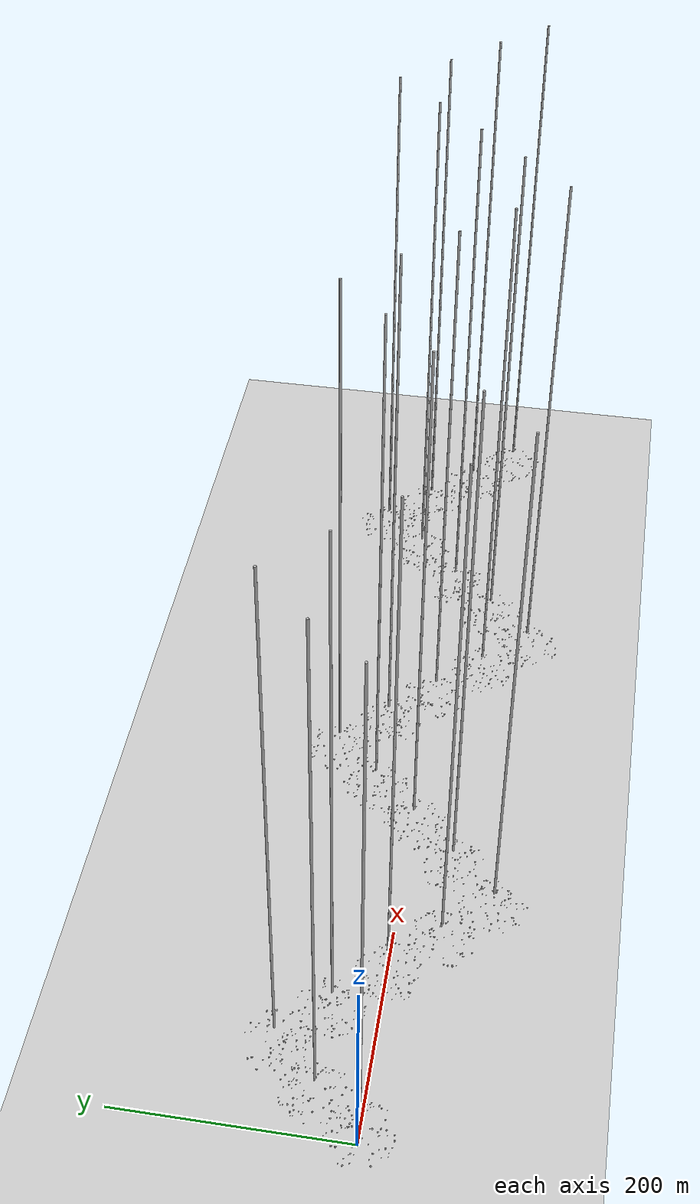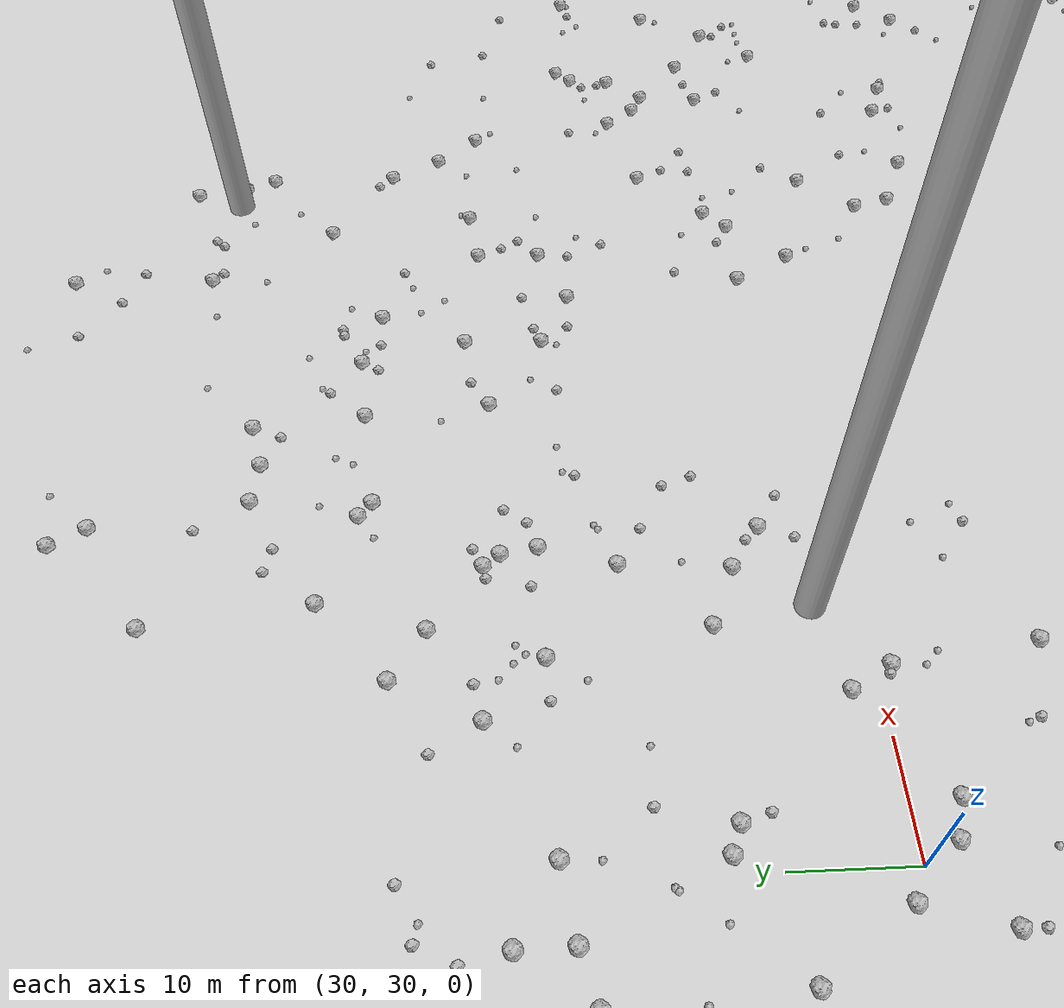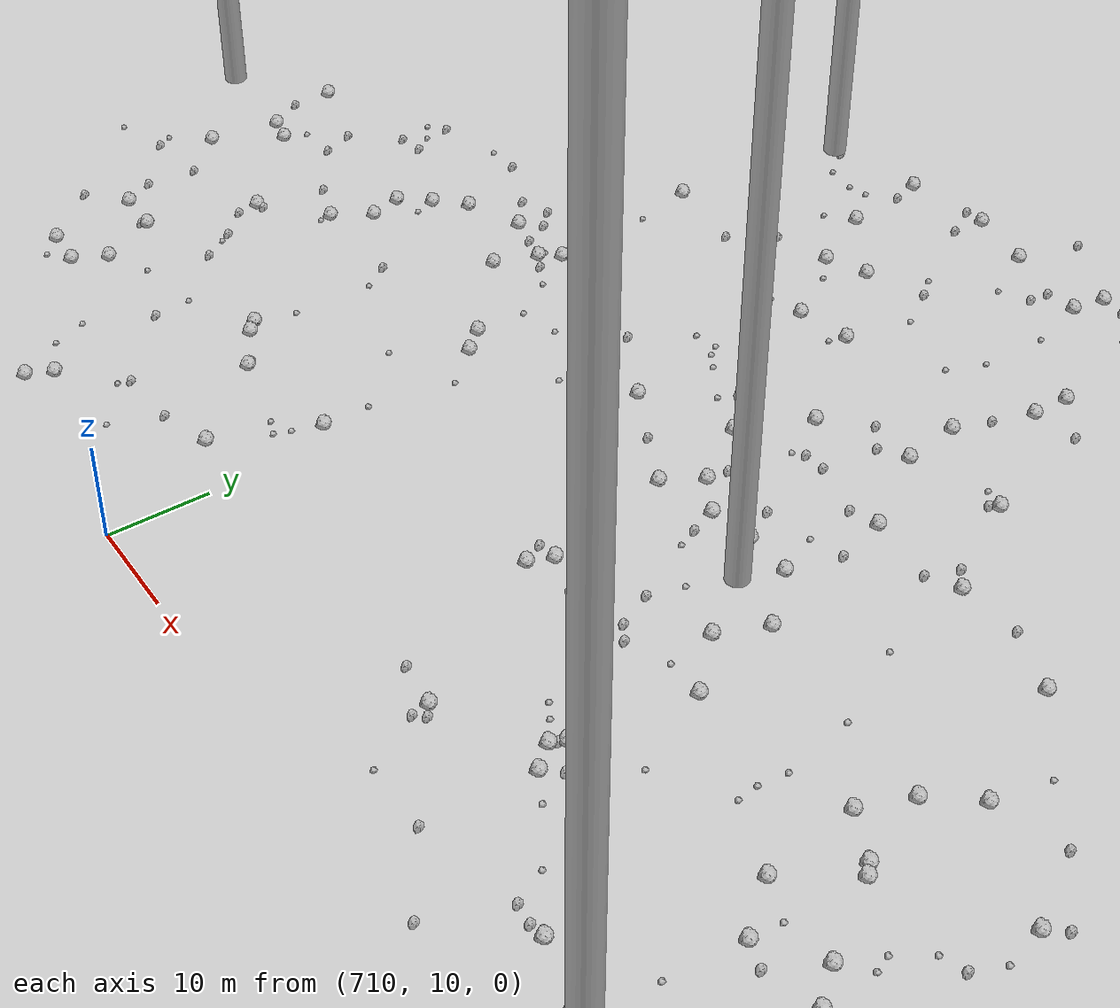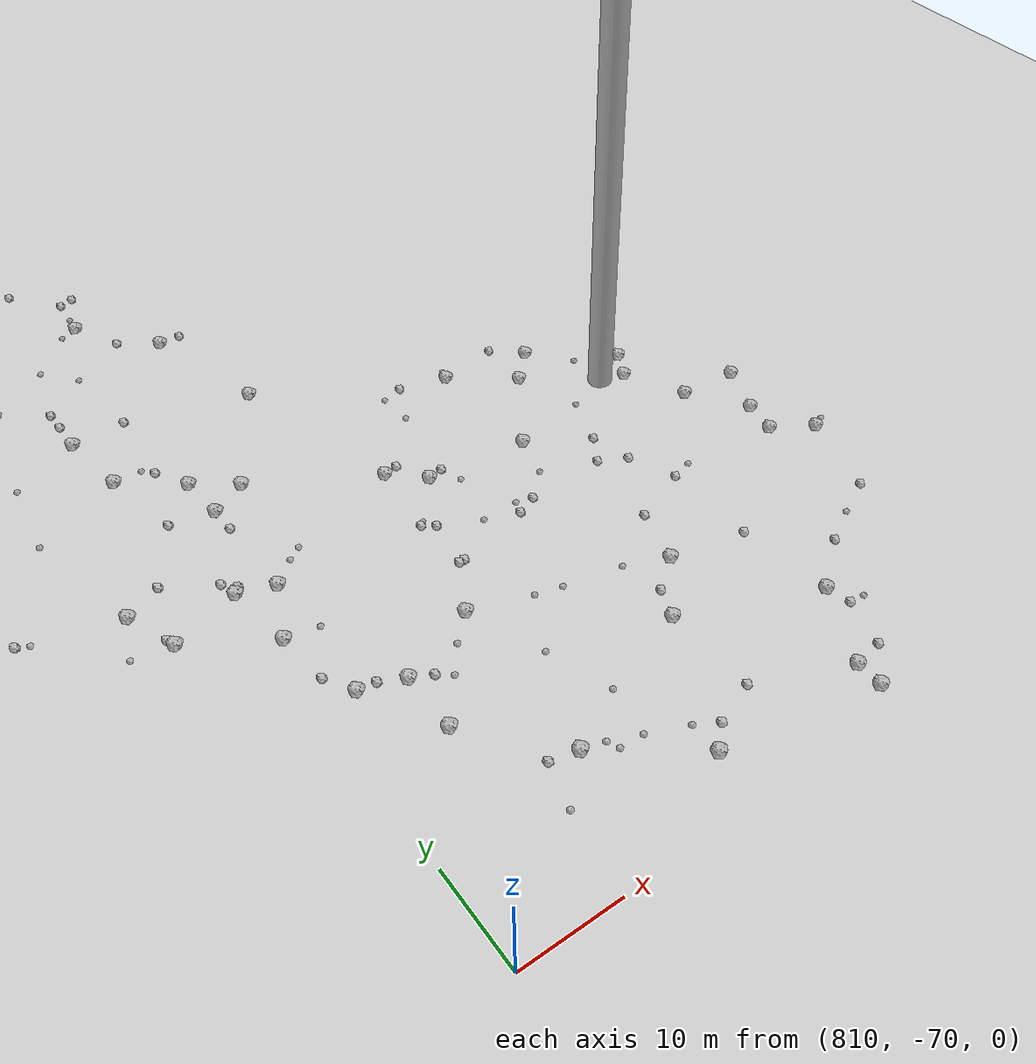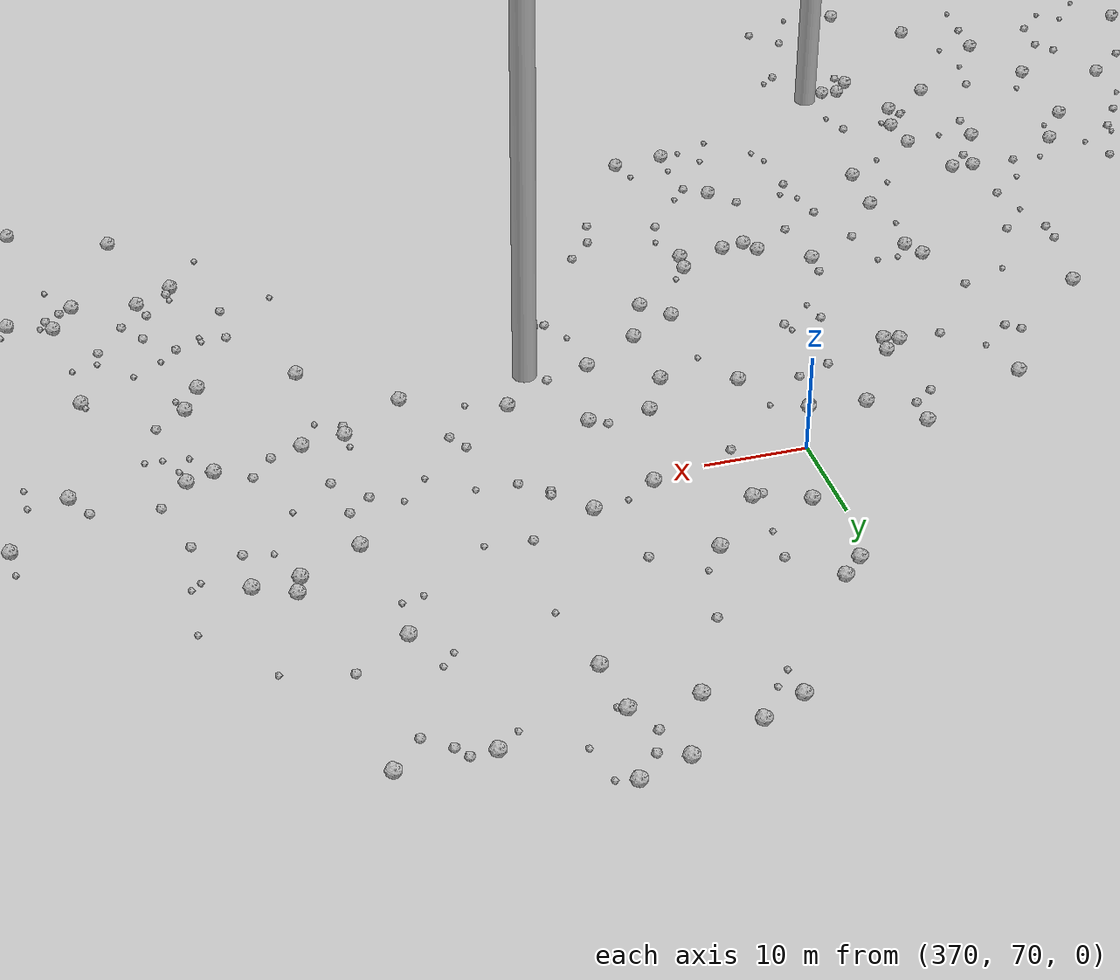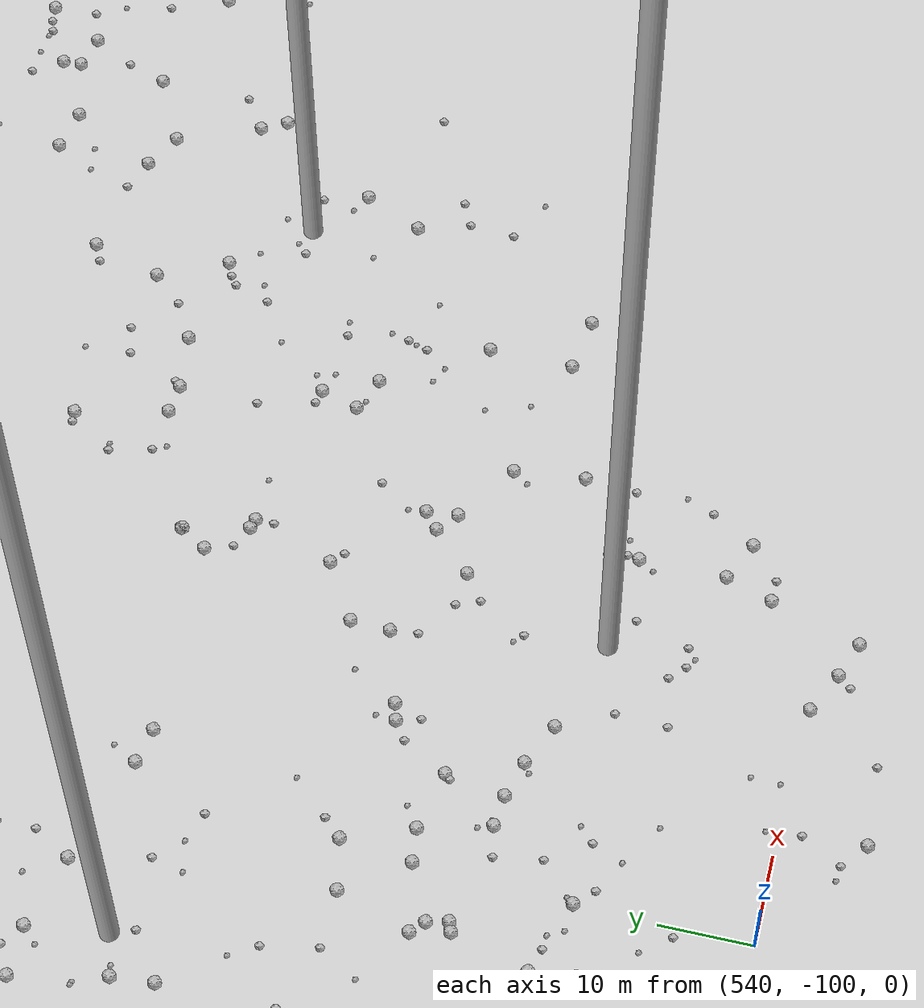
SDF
<sdf version="1.6">
 <world name="default">
  <include><uri>model://custom_ground</uri></include>
  <include><uri>model://sun</uri></include>
  <spherical_coordinates>
   <surface_model>EARTH_WGS84</surface_model>
   <latitude_deg>38.161479</latitude_deg>
   <longitude_deg>-122.454630</longitude_deg>
   <elevation>488.0</elevation>
   <heading_deg>90</heading_deg>
  </spherical_coordinates>
  <model name="rock1_0_0">
   <include><uri>model://rock1</uri><pose>24.398046547388958 8.331102305955568 0.5 0 0 0</pose></include>
  </model>
  <model name="rock1_0_1">
   <include><uri>model://rock1</uri><pose>34.09810841004603 -13.936259148995287 0.5 0 0 0</pose></include>
  </model>
  <model name="rock1_0_2">
   <include><uri>model://rock1</uri><pose>15.198357829529435 6.747500550757017 0.5 0 0 0</pose></include>
  </model>
  <model name="rock1_0_3">
   <include><uri>model://rock1</uri><pose>-15.56095035758571 -12.66501505706362 0.5 0 0 0</pose></include>
  </model>
  <model name="rock1_0_4">
   <include><uri>model://rock1</uri><pose>25.425156211855622 24.583975993850906 0.5 0 0 0</pose></include>
  </model>
  <model name="rock1_0_5">
   <include><uri>model://rock1</uri><pose>36.107950517978445 -11.725876800390687 0.5 0 0 0</pose></include>
  </model>
  <model name="rock1_0_6">
   <include><uri>model://rock1</uri><pose>8.274360229697567 -27.73855662255845 0.5 0 0 0</pose></include>
  </model>
  <model name="rock1_0_7">
   <include><uri>model://rock1</uri><pose>-4.032806701916421 16.494015629699007 0.5 0 0 0</pose></include>
  </model>
  <model name="rock1_0_8">
   <include><uri>model://rock1</uri><pose>13.274452738488172 -27.146397997913994 0.5 0 0 0</pose></include>
  </model>
  <model name="rock1_0_9">
   <include><uri>model://rock1</uri><pose>35.446819270651226 -1.0865948712470548 0.5 0 0 0</pose></include>
  </model>
  <model name="rock1_0_10">
   <include><uri>model://rock1</uri><pose>26.778924924858977 5.0052008827340515 0.5 0 0 0</pose></include>
  </model>
  <model name="rock1_0_11">
   <include><uri>model://rock1</uri><pose>24.802799261099857 -18.29904144895759 0.5 0 0 0</pose></include>
  </model>
  <model name="rock1_0_12">
   <include><uri>model://rock1</uri><pose>-18.514312107212657 8.81685401557688 0.5 0 0 0</pose></include>
  </model>
  <model name="rock1_0_13">
   <include><uri>model://rock1</uri><pose>8.750869696426566 21.498424355484694 0.5 0 0 0</pose></include>
  </model>
  <model name="rock1_0_14">
   <include><uri>model://rock1</uri><pose>20.867704677126206 13.332006006602477 0.5 0 0 0</pose></include>
  </model>
  <model name="rock1_0_15">
   <include><uri>model://rock1</uri><pose>5.114196946024528 2.52552981307619 0.5 0 0 0</pose></include>
  </model>
  <model name="rock1_0_16">
   <include><uri>model://rock1</uri><pose>15.684478192428422 -9.19805900003714 0.5 0 0 0</pose></include>
  </model>
  <model name="rock1_0_17">
   <include><uri>model://rock1</uri><pose>28.410638610979298 10.97447269910247 0.5 0 0 0</pose></include>
  </model>
  <model name="rock1_0_18">
   <include><uri>model://rock1</uri><pose>-3.945079876574912 20.117027902949445 0.5 0 0 0</pose></include>
  </model>
  <model name="rock1_0_19">
   <include><uri>model://rock1</uri><pose>16.776309272322564 -15.839045252920945 0.5 0 0 0</pose></include>
  </model>
  <model name="rock1_0_20">
   <include><uri>model://rock1</uri><pose>-1.7516750062323752 3.7523604697794752 0.5 0 0 0</pose></include>
  </model>
  <model name="rock1_0_21">
   <include><uri>model://rock1</uri><pose>13.721501846775531 -13.741701766387784 0.5 0 0 0</pose></include>
  </model>
  <model name="rock1_0_22">
   <include><uri>model://rock1</uri><pose>-7.761213293122127 4.4262627833510635 0.5 0 0 0</pose></include>
  </model>
  <model name="rock1_0_23">
   <include><uri>model://rock1</uri><pose>17.278436342714038 8.74608618900924 0.5 0 0 0</pose></include>
  </model>
  <model name="rock1_0_24">
   <include><uri>model://rock1</uri><pose>14.395165227214406 8.926736808135793 0.5 0 0 0</pose></include>
  </model>
  <model name="rock1_0_25">
   <include><uri>model://rock1</uri><pose>16.19458807552317 -20.22665982738291 0.5 0 0 0</pose></include>
  </model>
  <model name="rock1_0_26">
   <include><uri>model://rock1</uri><pose>0.7971871965159281 -21.665091179481884 0.5 0 0 0</pose></include>
  </model>
  <model name="rock2_0_0">
   <include><uri>model://rock2</uri><pose>11.178878192248352 -15.37912908046642 0.3 0 0 0</pose></include>
  </model>
  <model name="rock2_0_1">
   <include><uri>model://rock2</uri><pose>30.639830556980904 -3.046735685341364 0.3 0 0 0</pose></include>
  </model>
  <model name="rock2_0_2">
   <include><uri>model://rock2</uri><pose>10.136467191785655 -14.522756830903994 0.3 0 0 0</pose></include>
  </model>
  <model name="rock2_0_3">
   <include><uri>model://rock2</uri><pose>8.249185496821397 17.254659473181462 0.3 0 0 0</pose></include>
  </model>
  <model name="rock2_0_4">
   <include><uri>model://rock2</uri><pose>-4.778702521419662 -12.331769416668092 0.3 0 0 0</pose></include>
  </model>
  <model name="rock2_0_5">
   <include><uri>model://rock2</uri><pose>-10.193508002677605 -10.752084497466718 0.3 0 0 0</pose></include>
  </model>
  <model name="rock2_0_6">
   <include><uri>model://rock2</uri><pose>15.367837340119216 -7.502160361509532 0.3 0 0 0</pose></include>
  </model>
  <model name="rock2_0_7">
   <include><uri>model://rock2</uri><pose>14.63651596450704 15.238386888199301 0.3 0 0 0</pose></include>
  </model>
  <model name="rock2_0_8">
   <include><uri>model://rock2</uri><pose>24.77738985595908 17.105526170896844 0.3 0 0 0</pose></include>
  </model>
  <model name="rock2_0_9">
   <include><uri>model://rock2</uri><pose>-12.578634283599095 8.82040023669554 0.3 0 0 0</pose></include>
  </model>
  <model name="rock2_0_10">
   <include><uri>model://rock2</uri><pose>13.486382331689114 9.902483884202816 0.3 0 0 0</pose></include>
  </model>
  <model name="rock2_0_11">
   <include><uri>model://rock2</uri><pose>-17.236688325267856 12.374861736572115 0.3 0 0 0</pose></include>
  </model>
  <model name="rock2_0_12">
   <include><uri>model://rock2</uri><pose>38.69159056301164 5.499459039122698 0.3 0 0 0</pose></include>
  </model>
  <model name="rock2_0_13">
   <include><uri>model://rock2</uri><pose>8.37568412748929 20.959492686635613 0.3 0 0 0</pose></include>
  </model>
  <model name="rock2_0_14">
   <include><uri>model://rock2</uri><pose>-15.803137053449593 3.6973928092877486 0.3 0 0 0</pose></include>
  </model>
  <model name="rock2_0_15">
   <include><uri>model://rock2</uri><pose>2.234203257838331 -8.154769849935693 0.3 0 0 0</pose></include>
  </model>
  <model name="rock2_0_16">
   <include><uri>model://rock2</uri><pose>2.242073311798947 -26.747611867422233 0.3 0 0 0</pose></include>
  </model>
  <model name="rock2_0_17">
   <include><uri>model://rock2</uri><pose>38.06090431995921 -5.347931985063955 0.3 0 0 0</pose></include>
  </model>
  <model name="rock2_0_18">
   <include><uri>model://rock2</uri><pose>34.8891109810859 -7.290418207069479 0.3 0 0 0</pose></include>
  </model>
  <model name="rock2_0_19">
   <include><uri>model://rock2</uri><pose>-5.225156711143411 -13.013579734960018 0.3 0 0 0</pose></include>
  </model>
  <model name="rock2_0_20">
   <include><uri>model://rock2</uri><pose>6.445825033314872 25.417224663213304 0.3 0 0 0</pose></include>
  </model>
  <model name="rock2_0_21">
   <include><uri>model://rock2</uri><pose>21.257120593473708 7.150197509861648 0.3 0 0 0</pose></include>
  </model>
  <model name="rock2_0_22">
   <include><uri>model://rock2</uri><pose>6.629539646432679 -2.512016218472308 0.3 0 0 0</pose></include>
  </model>
  <model name="rock2_0_23">
   <include><uri>model://rock2</uri><pose>36.25482624327795 -4.244649269553452 0.3 0 0 0</pose></include>
  </model>
  <model name="rock2_0_24">
   <include><uri>model://rock2</uri><pose>35.391362866451544 7.016223779015192 0.3 0 0 0</pose></include>
  </model>
  <model name="rock2_0_25">
   <include><uri>model://rock2</uri><pose>12.981730907124579 14.620663578524656 0.3 0 0 0</pose></include>
  </model>
  <model name="rock2_0_26">
   <include><uri>model://rock2</uri><pose>-0.9776848692292788 -16.845700547140527 0.3 0 0 0</pose></include>
  </model>
  <model name="rock3_0_0">
   <include><uri>model://rock3</uri><pose>-8.687392889862277 5.575190473100015 0.2 0 0 0</pose></include>
  </model>
  <model name="rock3_0_1">
   <include><uri>model://rock3</uri><pose>-5.764836693764581 -24.585683461284038 0.2 0 0 0</pose></include>
  </model>
  <model name="rock3_0_2">
   <include><uri>model://rock3</uri><pose>8.321432072955155 17.35052053355117 0.2 0 0 0</pose></include>
  </model>
  <model name="rock3_0_3">
   <include><uri>model://rock3</uri><pose>10.301109729334666 2.0117848441598056 0.2 0 0 0</pose></include>
  </model>
  <model name="rock3_0_4">
   <include><uri>model://rock3</uri><pose>26.021095695911512 17.015493745069385 0.2 0 0 0</pose></include>
  </model>
  <model name="rock3_0_5">
   <include><uri>model://rock3</uri><pose>14.594085232333896 10.567451240670628 0.2 0 0 0</pose></include>
  </model>
  <model name="rock3_0_6">
   <include><uri>model://rock3</uri><pose>33.52405089080246 -18.13960654322137 0.2 0 0 0</pose></include>
  </model>
  <model name="rock3_0_7">
   <include><uri>model://rock3</uri><pose>34.44431216280264 14.215763248225528 0.2 0 0 0</pose></include>
  </model>
  <model name="rock3_0_8">
   <include><uri>model://rock3</uri><pose>1.3514156436997702 4.147095424777973 0.2 0 0 0</pose></include>
  </model>
  <model name="rock3_0_9">
   <include><uri>model://rock3</uri><pose>-2.662904272789987 14.031891588713734 0.2 0 0 0</pose></include>
  </model>
  <model name="rock3_0_10">
   <include><uri>model://rock3</uri><pose>14.443927133557274 26.491308725689976 0.2 0 0 0</pose></include>
  </model>
  <model name="rock3_0_11">
   <include><uri>model://rock3</uri><pose>31.015106995483542 20.04386574921861 0.2 0 0 0</pose></include>
  </model>
  <model name="rock3_0_12">
   <include><uri>model://rock3</uri><pose>24.472361247335392 21.20226026062911 0.2 0 0 0</pose></include>
  </model>
  <model name="rock3_0_13">
   <include><uri>model://rock3</uri><pose>-8.37429775585642 1.7722942387057046 0.2 0 0 0</pose></include>
  </model>
  <model name="rock3_0_14">
   <include><uri>model://rock3</uri><pose>12.09625758608663 -21.408670439248905 0.2 0 0 0</pose></include>
  </model>
  <model name="rock3_0_15">
   <include><uri>model://rock3</uri><pose>24.67754850765546 -1.5536613858015826 0.2 0 0 0</pose></include>
  </model>
  <model name="rock3_0_16">
   <include><uri>model://rock3</uri><pose>-14.683272969891576 -14.551118838191597 0.2 0 0 0</pose></include>
  </model>
  <model name="rock3_0_17">
   <include><uri>model://rock3</uri><pose>34.696443064877066 16.102718842020245 0.2 0 0 0</pose></include>
  </model>
  <model name="rock3_0_18">
   <include><uri>model://rock3</uri><pose>3.5806994332801594 27.201398213118296 0.2 0 0 0</pose></include>
  </model>
  <model name="rock3_0_19">
   <include><uri>model://rock3</uri><pose>36.54110997576854 4.914971407695319 0.2 0 0 0</pose></include>
  </model>
  <model name="rock3_0_20">
   <include><uri>model://rock3</uri><pose>-6.942153635509694 -19.82945800390865 0.2 0 0 0</pose></include>
  </model>
  <model name="rock3_0_21">
   <include><uri>model://rock3</uri><pose>-1.2283325989861602 3.8152570687351783 0.2 0 0 0</pose></include>
  </model>
  <model name="rock3_0_22">
   <include><uri>model://rock3</uri><pose>34.091367228809084 -5.107620949934606 0.2 0 0 0</pose></include>
  </model>
  <model name="rock3_0_23">
   <include><uri>model://rock3</uri><pose>4.455656557604833 17.048983818287063 0.2 0 0 0</pose></include>
  </model>
  <model name="rock3_0_24">
   <include><uri>model://rock3</uri><pose>13.03609420961201 11.616181673068944 0.2 0 0 0</pose></include>
  </model>
  <model name="rock3_0_25">
   <include><uri>model://rock3</uri><pose>37.07717420326672 6.446223465961403 0.2 0 0 0</pose></include>
  </model>
  <model name="rock3_0_26">
   <include><uri>model://rock3</uri><pose>-2.570188992939265 -24.66033882622036 0.2 0 0 0</pose></include>
  </model>
  <model name="rock1_1_0">
   <include><uri>model://rock1</uri><pose>19.425003117817205 56.50632508070087 0.5 0 0 0</pose></include>
  </model>
  <model name="rock1_1_1">
   <include><uri>model://rock1</uri><pose>25.558442848940917 59.50486546614128 0.5 0 0 0</pose></include>
  </model>
  <model name="rock1_1_2">
   <include><uri>model://rock1</uri><pose>55.66664009464132 40.35930092184341 0.5 0 0 0</pose></include>
  </model>
  <model name="rock1_1_3">
   <include><uri>model://rock1</uri><pose>21.423726119714697 53.823191622133 0.5 0 0 0</pose></include>
  </model>
  <model name="rock1_1_4">
   <include><uri>model://rock1</uri><pose>31.369608338626623 43.67353572772181 0.5 0 0 0</pose></include>
  </model>
  <model name="rock1_1_5">
   <include><uri>model://rock1</uri><pose>31.600779885821634 56.05886251243707 0.5 0 0 0</pose></include>
  </model>
  <model name="rock1_1_6">
   <include><uri>model://rock1</uri><pose>34.93638321271557 26.168525069026018 0.5 0 0 0</pose></include>
  </model>
  <model name="rock1_1_7">
   <include><uri>model://rock1</uri><pose>50.76532550656072 65.89541421264988 0.5 0 0 0</pose></include>
  </model>
  <model name="rock1_1_8">
   <include><uri>model://rock1</uri><pose>47.71309964108496 16.543162670885927 0.5 0 0 0</pose></include>
  </model>
  <model name="rock1_1_9">
   <include><uri>model://rock1</uri><pose>46.17678258295535 11.849964635521737 0.5 0 0 0</pose></include>
  </model>
  <model name="rock1_1_10">
   <include><uri>model://rock1</uri><pose>42.56170784381477 61.40262359552571 0.5 0 0 0</pose></include>
  </model>
  <model name="rock1_1_11">
   <include><uri>model://rock1</uri><pose>33.67454344942851 42.75834167881747 0.5 0 0 0</pose></include>
  </model>
  <model name="rock1_1_12">
   <include><uri>model://rock1</uri><pose>46.29132741507373 68.88989371094698 0.5 0 0 0</pose></include>
  </model>
  <model name="rock1_1_13">
   <include><uri>model://rock1</uri><pose>50.133189552857445 42.6571145455821 0.5 0 0 0</pose></include>
  </model>
  <model name="rock1_1_14">
   <include><uri>model://rock1</uri><pose>43.91813613542297 32.58001957642411 0.5 0 0 0</pose></include>
  </model>
  <model name="rock1_1_15">
   <include><uri>model://rock1</uri><pose>22.21106952087425 39.06832311325705 0.5 0 0 0</pose></include>
  </model>
  <model name="rock1_1_16">
   <include><uri>model://rock1</uri><pose>18.965502861670394 24.526492891724196 0.5 0 0 0</pose></include>
  </model>
  <model name="rock1_1_17">
   <include><uri>model://rock1</uri><pose>27.434630315228823 31.32441443752021 0.5 0 0 0</pose></include>
  </model>
  <model name="rock1_1_18">
   <include><uri>model://rock1</uri><pose>58.39810176458199 56.602359833909674 0.5 0 0 0</pose></include>
  </model>
  <model name="rock1_1_19">
   <include><uri>model://rock1</uri><pose>31.829149913006887 12.535967022490105 0.5 0 0 0</pose></include>
  </model>
  <model name="rock1_1_20">
   <include><uri>model://rock1</uri><pose>25.6316663179715 55.04178573944432 0.5 0 0 0</pose></include>
  </model>
  <model name="rock1_1_21">
   <include><uri>model://rock1</uri><pose>31.74868102302084 27.180345825179213 0.5 0 0 0</pose></include>
  </model>
  <model name="rock1_1_22">
   <include><uri>model://rock1</uri><pose>46.02236478573441 29.000139780088343 0.5 0 0 0</pose></include>
  </model>
  <model name="rock1_1_23">
   <include><uri>model://rock1</uri><pose>59.6882771959277 37.58397863034142 0.5 0 0 0</pose></include>
  </model>
  <model name="rock1_1_24">
   <include><uri>model://rock1</uri><pose>56.3644210779951 49.968463809770554 0.5 0 0 0</pose></include>
  </model>
  <model name="rock1_1_25">
   <include><uri>model://rock1</uri><pose>61.30750090529187 29.256105609796734 0.5 0 0 0</pose></include>
  </model>
  <model name="rock1_1_26">
   <include><uri>model://rock1</uri><pose>47.795557626381594 56.34738750413363 0.5 0 0 0</pose></include>
  </model>
  <model name="rock2_1_0">
   <include><uri>model://rock2</uri><pose>65.95129690960178 53.01952291828719 0.3 0 0 0</pose></include>
  </model>
  <model name="rock2_1_1">
   <include><uri>model://rock2</uri><pose>65.39146540457831 42.69674117953389 0.3 0 0 0</pose></include>
  </model>
  <model name="rock2_1_2">
   <include><uri>model://rock2</uri><pose>30.35757164379313 67.72364123221388 0.3 0 0 0</pose></include>
  </model>
  <model name="rock2_1_3">
   <include><uri>model://rock2</uri><pose>24.71617940287822 63.279115536598994 0.3 0 0 0</pose></include>
  </model>
  <model name="rock2_1_4">
   <include><uri>model://rock2</uri><pose>59.94337392289338 47.71422293352214 0.3 0 0 0</pose></include>
  </model>
  <model name="rock2_1_5">
   <include><uri>model://rock2</uri><pose>26.210327171580307 66.37885120267966 0.3 0 0 0</pose></include>
  </model>
  <model name="rock2_1_6">
   <include><uri>model://rock2</uri><pose>11.641559948702637 44.10045429791089 0.3 0 0 0</pose></include>
  </model>
  <model name="rock2_1_7">
   <include><uri>model://rock2</uri><pose>55.450544218491935 61.054813284322655 0.3 0 0 0</pose></include>
  </model>
  <model name="rock2_1_8">
   <include><uri>model://rock2</uri><pose>40.0153825352719 65.569949336368 0.3 0 0 0</pose></include>
  </model>
  <model name="rock2_1_9">
   <include><uri>model://rock2</uri><pose>21.03933772054574 17.222446023736147 0.3 0 0 0</pose></include>
  </model>
  <model name="rock2_1_10">
   <include><uri>model://rock2</uri><pose>41.01407272661666 18.368551106386946 0.3 0 0 0</pose></include>
  </model>
  <model name="rock2_1_11">
   <include><uri>model://rock2</uri><pose>62.930190736265416 35.528780495259426 0.3 0 0 0</pose></include>
  </model>
  <model name="rock2_1_12">
   <include><uri>model://rock2</uri><pose>35.16489261036551 48.92981404772779 0.3 0 0 0</pose></include>
  </model>
  <model name="rock2_1_13">
   <include><uri>model://rock2</uri><pose>54.51653789976333 57.26637489924642 0.3 0 0 0</pose></include>
  </model>
  <model name="rock2_1_14">
   <include><uri>model://rock2</uri><pose>16.672860416420875 53.768743557961145 0.3 0 0 0</pose></include>
  </model>
  <model name="rock2_1_15">
   <include><uri>model://rock2</uri><pose>20.937183169625023 49.66081745642863 0.3 0 0 0</pose></include>
  </model>
  <model name="rock2_1_16">
   <include><uri>model://rock2</uri><pose>34.39684042581755 40.343931316664225 0.3 0 0 0</pose></include>
  </model>
  <model name="rock2_1_17">
   <include><uri>model://rock2</uri><pose>45.189947086016744 29.191928208241887 0.3 0 0 0</pose></include>
  </model>
  <model name="rock2_1_18">
   <include><uri>model://rock2</uri><pose>58.471163636983185 34.52359986547269 0.3 0 0 0</pose></include>
  </model>
  <model name="rock2_1_19">
   <include><uri>model://rock2</uri><pose>58.36730213477648 38.787303433778796 0.3 0 0 0</pose></include>
  </model>
  <model name="rock2_1_20">
   <include><uri>model://rock2</uri><pose>43.979689908041244 56.112986172857056 0.3 0 0 0</pose></include>
  </model>
  <model name="rock2_1_21">
   <include><uri>model://rock2</uri><pose>25.406130638286974 22.64893599245571 0.3 0 0 0</pose></include>
  </model>
  <model name="rock2_1_22">
   <include><uri>model://rock2</uri><pose>64.44071902756129 45.390736515694016 0.3 0 0 0</pose></include>
  </model>
  <model name="rock2_1_23">
   <include><uri>model://rock2</uri><pose>20.6027645237826 19.434415848834362 0.3 0 0 0</pose></include>
  </model>
  <model name="rock2_1_24">
   <include><uri>model://rock2</uri><pose>45.71405025550042 62.12235194790082 0.3 0 0 0</pose></include>
  </model>
  <model name="rock2_1_25">
   <include><uri>model://rock2</uri><pose>59.461454279952434 19.6914944553616 0.3 0 0 0</pose></include>
  </model>
  <model name="rock2_1_26">
   <include><uri>model://rock2</uri><pose>19.028343868377217 47.33396543315797 0.3 0 0 0</pose></include>
  </model>
  <model name="rock3_1_0">
   <include><uri>model://rock3</uri><pose>39.95485322645621 48.68760184803428 0.2 0 0 0</pose></include>
  </model>
  <model name="rock3_1_1">
   <include><uri>model://rock3</uri><pose>21.402466316390367 46.60715027827901 0.2 0 0 0</pose></include>
  </model>
  <model name="rock3_1_2">
   <include><uri>model://rock3</uri><pose>48.187244261913946 57.912673502715286 0.2 0 0 0</pose></include>
  </model>
  <model name="rock3_1_3">
   <include><uri>model://rock3</uri><pose>45.67707302505817 53.08394740051995 0.2 0 0 0</pose></include>
  </model>
  <model name="rock3_1_4">
   <include><uri>model://rock3</uri><pose>40.62375972757268 19.335022092615453 0.2 0 0 0</pose></include>
  </model>
  <model name="rock3_1_5">
   <include><uri>model://rock3</uri><pose>27.58602307973851 66.0100153825302 0.2 0 0 0</pose></include>
  </model>
  <model name="rock3_1_6">
   <include><uri>model://rock3</uri><pose>14.438213375800487 31.00791280485955 0.2 0 0 0</pose></include>
  </model>
  <model name="rock3_1_7">
   <include><uri>model://rock3</uri><pose>23.902878291803486 65.07210247895102 0.2 0 0 0</pose></include>
  </model>
  <model name="rock3_1_8">
   <include><uri>model://rock3</uri><pose>29.26677063637864 47.95910754136872 0.2 0 0 0</pose></include>
  </model>
  <model name="rock3_1_9">
   <include><uri>model://rock3</uri><pose>58.38768116924768 31.830852470955598 0.2 0 0 0</pose></include>
  </model>
  <model name="rock3_1_10">
   <include><uri>model://rock3</uri><pose>46.02387559253339 60.12037249103301 0.2 0 0 0</pose></include>
  </model>
  <model name="rock3_1_11">
   <include><uri>model://rock3</uri><pose>55.89568100416487 22.249722221024967 0.2 0 0 0</pose></include>
  </model>
  <model name="rock3_1_12">
   <include><uri>model://rock3</uri><pose>56.40717709903375 44.44879456406806 0.2 0 0 0</pose></include>
  </model>
  <model name="rock3_1_13">
   <include><uri>model://rock3</uri><pose>49.06218228131813 58.7139358914554 0.2 0 0 0</pose></include>
  </model>
  <model name="rock3_1_14">
   <include><uri>model://rock3</uri><pose>47.408426201116804 58.89747765385298 0.2 0 0 0</pose></include>
  </model>
  <model name="rock3_1_15">
   <include><uri>model://rock3</uri><pose>16.432532407229786 55.36953557171506 0.2 0 0 0</pose></include>
  </model>
  <model name="rock3_1_16">
   <include><uri>model://rock3</uri><pose>29.877247598322715 13.615798996419121 0.2 0 0 0</pose></include>
  </model>
  <model name="rock3_1_17">
   <include><uri>model://rock3</uri><pose>60.53441171630188 51.62966572169031 0.2 0 0 0</pose></include>
  </model>
  <model name="rock3_1_18">
   <include><uri>model://rock3</uri><pose>26.61584894545513 44.463990504075205 0.2 0 0 0</pose></include>
  </model>
  <model name="rock3_1_19">
   <include><uri>model://rock3</uri><pose>60.07486664340448 51.30618578684622 0.2 0 0 0</pose></include>
  </model>
  <model name="rock3_1_20">
   <include><uri>model://rock3</uri><pose>40.31048330726588 58.791810943603956 0.2 0 0 0</pose></include>
  </model>
  <model name="rock3_1_21">
   <include><uri>model://rock3</uri><pose>29.03358334369004 47.7140817136903 0.2 0 0 0</pose></include>
  </model>
  <model name="rock3_1_22">
   <include><uri>model://rock3</uri><pose>31.418503087974518 52.92825671424271 0.2 0 0 0</pose></include>
  </model>
  <model name="rock3_1_23">
   <include><uri>model://rock3</uri><pose>47.07372861520396 24.88700846905413 0.2 0 0 0</pose></include>
  </model>
  <model name="rock3_1_24">
   <include><uri>model://rock3</uri><pose>45.876425550048445 26.053655566199136 0.2 0 0 0</pose></include>
  </model>
  <model name="rock3_1_25">
   <include><uri>model://rock3</uri><pose>61.41487575459471 20.30981806883367 0.2 0 0 0</pose></include>
  </model>
  <model name="rock3_1_26">
   <include><uri>model://rock3</uri><pose>59.61619074239593 24.16344037788747 0.2 0 0 0</pose></include>
  </model>
  <model name="rock1_2_0">
   <include><uri>model://rock1</uri><pose>72.77288217719962 82.28535585567684 0.5 0 0 0</pose></include>
  </model>
  <model name="rock1_2_1">
   <include><uri>model://rock1</uri><pose>60.41346150642046 98.39307718537819 0.5 0 0 0</pose></include>
  </model>
  <model name="rock1_2_2">
   <include><uri>model://rock1</uri><pose>106.17099506656479 91.70446135920014 0.5 0 0 0</pose></include>
  </model>
  <model name="rock1_2_3">
   <include><uri>model://rock1</uri><pose>57.84102253294301 59.82999419857297 0.5 0 0 0</pose></include>
  </model>
  <model name="rock1_2_4">
   <include><uri>model://rock1</uri><pose>64.31949570995003 81.65797855742218 0.5 0 0 0</pose></include>
  </model>
  <model name="rock1_2_5">
   <include><uri>model://rock1</uri><pose>62.32896416411121 72.07060110870512 0.5 0 0 0</pose></include>
  </model>
  <model name="rock1_2_6">
   <include><uri>model://rock1</uri><pose>80.53424105118992 72.69019906101913 0.5 0 0 0</pose></include>
  </model>
  <model name="rock1_2_7">
   <include><uri>model://rock1</uri><pose>108.2414478283924 83.68708566324423 0.5 0 0 0</pose></include>
  </model>
  <model name="rock1_2_8">
   <include><uri>model://rock1</uri><pose>51.910580282129466 89.39216511524117 0.5 0 0 0</pose></include>
  </model>
  <model name="rock1_2_9">
   <include><uri>model://rock1</uri><pose>95.2019912476832 61.44227990262468 0.5 0 0 0</pose></include>
  </model>
  <model name="rock1_2_10">
   <include><uri>model://rock1</uri><pose>56.70402321782013 61.27401580865593 0.5 0 0 0</pose></include>
  </model>
  <model name="rock1_2_11">
   <include><uri>model://rock1</uri><pose>99.3667635873953 76.74753025245374 0.5 0 0 0</pose></include>
  </model>
  <model name="rock1_2_12">
   <include><uri>model://rock1</uri><pose>82.66384479267012 55.35543284536576 0.5 0 0 0</pose></include>
  </model>
  <model name="rock1_2_13">
   <include><uri>model://rock1</uri><pose>82.84054077600283 62.81710955595467 0.5 0 0 0</pose></include>
  </model>
  <model name="rock1_2_14">
   <include><uri>model://rock1</uri><pose>73.7653137562589 72.0559850601592 0.5 0 0 0</pose></include>
  </model>
  <model name="rock1_2_15">
   <include><uri>model://rock1</uri><pose>53.61934257513018 75.11312426616888 0.5 0 0 0</pose></include>
  </model>
  <model name="rock1_2_16">
   <include><uri>model://rock1</uri><pose>63.7588983344762 70.9223545333098 0.5 0 0 0</pose></include>
  </model>
  <model name="rock1_2_17">
   <include><uri>model://rock1</uri><pose>88.68781690258824 52.53447104005454 0.5 0 0 0</pose></include>
  </model>
  <model name="rock1_2_18">
   <include><uri>model://rock1</uri><pose>68.37398770739568 81.15338599948592 0.5 0 0 0</pose></include>
  </model>
  <model name="rock1_2_19">
   <include><uri>model://rock1</uri><pose>92.64718069735434 88.54838499765187 0.5 0 0 0</pose></include>
  </model>
  <model name="rock1_2_20">
   <include><uri>model://rock1</uri><pose>62.109050755055115 95.32773111082963 0.5 0 0 0</pose></include>
  </model>
  <model name="rock1_2_21">
   <include><uri>model://rock1</uri><pose>95.02840457930094 55.24516916239159 0.5 0 0 0</pose></include>
  </model>
  <model name="rock1_2_22">
   <include><uri>model://rock1</uri><pose>107.00056326068952 86.64400806404905 0.5 0 0 0</pose></include>
  </model>
  <model name="rock1_2_23">
   <include><uri>model://rock1</uri><pose>86.54846938847793 70.97149842704184 0.5 0 0 0</pose></include>
  </model>
  <model name="rock1_2_24">
   <include><uri>model://rock1</uri><pose>108.2886047527826 70.73356834586335 0.5 0 0 0</pose></include>
  </model>
  <model name="rock1_2_25">
   <include><uri>model://rock1</uri><pose>74.65372341638104 60.55269370542151 0.5 0 0 0</pose></include>
  </model>
  <model name="rock1_2_26">
   <include><uri>model://rock1</uri><pose>92.86697488443227 102.41593433264164 0.5 0 0 0</pose></include>
  </model>
  <model name="rock2_2_0">
   <include><uri>model://rock2</uri><pose>76.72341764591013 75.46166171064034 0.3 0 0 0</pose></include>
  </model>
  <model name="rock2_2_1">
   <include><uri>model://rock2</uri><pose>85.31613360542022 100.76905763942801 0.3 0 0 0</pose></include>
  </model>
  <model name="rock2_2_2">
   <include><uri>model://rock2</uri><pose>84.48937568881075 52.69229312699197 0.3 0 0 0</pose></include>
  </model>
  <model name="rock2_2_3">
   <include><uri>model://rock2</uri><pose>85.03333180477658 74.79483789670073 0.3 0 0 0</pose></include>
  </model>
  <model name="rock2_2_4">
   <include><uri>model://rock2</uri><pose>59.21973509978349 79.1855136670165 0.3 0 0 0</pose></include>
  </model>
  <model name="rock2_2_5">
   <include><uri>model://rock2</uri><pose>103.53484390703417 86.8440815978139 0.3 0 0 0</pose></include>
  </model>
  <model name="rock2_2_6">
   <include><uri>model://rock2</uri><pose>106.90811311131147 72.15904049314967 0.3 0 0 0</pose></include>
  </model>
  <model name="rock2_2_7">
   <include><uri>model://rock2</uri><pose>96.20598235041071 59.013931777679645 0.3 0 0 0</pose></include>
  </model>
  <model name="rock2_2_8">
   <include><uri>model://rock2</uri><pose>82.78033963237864 70.97708848608113 0.3 0 0 0</pose></include>
  </model>
  <model name="rock2_2_9">
   <include><uri>model://rock2</uri><pose>89.87439152721507 97.29606519291303 0.3 0 0 0</pose></include>
  </model>
  <model name="rock2_2_10">
   <include><uri>model://rock2</uri><pose>58.43627347581305 62.13173204213874 0.3 0 0 0</pose></include>
  </model>
  <model name="rock2_2_11">
   <include><uri>model://rock2</uri><pose>98.67359183151284 88.90190603583717 0.3 0 0 0</pose></include>
  </model>
  <model name="rock2_2_12">
   <include><uri>model://rock2</uri><pose>79.5059147028026 71.0903718042781 0.3 0 0 0</pose></include>
  </model>
  <model name="rock2_2_13">
   <include><uri>model://rock2</uri><pose>93.67772831402345 87.5873565294815 0.3 0 0 0</pose></include>
  </model>
  <model name="rock2_2_14">
   <include><uri>model://rock2</uri><pose>71.54740173513234 79.63748817673499 0.3 0 0 0</pose></include>
  </model>
  <model name="rock2_2_15">
   <include><uri>model://rock2</uri><pose>56.9297682270786 79.80222033645414 0.3 0 0 0</pose></include>
  </model>
  <model name="rock2_2_16">
   <include><uri>model://rock2</uri><pose>61.00220122517014 57.44019461055281 0.3 0 0 0</pose></include>
  </model>
  <model name="rock2_2_17">
   <include><uri>model://rock2</uri><pose>93.95825734966482 95.57949565318135 0.3 0 0 0</pose></include>
  </model>
  <model name="rock2_2_18">
   <include><uri>model://rock2</uri><pose>77.47615544431008 62.22405164285583 0.3 0 0 0</pose></include>
  </model>
  <model name="rock2_2_19">
   <include><uri>model://rock2</uri><pose>97.83338259255709 88.03300396161532 0.3 0 0 0</pose></include>
  </model>
  <model name="rock2_2_20">
   <include><uri>model://rock2</uri><pose>88.74474758439574 57.0520540575354 0.3 0 0 0</pose></include>
  </model>
  <model name="rock2_2_21">
   <include><uri>model://rock2</uri><pose>84.36703005940927 56.03231310337326 0.3 0 0 0</pose></include>
  </model>
  <model name="rock2_2_22">
   <include><uri>model://rock2</uri><pose>92.89785399810266 68.98815041513143 0.3 0 0 0</pose></include>
  </model>
  <model name="rock2_2_23">
   <include><uri>model://rock2</uri><pose>62.43218900248999 59.44596925163995 0.3 0 0 0</pose></include>
  </model>
  <model name="rock2_2_24">
   <include><uri>model://rock2</uri><pose>61.42469407504606 86.22342380435656 0.3 0 0 0</pose></include>
  </model>
  <model name="rock2_2_25">
   <include><uri>model://rock2</uri><pose>76.1868940881713 54.13528684673994 0.3 0 0 0</pose></include>
  </model>
  <model name="rock2_2_26">
   <include><uri>model://rock2</uri><pose>84.22406759580068 74.63403304535711 0.3 0 0 0</pose></include>
  </model>
  <model name="rock3_2_0">
   <include><uri>model://rock3</uri><pose>77.97156680884837 87.15635831862136 0.2 0 0 0</pose></include>
  </model>
  <model name="rock3_2_1">
   <include><uri>model://rock3</uri><pose>107.1485763359011 87.95006929209231 0.2 0 0 0</pose></include>
  </model>
  <model name="rock3_2_2">
   <include><uri>model://rock3</uri><pose>88.77333092341566 64.83752918511058 0.2 0 0 0</pose></include>
  </model>
  <model name="rock3_2_3">
   <include><uri>model://rock3</uri><pose>102.78794187443378 80.45987236830314 0.2 0 0 0</pose></include>
  </model>
  <model name="rock3_2_4">
   <include><uri>model://rock3</uri><pose>72.87763435600385 64.98302389212073 0.2 0 0 0</pose></include>
  </model>
  <model name="rock3_2_5">
   <include><uri>model://rock3</uri><pose>101.32044715332748 85.21886396636229 0.2 0 0 0</pose></include>
  </model>
  <model name="rock3_2_6">
   <include><uri>model://rock3</uri><pose>90.72444014185577 68.06095442074506 0.2 0 0 0</pose></include>
  </model>
  <model name="rock3_2_7">
   <include><uri>model://rock3</uri><pose>92.31361762474947 83.0254994408478 0.2 0 0 0</pose></include>
  </model>
  <model name="rock3_2_8">
   <include><uri>model://rock3</uri><pose>65.78215711934538 99.35160790874826 0.2 0 0 0</pose></include>
  </model>
  <model name="rock3_2_9">
   <include><uri>model://rock3</uri><pose>87.5497883218832 87.52219591462793 0.2 0 0 0</pose></include>
  </model>
  <model name="rock3_2_10">
   <include><uri>model://rock3</uri><pose>88.00657542476696 74.11637450047752 0.2 0 0 0</pose></include>
  </model>
  <model name="rock3_2_11">
   <include><uri>model://rock3</uri><pose>82.04828764023148 72.40297604357163 0.2 0 0 0</pose></include>
  </model>
  <model name="rock3_2_12">
   <include><uri>model://rock3</uri><pose>68.8985753909951 74.44850172220598 0.2 0 0 0</pose></include>
  </model>
  <model name="rock3_2_13">
   <include><uri>model://rock3</uri><pose>82.17218465543891 53.835817521853286 0.2 0 0 0</pose></include>
  </model>
  <model name="rock3_2_14">
   <include><uri>model://rock3</uri><pose>87.14972093675073 67.15405025464774 0.2 0 0 0</pose></include>
  </model>
  <model name="rock3_2_15">
   <include><uri>model://rock3</uri><pose>68.78732974493128 81.69732597121323 0.2 0 0 0</pose></include>
  </model>
  <model name="rock3_2_16">
   <include><uri>model://rock3</uri><pose>66.44414875009764 54.05096394672334 0.2 0 0 0</pose></include>
  </model>
  <model name="rock3_2_17">
   <include><uri>model://rock3</uri><pose>69.3304604589806 54.43812412527058 0.2 0 0 0</pose></include>
  </model>
  <model name="rock3_2_18">
   <include><uri>model://rock3</uri><pose>68.1403132741712 72.8296172361208 0.2 0 0 0</pose></include>
  </model>
  <model name="rock3_2_19">
   <include><uri>model://rock3</uri><pose>77.38518041797013 76.25502562925466 0.2 0 0 0</pose></include>
  </model>
  <model name="rock3_2_20">
   <include><uri>model://rock3</uri><pose>63.59370909216314 75.51713030374566 0.2 0 0 0</pose></include>
  </model>
  <model name="rock3_2_21">
   <include><uri>model://rock3</uri><pose>77.68626537586138 56.53093990921418 0.2 0 0 0</pose></include>
  </model>
  <model name="rock3_2_22">
   <include><uri>model://rock3</uri><pose>60.048386373217525 70.5922945462166 0.2 0 0 0</pose></include>
  </model>
  <model name="rock3_2_23">
   <include><uri>model://rock3</uri><pose>94.70574498917269 99.69339373469384 0.2 0 0 0</pose></include>
  </model>
  <model name="rock3_2_24">
   <include><uri>model://rock3</uri><pose>101.78538212093491 63.169291382195496 0.2 0 0 0</pose></include>
  </model>
  <model name="rock3_2_25">
   <include><uri>model://rock3</uri><pose>83.79406494325274 105.38688084852801 0.2 0 0 0</pose></include>
  </model>
  <model name="rock3_2_26">
   <include><uri>model://rock3</uri><pose>81.41770814649027 77.82307572719435 0.2 0 0 0</pose></include>
  </model>
  <model name="rock1_3_0">
   <include><uri>model://rock1</uri><pose>90.55289751802701 34.94954682891155 0.5 0 0 0</pose></include>
  </model>
  <model name="rock1_3_1">
   <include><uri>model://rock1</uri><pose>119.53161924758594 43.31124510346064 0.5 0 0 0</pose></include>
  </model>
  <model name="rock1_3_2">
   <include><uri>model://rock1</uri><pose>102.32048778492252 16.86555152408669 0.5 0 0 0</pose></include>
  </model>
  <model name="rock1_3_3">
   <include><uri>model://rock1</uri><pose>117.11029921228214 46.31514015987095 0.5 0 0 0</pose></include>
  </model>
  <model name="rock1_3_4">
   <include><uri>model://rock1</uri><pose>114.56759752966477 61.60637529544215 0.5 0 0 0</pose></include>
  </model>
  <model name="rock1_3_5">
   <include><uri>model://rock1</uri><pose>101.34181579039195 20.620886514490508 0.5 0 0 0</pose></include>
  </model>
  <model name="rock1_3_6">
   <include><uri>model://rock1</uri><pose>108.48767271856727 14.240403280531694 0.5 0 0 0</pose></include>
  </model>
  <model name="rock1_3_7">
   <include><uri>model://rock1</uri><pose>142.2755149792122 50.52704998566721 0.5 0 0 0</pose></include>
  </model>
  <model name="rock1_3_8">
   <include><uri>model://rock1</uri><pose>145.15955020830413 50.04625489712572 0.5 0 0 0</pose></include>
  </model>
  <model name="rock1_3_9">
   <include><uri>model://rock1</uri><pose>129.8986603287689 28.05127718139252 0.5 0 0 0</pose></include>
  </model>
  <model name="rock1_3_10">
   <include><uri>model://rock1</uri><pose>125.14640212523739 45.86752856450102 0.5 0 0 0</pose></include>
  </model>
  <model name="rock1_3_11">
   <include><uri>model://rock1</uri><pose>110.97602082732037 65.76646943656749 0.5 0 0 0</pose></include>
  </model>
  <model name="rock1_3_12">
   <include><uri>model://rock1</uri><pose>107.07157333584186 43.78382200129249 0.5 0 0 0</pose></include>
  </model>
  <model name="rock1_3_13">
   <include><uri>model://rock1</uri><pose>93.7255165352823 29.38832344703416 0.5 0 0 0</pose></include>
  </model>
  <model name="rock1_3_14">
   <include><uri>model://rock1</uri><pose>118.18263096586475 15.08632280638997 0.5 0 0 0</pose></include>
  </model>
  <model name="rock1_3_15">
   <include><uri>model://rock1</uri><pose>105.84050582372217 26.135676415364347 0.5 0 0 0</pose></include>
  </model>
  <model name="rock1_3_16">
   <include><uri>model://rock1</uri><pose>100.91120861459484 37.25464573612126 0.5 0 0 0</pose></include>
  </model>
  <model name="rock1_3_17">
   <include><uri>model://rock1</uri><pose>121.2885140661424 35.715655967462574 0.5 0 0 0</pose></include>
  </model>
  <model name="rock1_3_18">
   <include><uri>model://rock1</uri><pose>127.94818210707808 37.28267476012356 0.5 0 0 0</pose></include>
  </model>
  <model name="rock1_3_19">
   <include><uri>model://rock1</uri><pose>98.61004978044697 35.01431935703288 0.5 0 0 0</pose></include>
  </model>
  <model name="rock1_3_20">
   <include><uri>model://rock1</uri><pose>134.5406058193563 33.421732583081415 0.5 0 0 0</pose></include>
  </model>
  <model name="rock1_3_21">
   <include><uri>model://rock1</uri><pose>138.54667151829224 40.53475802362746 0.5 0 0 0</pose></include>
  </model>
  <model name="rock1_3_22">
   <include><uri>model://rock1</uri><pose>122.49988525635104 13.529323376859468 0.5 0 0 0</pose></include>
  </model>
  <model name="rock1_3_23">
   <include><uri>model://rock1</uri><pose>101.1702215649445 62.3082309305534 0.5 0 0 0</pose></include>
  </model>
  <model name="rock1_3_24">
   <include><uri>model://rock1</uri><pose>127.33850439814327 51.8351196361733 0.5 0 0 0</pose></include>
  </model>
  <model name="rock1_3_25">
   <include><uri>model://rock1</uri><pose>121.97828463077032 42.10186236744121 0.5 0 0 0</pose></include>
  </model>
  <model name="rock1_3_26">
   <include><uri>model://rock1</uri><pose>125.70930288050292 50.23630562607124 0.5 0 0 0</pose></include>
  </model>
  <model name="rock2_3_0">
   <include><uri>model://rock2</uri><pose>96.399076323488 48.52875062083194 0.3 0 0 0</pose></include>
  </model>
  <model name="rock2_3_1">
   <include><uri>model://rock2</uri><pose>118.01924778817413 21.144441196452284 0.3 0 0 0</pose></include>
  </model>
  <model name="rock2_3_2">
   <include><uri>model://rock2</uri><pose>139.37814939873385 58.416240151589484 0.3 0 0 0</pose></include>
  </model>
  <model name="rock2_3_3">
   <include><uri>model://rock2</uri><pose>111.5497600136278 38.59106763657543 0.3 0 0 0</pose></include>
  </model>
  <model name="rock2_3_4">
   <include><uri>model://rock2</uri><pose>108.37474315890542 40.993329742878714 0.3 0 0 0</pose></include>
  </model>
  <model name="rock2_3_5">
   <include><uri>model://rock2</uri><pose>122.7614194315949 32.91958046173215 0.3 0 0 0</pose></include>
  </model>
  <model name="rock2_3_6">
   <include><uri>model://rock2</uri><pose>123.74867943672055 12.969978025050992 0.3 0 0 0</pose></include>
  </model>
  <model name="rock2_3_7">
   <include><uri>model://rock2</uri><pose>108.01059235507529 37.97243319300631 0.3 0 0 0</pose></include>
  </model>
  <model name="rock2_3_8">
   <include><uri>model://rock2</uri><pose>139.75318016081286 49.79669545079392 0.3 0 0 0</pose></include>
  </model>
  <model name="rock2_3_9">
   <include><uri>model://rock2</uri><pose>115.6391150453059 50.855445270130005 0.3 0 0 0</pose></include>
  </model>
  <model name="rock2_3_10">
   <include><uri>model://rock2</uri><pose>124.35840300580682 48.898935035352814 0.3 0 0 0</pose></include>
  </model>
  <model name="rock2_3_11">
   <include><uri>model://rock2</uri><pose>96.19075700010151 36.285275645839704 0.3 0 0 0</pose></include>
  </model>
  <model name="rock2_3_12">
   <include><uri>model://rock2</uri><pose>129.87962658264357 66.96526348033319 0.3 0 0 0</pose></include>
  </model>
  <model name="rock2_3_13">
   <include><uri>model://rock2</uri><pose>108.29045100246933 29.764721346766216 0.3 0 0 0</pose></include>
  </model>
  <model name="rock2_3_14">
   <include><uri>model://rock2</uri><pose>94.69287898793951 52.14251957842636 0.3 0 0 0</pose></include>
  </model>
  <model name="rock2_3_15">
   <include><uri>model://rock2</uri><pose>91.83057653773147 41.23517260122128 0.3 0 0 0</pose></include>
  </model>
  <model name="rock2_3_16">
   <include><uri>model://rock2</uri><pose>131.56916543370392 60.65013135215672 0.3 0 0 0</pose></include>
  </model>
  <model name="rock2_3_17">
   <include><uri>model://rock2</uri><pose>134.45267251198837 31.959840821059103 0.3 0 0 0</pose></include>
  </model>
  <model name="rock2_3_18">
   <include><uri>model://rock2</uri><pose>97.29563298852413 57.27077489246496 0.3 0 0 0</pose></include>
  </model>
  <model name="rock2_3_19">
   <include><uri>model://rock2</uri><pose>124.424375783447 36.65755623260593 0.3 0 0 0</pose></include>
  </model>
  <model name="rock2_3_20">
   <include><uri>model://rock2</uri><pose>124.72057045157905 47.03599033697262 0.3 0 0 0</pose></include>
  </model>
  <model name="rock2_3_21">
   <include><uri>model://rock2</uri><pose>136.4673747311279 15.791399748516884 0.3 0 0 0</pose></include>
  </model>
  <model name="rock2_3_22">
   <include><uri>model://rock2</uri><pose>110.22653969442894 20.493486053141467 0.3 0 0 0</pose></include>
  </model>
  <model name="rock2_3_23">
   <include><uri>model://rock2</uri><pose>145.31267234239593 37.76582135379104 0.3 0 0 0</pose></include>
  </model>
  <model name="rock2_3_24">
   <include><uri>model://rock2</uri><pose>136.85834760365657 17.230634976936066 0.3 0 0 0</pose></include>
  </model>
  <model name="rock2_3_25">
   <include><uri>model://rock2</uri><pose>118.6590348019725 13.037832421595619 0.3 0 0 0</pose></include>
  </model>
  <model name="rock2_3_26">
   <include><uri>model://rock2</uri><pose>136.54735579689873 30.35309651479104 0.3 0 0 0</pose></include>
  </model>
  <model name="rock3_3_0">
   <include><uri>model://rock3</uri><pose>137.18400153312058 28.893685806883173 0.2 0 0 0</pose></include>
  </model>
  <model name="rock3_3_1">
   <include><uri>model://rock3</uri><pose>104.4790717390592 33.45107211307764 0.2 0 0 0</pose></include>
  </model>
  <model name="rock3_3_2">
   <include><uri>model://rock3</uri><pose>115.02313251639836 12.320622829695843 0.2 0 0 0</pose></include>
  </model>
  <model name="rock3_3_3">
   <include><uri>model://rock3</uri><pose>135.03551660687106 28.875018481523625 0.2 0 0 0</pose></include>
  </model>
  <model name="rock3_3_4">
   <include><uri>model://rock3</uri><pose>122.86403735385264 60.6055257251146 0.2 0 0 0</pose></include>
  </model>
  <model name="rock3_3_5">
   <include><uri>model://rock3</uri><pose>147.71574523392925 34.08102208715585 0.2 0 0 0</pose></include>
  </model>
  <model name="rock3_3_6">
   <include><uri>model://rock3</uri><pose>109.30480743932381 57.02391840690958 0.2 0 0 0</pose></include>
  </model>
  <model name="rock3_3_7">
   <include><uri>model://rock3</uri><pose>115.98415742417639 59.89709396850606 0.2 0 0 0</pose></include>
  </model>
  <model name="rock3_3_8">
   <include><uri>model://rock3</uri><pose>115.53800237871279 47.694806404174784 0.2 0 0 0</pose></include>
  </model>
  <model name="rock3_3_9">
   <include><uri>model://rock3</uri><pose>108.43537331967866 62.62871614742945 0.2 0 0 0</pose></include>
  </model>
  <model name="rock3_3_10">
   <include><uri>model://rock3</uri><pose>138.08406361147274 38.66283110835269 0.2 0 0 0</pose></include>
  </model>
  <model name="rock3_3_11">
   <include><uri>model://rock3</uri><pose>96.29084651128734 23.216779902338764 0.2 0 0 0</pose></include>
  </model>
  <model name="rock3_3_12">
   <include><uri>model://rock3</uri><pose>129.10008266241164 30.493917198140494 0.2 0 0 0</pose></include>
  </model>
  <model name="rock3_3_13">
   <include><uri>model://rock3</uri><pose>103.5665834836915 36.83960429036088 0.2 0 0 0</pose></include>
  </model>
  <model name="rock3_3_14">
   <include><uri>model://rock3</uri><pose>136.3475615401347 50.457180386744504 0.2 0 0 0</pose></include>
  </model>
  <model name="rock3_3_15">
   <include><uri>model://rock3</uri><pose>94.84872177023433 26.989999576308666 0.2 0 0 0</pose></include>
  </model>
  <model name="rock3_3_16">
   <include><uri>model://rock3</uri><pose>97.67970074091537 51.021040585659215 0.2 0 0 0</pose></include>
  </model>
  <model name="rock3_3_17">
   <include><uri>model://rock3</uri><pose>137.5980318150369 48.696761697644895 0.2 0 0 0</pose></include>
  </model>
  <model name="rock3_3_18">
   <include><uri>model://rock3</uri><pose>101.15001942670533 55.1500534555036 0.2 0 0 0</pose></include>
  </model>
  <model name="rock3_3_19">
   <include><uri>model://rock3</uri><pose>110.81850620264277 17.399172945031786 0.2 0 0 0</pose></include>
  </model>
  <model name="rock3_3_20">
   <include><uri>model://rock3</uri><pose>122.07250074655866 17.856080796642836 0.2 0 0 0</pose></include>
  </model>
  <model name="rock3_3_21">
   <include><uri>model://rock3</uri><pose>97.60621243427822 39.8172245762901 0.2 0 0 0</pose></include>
  </model>
  <model name="rock3_3_22">
   <include><uri>model://rock3</uri><pose>123.33069532968702 69.35958613717911 0.2 0 0 0</pose></include>
  </model>
  <model name="rock3_3_23">
   <include><uri>model://rock3</uri><pose>119.08906005710134 30.51247643262226 0.2 0 0 0</pose></include>
  </model>
  <model name="rock3_3_24">
   <include><uri>model://rock3</uri><pose>133.10722930445655 28.81891438072692 0.2 0 0 0</pose></include>
  </model>
  <model name="rock3_3_25">
   <include><uri>model://rock3</uri><pose>122.03931121964507 48.604214358742404 0.2 0 0 0</pose></include>
  </model>
  <model name="rock3_3_26">
   <include><uri>model://rock3</uri><pose>142.19845114418436 49.69103183655793 0.2 0 0 0</pose></include>
  </model>
  <model name="rock1_4_0">
   <include><uri>model://rock1</uri><pose>142.85859617761193 -19.778024851315458 0.5 0 0 0</pose></include>
  </model>
  <model name="rock1_4_1">
   <include><uri>model://rock1</uri><pose>137.07975664532998 8.748441853216875 0.5 0 0 0</pose></include>
  </model>
  <model name="rock1_4_2">
   <include><uri>model://rock1</uri><pose>151.65150310497486 -19.251327201500587 0.5 0 0 0</pose></include>
  </model>
  <model name="rock1_4_3">
   <include><uri>model://rock1</uri><pose>189.61435596835423 -2.4234893984675523 0.5 0 0 0</pose></include>
  </model>
  <model name="rock1_4_4">
   <include><uri>model://rock1</uri><pose>140.41668759610215 12.68157136962057 0.5 0 0 0</pose></include>
  </model>
  <model name="rock1_4_5">
   <include><uri>model://rock1</uri><pose>165.72787047283174 4.593321504151483 0.5 0 0 0</pose></include>
  </model>
  <model name="rock1_4_6">
   <include><uri>model://rock1</uri><pose>144.50465321359263 12.731232285381054 0.5 0 0 0</pose></include>
  </model>
  <model name="rock1_4_7">
   <include><uri>model://rock1</uri><pose>175.25612448581876 -20.876622474088133 0.5 0 0 0</pose></include>
  </model>
  <model name="rock1_4_8">
   <include><uri>model://rock1</uri><pose>167.7360637766016 23.157425274293587 0.5 0 0 0</pose></include>
  </model>
  <model name="rock1_4_9">
   <include><uri>model://rock1</uri><pose>154.86874787795693 8.091772456907485 0.5 0 0 0</pose></include>
  </model>
  <model name="rock1_4_10">
   <include><uri>model://rock1</uri><pose>171.30253310065672 -13.881855305346736 0.5 0 0 0</pose></include>
  </model>
  <model name="rock1_4_11">
   <include><uri>model://rock1</uri><pose>141.15377771612862 -13.539415560511557 0.5 0 0 0</pose></include>
  </model>
  <model name="rock1_4_12">
   <include><uri>model://rock1</uri><pose>177.0872890265306 13.42806063038659 0.5 0 0 0</pose></include>
  </model>
  <model name="rock1_4_13">
   <include><uri>model://rock1</uri><pose>186.42203222218046 1.3173844476256278 0.5 0 0 0</pose></include>
  </model>
  <model name="rock1_4_14">
   <include><uri>model://rock1</uri><pose>151.81359988307815 -19.299157816442033 0.5 0 0 0</pose></include>
  </model>
  <model name="rock1_4_15">
   <include><uri>model://rock1</uri><pose>155.30218482193095 -23.036659765761826 0.5 0 0 0</pose></include>
  </model>
  <model name="rock1_4_16">
   <include><uri>model://rock1</uri><pose>176.79252347180133 5.368094954710799 0.5 0 0 0</pose></include>
  </model>
  <model name="rock1_4_17">
   <include><uri>model://rock1</uri><pose>173.09795185792996 22.201056685107687 0.5 0 0 0</pose></include>
  </model>
  <model name="rock1_4_18">
   <include><uri>model://rock1</uri><pose>186.65030177970107 5.117261214886412 0.5 0 0 0</pose></include>
  </model>
  <model name="rock1_4_19">
   <include><uri>model://rock1</uri><pose>153.51898551121135 0.18685576311930774 0.5 0 0 0</pose></include>
  </model>
  <model name="rock1_4_20">
   <include><uri>model://rock1</uri><pose>148.27522598765387 23.920234356117092 0.5 0 0 0</pose></include>
  </model>
  <model name="rock1_4_21">
   <include><uri>model://rock1</uri><pose>146.77798418351995 2.794770241444276 0.5 0 0 0</pose></include>
  </model>
  <model name="rock1_4_22">
   <include><uri>model://rock1</uri><pose>145.4244932446376 -11.513118985159362 0.5 0 0 0</pose></include>
  </model>
  <model name="rock1_4_23">
   <include><uri>model://rock1</uri><pose>171.62087871560777 -26.21868195475878 0.5 0 0 0</pose></include>
  </model>
  <model name="rock1_4_24">
   <include><uri>model://rock1</uri><pose>142.54732036148084 -21.01939229038608 0.5 0 0 0</pose></include>
  </model>
  <model name="rock1_4_25">
   <include><uri>model://rock1</uri><pose>179.78796350883835 0.32905523287072924 0.5 0 0 0</pose></include>
  </model>
  <model name="rock1_4_26">
   <include><uri>model://rock1</uri><pose>155.1079589513298 -6.159391548248145 0.5 0 0 0</pose></include>
  </model>
  <model name="rock2_4_0">
   <include><uri>model://rock2</uri><pose>157.83109790224128 -8.878827507045933 0.3 0 0 0</pose></include>
  </model>
  <model name="rock2_4_1">
   <include><uri>model://rock2</uri><pose>166.98201024990018 26.02079204116975 0.3 0 0 0</pose></include>
  </model>
  <model name="rock2_4_2">
   <include><uri>model://rock2</uri><pose>157.97489197033235 -25.817655196241216 0.3 0 0 0</pose></include>
  </model>
  <model name="rock2_4_3">
   <include><uri>model://rock2</uri><pose>188.58519247825058 -5.837125470945551 0.3 0 0 0</pose></include>
  </model>
  <model name="rock2_4_4">
   <include><uri>model://rock2</uri><pose>167.58694266879593 -24.360901039078286 0.3 0 0 0</pose></include>
  </model>
  <model name="rock2_4_5">
   <include><uri>model://rock2</uri><pose>147.03145226667434 2.599824285026834 0.3 0 0 0</pose></include>
  </model>
  <model name="rock2_4_6">
   <include><uri>model://rock2</uri><pose>172.37367749855315 -7.002116616484063 0.3 0 0 0</pose></include>
  </model>
  <model name="rock2_4_7">
   <include><uri>model://rock2</uri><pose>181.58333776424493 4.0639935727307375 0.3 0 0 0</pose></include>
  </model>
  <model name="rock2_4_8">
   <include><uri>model://rock2</uri><pose>159.96743849884612 -17.55040908316367 0.3 0 0 0</pose></include>
  </model>
  <model name="rock2_4_9">
   <include><uri>model://rock2</uri><pose>182.8785094383432 -0.04711950981369384 0.3 0 0 0</pose></include>
  </model>
  <model name="rock2_4_10">
   <include><uri>model://rock2</uri><pose>153.28961169392468 16.369999178011994 0.3 0 0 0</pose></include>
  </model>
  <model name="rock2_4_11">
   <include><uri>model://rock2</uri><pose>180.851472948708 -13.456619060334965 0.3 0 0 0</pose></include>
  </model>
  <model name="rock2_4_12">
   <include><uri>model://rock2</uri><pose>159.68571027613726 -18.256605938641897 0.3 0 0 0</pose></include>
  </model>
  <model name="rock2_4_13">
   <include><uri>model://rock2</uri><pose>136.28670224316306 13.08504307012059 0.3 0 0 0</pose></include>
  </model>
  <model name="rock2_4_14">
   <include><uri>model://rock2</uri><pose>151.30464311741986 17.893760938307437 0.3 0 0 0</pose></include>
  </model>
  <model name="rock2_4_15">
   <include><uri>model://rock2</uri><pose>138.5590056347634 -20.794499771301012 0.3 0 0 0</pose></include>
  </model>
  <model name="rock2_4_16">
   <include><uri>model://rock2</uri><pose>148.86640705291623 -8.567503230824766 0.3 0 0 0</pose></include>
  </model>
  <model name="rock2_4_17">
   <include><uri>model://rock2</uri><pose>156.80825258410073 -13.961402147081834 0.3 0 0 0</pose></include>
  </model>
  <model name="rock2_4_18">
   <include><uri>model://rock2</uri><pose>134.68961920993948 5.991929116259733 0.3 0 0 0</pose></include>
  </model>
  <model name="rock2_4_19">
   <include><uri>model://rock2</uri><pose>151.09855752885176 14.986454744091176 0.3 0 0 0</pose></include>
  </model>
  <model name="rock2_4_20">
   <include><uri>model://rock2</uri><pose>167.59954464376546 1.5090813664642724 0.3 0 0 0</pose></include>
  </model>
  <model name="rock2_4_21">
   <include><uri>model://rock2</uri><pose>178.22372745688835 -20.457652989140165 0.3 0 0 0</pose></include>
  </model>
  <model name="rock2_4_22">
   <include><uri>model://rock2</uri><pose>182.89700152249173 8.142962042392014 0.3 0 0 0</pose></include>
  </model>
  <model name="rock2_4_23">
   <include><uri>model://rock2</uri><pose>142.27046618778476 1.9959328851201654 0.3 0 0 0</pose></include>
  </model>
  <model name="rock2_4_24">
   <include><uri>model://rock2</uri><pose>144.77654081895986 -5.394180820169005 0.3 0 0 0</pose></include>
  </model>
  <model name="rock2_4_25">
   <include><uri>model://rock2</uri><pose>150.50896252985282 25.794246389585396 0.3 0 0 0</pose></include>
  </model>
  <model name="rock2_4_26">
   <include><uri>model://rock2</uri><pose>161.6820025057975 -7.395801587050773 0.3 0 0 0</pose></include>
  </model>
  <model name="rock3_4_0">
   <include><uri>model://rock3</uri><pose>135.79539860821743 -17.115540520161876 0.2 0 0 0</pose></include>
  </model>
  <model name="rock3_4_1">
   <include><uri>model://rock3</uri><pose>183.86591211577618 10.242914306426172 0.2 0 0 0</pose></include>
  </model>
  <model name="rock3_4_2">
   <include><uri>model://rock3</uri><pose>170.91591536611128 0.25468792324602063 0.2 0 0 0</pose></include>
  </model>
  <model name="rock3_4_3">
   <include><uri>model://rock3</uri><pose>164.50331003475776 8.146094647622292 0.2 0 0 0</pose></include>
  </model>
  <model name="rock3_4_4">
   <include><uri>model://rock3</uri><pose>162.04934549859502 -19.723134479751327 0.2 0 0 0</pose></include>
  </model>
  <model name="rock3_4_5">
   <include><uri>model://rock3</uri><pose>151.0379474941361 -19.52548428193486 0.2 0 0 0</pose></include>
  </model>
  <model name="rock3_4_6">
   <include><uri>model://rock3</uri><pose>139.73834899462133 -2.697781181570214 0.2 0 0 0</pose></include>
  </model>
  <model name="rock3_4_7">
   <include><uri>model://rock3</uri><pose>166.92972428583852 7.547101622676472 0.2 0 0 0</pose></include>
  </model>
  <model name="rock3_4_8">
   <include><uri>model://rock3</uri><pose>161.27706400460477 26.8124625598658 0.2 0 0 0</pose></include>
  </model>
  <model name="rock3_4_9">
   <include><uri>model://rock3</uri><pose>149.21969797952457 -16.52454511107396 0.2 0 0 0</pose></include>
  </model>
  <model name="rock3_4_10">
   <include><uri>model://rock3</uri><pose>165.74184179290077 -1.6618182226166702 0.2 0 0 0</pose></include>
  </model>
  <model name="rock3_4_11">
   <include><uri>model://rock3</uri><pose>145.03002399836998 8.293323927256822 0.2 0 0 0</pose></include>
  </model>
  <model name="rock3_4_12">
   <include><uri>model://rock3</uri><pose>149.68730704259323 6.6936075849789844 0.2 0 0 0</pose></include>
  </model>
  <model name="rock3_4_13">
   <include><uri>model://rock3</uri><pose>133.75739779791564 -7.535932097575511 0.2 0 0 0</pose></include>
  </model>
  <model name="rock3_4_14">
   <include><uri>model://rock3</uri><pose>132.67059037076254 3.719710235394068 0.2 0 0 0</pose></include>
  </model>
  <model name="rock3_4_15">
   <include><uri>model://rock3</uri><pose>158.08196798880005 21.51372626015037 0.2 0 0 0</pose></include>
  </model>
  <model name="rock3_4_16">
   <include><uri>model://rock3</uri><pose>134.1469888764194 10.062319842743726 0.2 0 0 0</pose></include>
  </model>
  <model name="rock3_4_17">
   <include><uri>model://rock3</uri><pose>169.51790193181006 -25.513289047433595 0.2 0 0 0</pose></include>
  </model>
  <model name="rock3_4_18">
   <include><uri>model://rock3</uri><pose>176.7947534337252 -21.01958005162139 0.2 0 0 0</pose></include>
  </model>
  <model name="rock3_4_19">
   <include><uri>model://rock3</uri><pose>141.9443745878009 17.9523576011349 0.2 0 0 0</pose></include>
  </model>
  <model name="rock3_4_20">
   <include><uri>model://rock3</uri><pose>183.7380411246013 -10.876296535986395 0.2 0 0 0</pose></include>
  </model>
  <model name="rock3_4_21">
   <include><uri>model://rock3</uri><pose>174.0522251510067 7.970198575815829 0.2 0 0 0</pose></include>
  </model>
  <model name="rock3_4_22">
   <include><uri>model://rock3</uri><pose>152.21806386064816 -21.532992164826556 0.2 0 0 0</pose></include>
  </model>
  <model name="rock3_4_23">
   <include><uri>model://rock3</uri><pose>151.61494344476336 -1.771715575854369 0.2 0 0 0</pose></include>
  </model>
  <model name="rock3_4_24">
   <include><uri>model://rock3</uri><pose>139.74339137311705 -10.100796648212299 0.2 0 0 0</pose></include>
  </model>
  <model name="rock3_4_25">
   <include><uri>model://rock3</uri><pose>167.79727650391794 16.985536124695756 0.2 0 0 0</pose></include>
  </model>
  <model name="rock3_4_26">
   <include><uri>model://rock3</uri><pose>138.45396997101273 -14.448766789691216 0.2 0 0 0</pose></include>
  </model>
  <model name="rock1_5_0">
   <include><uri>model://rock1</uri><pose>206.32932606142302 -63.233625797578476 0.5 0 0 0</pose></include>
  </model>
  <model name="rock1_5_1">
   <include><uri>model://rock1</uri><pose>174.45068531034775 -45.019661721209545 0.5 0 0 0</pose></include>
  </model>
  <model name="rock1_5_2">
   <include><uri>model://rock1</uri><pose>218.80028344625896 -55.07358598893708 0.5 0 0 0</pose></include>
  </model>
  <model name="rock1_5_3">
   <include><uri>model://rock1</uri><pose>223.11327494157445 -55.110780747169166 0.5 0 0 0</pose></include>
  </model>
  <model name="rock1_5_4">
   <include><uri>model://rock1</uri><pose>175.10402109924408 -52.145711276564434 0.5 0 0 0</pose></include>
  </model>
  <model name="rock1_5_5">
   <include><uri>model://rock1</uri><pose>227.34513372644702 -30.43893217750879 0.5 0 0 0</pose></include>
  </model>
  <model name="rock1_5_6">
   <include><uri>model://rock1</uri><pose>189.73144140271174 -13.245692318542417 0.5 0 0 0</pose></include>
  </model>
  <model name="rock1_5_7">
   <include><uri>model://rock1</uri><pose>191.81615800545174 -18.142480440970402 0.5 0 0 0</pose></include>
  </model>
  <model name="rock1_5_8">
   <include><uri>model://rock1</uri><pose>224.37956397977402 -26.59160225001669 0.5 0 0 0</pose></include>
  </model>
  <model name="rock1_5_9">
   <include><uri>model://rock1</uri><pose>190.29463379333563 -26.23413790485362 0.5 0 0 0</pose></include>
  </model>
  <model name="rock1_5_10">
   <include><uri>model://rock1</uri><pose>204.29585115105738 -29.728608708515722 0.5 0 0 0</pose></include>
  </model>
  <model name="rock1_5_11">
   <include><uri>model://rock1</uri><pose>216.36057194667094 -42.006545851138924 0.5 0 0 0</pose></include>
  </model>
  <model name="rock1_5_12">
   <include><uri>model://rock1</uri><pose>227.42304985699565 -42.23003946455115 0.5 0 0 0</pose></include>
  </model>
  <model name="rock1_5_13">
   <include><uri>model://rock1</uri><pose>208.7456895802263 -30.67996132602306 0.5 0 0 0</pose></include>
  </model>
  <model name="rock1_5_14">
   <include><uri>model://rock1</uri><pose>189.88197478977236 -67.21170913433862 0.5 0 0 0</pose></include>
  </model>
  <model name="rock1_5_15">
   <include><uri>model://rock1</uri><pose>188.2030422276559 -59.224285617900925 0.5 0 0 0</pose></include>
  </model>
  <model name="rock1_5_16">
   <include><uri>model://rock1</uri><pose>173.89005025356346 -52.7035463086538 0.5 0 0 0</pose></include>
  </model>
  <model name="rock1_5_17">
   <include><uri>model://rock1</uri><pose>207.29020333154634 -32.47177244098113 0.5 0 0 0</pose></include>
  </model>
  <model name="rock1_5_18">
   <include><uri>model://rock1</uri><pose>187.1728602926883 -57.74714095231275 0.5 0 0 0</pose></include>
  </model>
  <model name="rock1_5_19">
   <include><uri>model://rock1</uri><pose>203.63782520793035 -23.763297064525496 0.5 0 0 0</pose></include>
  </model>
  <model name="rock1_5_20">
   <include><uri>model://rock1</uri><pose>199.4898279593021 -13.268330206475582 0.5 0 0 0</pose></include>
  </model>
  <model name="rock1_5_21">
   <include><uri>model://rock1</uri><pose>189.70754856488097 -14.08800547579353 0.5 0 0 0</pose></include>
  </model>
  <model name="rock1_5_22">
   <include><uri>model://rock1</uri><pose>226.37039367205173 -45.22450374192786 0.5 0 0 0</pose></include>
  </model>
  <model name="rock1_5_23">
   <include><uri>model://rock1</uri><pose>196.23919121712828 -18.8971228956282 0.5 0 0 0</pose></include>
  </model>
  <model name="rock1_5_24">
   <include><uri>model://rock1</uri><pose>188.38717846385504 -34.178510974845636 0.5 0 0 0</pose></include>
  </model>
  <model name="rock1_5_25">
   <include><uri>model://rock1</uri><pose>200.89019434277998 -34.26442074636784 0.5 0 0 0</pose></include>
  </model>
  <model name="rock1_5_26">
   <include><uri>model://rock1</uri><pose>174.10969345598477 -48.67152228422766 0.5 0 0 0</pose></include>
  </model>
  <model name="rock2_5_0">
   <include><uri>model://rock2</uri><pose>222.33682689367083 -31.991463667753543 0.3 0 0 0</pose></include>
  </model>
  <model name="rock2_5_1">
   <include><uri>model://rock2</uri><pose>202.01373402646087 -57.60643387255514 0.3 0 0 0</pose></include>
  </model>
  <model name="rock2_5_2">
   <include><uri>model://rock2</uri><pose>185.63294801636 -60.694955851601904 0.3 0 0 0</pose></include>
  </model>
  <model name="rock2_5_3">
   <include><uri>model://rock2</uri><pose>224.92039908103294 -25.178136712036512 0.3 0 0 0</pose></include>
  </model>
  <model name="rock2_5_4">
   <include><uri>model://rock2</uri><pose>188.26959573363536 -54.99089696265569 0.3 0 0 0</pose></include>
  </model>
  <model name="rock2_5_5">
   <include><uri>model://rock2</uri><pose>206.14874837603637 -48.44903587203444 0.3 0 0 0</pose></include>
  </model>
  <model name="rock2_5_6">
   <include><uri>model://rock2</uri><pose>206.80563347484414 -17.888673543311704 0.3 0 0 0</pose></include>
  </model>
  <model name="rock2_5_7">
   <include><uri>model://rock2</uri><pose>215.61109110351248 -15.579519695408734 0.3 0 0 0</pose></include>
  </model>
  <model name="rock2_5_8">
   <include><uri>model://rock2</uri><pose>210.10995298932664 -61.86234055209577 0.3 0 0 0</pose></include>
  </model>
  <model name="rock2_5_9">
   <include><uri>model://rock2</uri><pose>200.9450368120378 -30.79845643227936 0.3 0 0 0</pose></include>
  </model>
  <model name="rock2_5_10">
   <include><uri>model://rock2</uri><pose>212.84951477470526 -38.895739412321504 0.3 0 0 0</pose></include>
  </model>
  <model name="rock2_5_11">
   <include><uri>model://rock2</uri><pose>209.4667674882667 -48.485503345498316 0.3 0 0 0</pose></include>
  </model>
  <model name="rock2_5_12">
   <include><uri>model://rock2</uri><pose>219.3828256750391 -53.76117719811591 0.3 0 0 0</pose></include>
  </model>
  <model name="rock2_5_13">
   <include><uri>model://rock2</uri><pose>209.77660232869744 -31.438213200213816 0.3 0 0 0</pose></include>
  </model>
  <model name="rock2_5_14">
   <include><uri>model://rock2</uri><pose>200.91968451929213 -30.817509359842006 0.3 0 0 0</pose></include>
  </model>
  <model name="rock2_5_15">
   <include><uri>model://rock2</uri><pose>205.31710170814574 -66.87881955804468 0.3 0 0 0</pose></include>
  </model>
  <model name="rock2_5_16">
   <include><uri>model://rock2</uri><pose>192.72872564415445 -34.34994035760021 0.3 0 0 0</pose></include>
  </model>
  <model name="rock2_5_17">
   <include><uri>model://rock2</uri><pose>222.1552780335561 -24.318864000076992 0.3 0 0 0</pose></include>
  </model>
  <model name="rock2_5_18">
   <include><uri>model://rock2</uri><pose>212.64140670293142 -37.38088660663664 0.3 0 0 0</pose></include>
  </model>
  <model name="rock2_5_19">
   <include><uri>model://rock2</uri><pose>185.27485723836696 -60.19875959224091 0.3 0 0 0</pose></include>
  </model>
  <model name="rock2_5_20">
   <include><uri>model://rock2</uri><pose>194.58529340755945 -50.91805912870656 0.3 0 0 0</pose></include>
  </model>
  <model name="rock2_5_21">
   <include><uri>model://rock2</uri><pose>218.74741268414522 -20.463089096305012 0.3 0 0 0</pose></include>
  </model>
  <model name="rock2_5_22">
   <include><uri>model://rock2</uri><pose>201.99268695684205 -42.19458073757723 0.3 0 0 0</pose></include>
  </model>
  <model name="rock2_5_23">
   <include><uri>model://rock2</uri><pose>209.74865321525016 -16.999759923329506 0.3 0 0 0</pose></include>
  </model>
  <model name="rock2_5_24">
   <include><uri>model://rock2</uri><pose>207.47011389597526 -29.318953306311833 0.3 0 0 0</pose></include>
  </model>
  <model name="rock2_5_25">
   <include><uri>model://rock2</uri><pose>208.92667094759722 -58.238746875418244 0.3 0 0 0</pose></include>
  </model>
  <model name="rock2_5_26">
   <include><uri>model://rock2</uri><pose>218.50132947473247 -43.216697831911596 0.3 0 0 0</pose></include>
  </model>
  <model name="rock3_5_0">
   <include><uri>model://rock3</uri><pose>224.59942198613768 -29.793935528210326 0.2 0 0 0</pose></include>
  </model>
  <model name="rock3_5_1">
   <include><uri>model://rock3</uri><pose>198.0931906309537 -59.614174255250425 0.2 0 0 0</pose></include>
  </model>
  <model name="rock3_5_2">
   <include><uri>model://rock3</uri><pose>180.86153593326014 -44.169375086522464 0.2 0 0 0</pose></include>
  </model>
  <model name="rock3_5_3">
   <include><uri>model://rock3</uri><pose>222.50412282661904 -52.471698902876845 0.2 0 0 0</pose></include>
  </model>
  <model name="rock3_5_4">
   <include><uri>model://rock3</uri><pose>185.78720509195117 -16.78099987570385 0.2 0 0 0</pose></include>
  </model>
  <model name="rock3_5_5">
   <include><uri>model://rock3</uri><pose>217.96292372572302 -33.12305344893639 0.2 0 0 0</pose></include>
  </model>
  <model name="rock3_5_6">
   <include><uri>model://rock3</uri><pose>180.14772871581204 -32.54288750399855 0.2 0 0 0</pose></include>
  </model>
  <model name="rock3_5_7">
   <include><uri>model://rock3</uri><pose>186.9824155919259 -21.209816849183667 0.2 0 0 0</pose></include>
  </model>
  <model name="rock3_5_8">
   <include><uri>model://rock3</uri><pose>176.24036151514306 -22.415233034873935 0.2 0 0 0</pose></include>
  </model>
  <model name="rock3_5_9">
   <include><uri>model://rock3</uri><pose>186.50685977768063 -26.843979546903313 0.2 0 0 0</pose></include>
  </model>
  <model name="rock3_5_10">
   <include><uri>model://rock3</uri><pose>204.1694955919375 -62.130861056536745 0.2 0 0 0</pose></include>
  </model>
  <model name="rock3_5_11">
   <include><uri>model://rock3</uri><pose>180.42560705388317 -54.226877994498906 0.2 0 0 0</pose></include>
  </model>
  <model name="rock3_5_12">
   <include><uri>model://rock3</uri><pose>214.33371405822757 -17.170808616817034 0.2 0 0 0</pose></include>
  </model>
  <model name="rock3_5_13">
   <include><uri>model://rock3</uri><pose>201.00153545490656 -33.164742682161766 0.2 0 0 0</pose></include>
  </model>
  <model name="rock3_5_14">
   <include><uri>model://rock3</uri><pose>210.41346665842536 -64.55906337518964 0.2 0 0 0</pose></include>
  </model>
  <model name="rock3_5_15">
   <include><uri>model://rock3</uri><pose>202.81170712717295 -25.817117709683863 0.2 0 0 0</pose></include>
  </model>
  <model name="rock3_5_16">
   <include><uri>model://rock3</uri><pose>184.0065148037175 -24.5471443764456 0.2 0 0 0</pose></include>
  </model>
  <model name="rock3_5_17">
   <include><uri>model://rock3</uri><pose>185.1575288968208 -14.959910178309912 0.2 0 0 0</pose></include>
  </model>
  <model name="rock3_5_18">
   <include><uri>model://rock3</uri><pose>206.69626912151105 -29.119530369791356 0.2 0 0 0</pose></include>
  </model>
  <model name="rock3_5_19">
   <include><uri>model://rock3</uri><pose>193.2950838721279 -34.30186714599277 0.2 0 0 0</pose></include>
  </model>
  <model name="rock3_5_20">
   <include><uri>model://rock3</uri><pose>187.78105766652402 -62.73478984645614 0.2 0 0 0</pose></include>
  </model>
  <model name="rock3_5_21">
   <include><uri>model://rock3</uri><pose>171.33787441167513 -36.69501422141496 0.2 0 0 0</pose></include>
  </model>
  <model name="rock3_5_22">
   <include><uri>model://rock3</uri><pose>175.63207567554025 -55.733729396737544 0.2 0 0 0</pose></include>
  </model>
  <model name="rock3_5_23">
   <include><uri>model://rock3</uri><pose>213.5224576298326 -37.68246994961342 0.2 0 0 0</pose></include>
  </model>
  <model name="rock3_5_24">
   <include><uri>model://rock3</uri><pose>177.89586678149877 -29.32106289949249 0.2 0 0 0</pose></include>
  </model>
  <model name="rock3_5_25">
   <include><uri>model://rock3</uri><pose>198.82024363356624 -36.655504280989774 0.2 0 0 0</pose></include>
  </model>
  <model name="rock3_5_26">
   <include><uri>model://rock3</uri><pose>207.17162109838753 -64.41829391477883 0.2 0 0 0</pose></include>
  </model>
  <model name="rock1_6_0">
   <include><uri>model://rock1</uri><pose>258.1520994816266 -81.79286905269049 0.5 0 0 0</pose></include>
  </model>
  <model name="rock1_6_1">
   <include><uri>model://rock1</uri><pose>226.6185370149621 -85.4744121324729 0.5 0 0 0</pose></include>
  </model>
  <model name="rock1_6_2">
   <include><uri>model://rock1</uri><pose>231.7239156791555 -97.18496580237272 0.5 0 0 0</pose></include>
  </model>
  <model name="rock1_6_3">
   <include><uri>model://rock1</uri><pose>249.05256624789968 -89.31561153235332 0.5 0 0 0</pose></include>
  </model>
  <model name="rock1_6_4">
   <include><uri>model://rock1</uri><pose>259.83860783127506 -68.09334712965129 0.5 0 0 0</pose></include>
  </model>
  <model name="rock1_6_5">
   <include><uri>model://rock1</uri><pose>250.2566741243902 -79.71422498859201 0.5 0 0 0</pose></include>
  </model>
  <model name="rock1_6_6">
   <include><uri>model://rock1</uri><pose>257.86015525715135 -68.14008284892316 0.5 0 0 0</pose></include>
  </model>
  <model name="rock1_6_7">
   <include><uri>model://rock1</uri><pose>230.131723849167 -75.71802601036143 0.5 0 0 0</pose></include>
  </model>
  <model name="rock1_6_8">
   <include><uri>model://rock1</uri><pose>221.89716872704346 -64.35291600391268 0.5 0 0 0</pose></include>
  </model>
  <model name="rock1_6_9">
   <include><uri>model://rock1</uri><pose>234.30509479318837 -85.10068109990442 0.5 0 0 0</pose></include>
  </model>
  <model name="rock1_6_10">
   <include><uri>model://rock1</uri><pose>230.9837967388075 -62.0547047768448 0.5 0 0 0</pose></include>
  </model>
  <model name="rock1_6_11">
   <include><uri>model://rock1</uri><pose>215.64705459847255 -62.60584869802732 0.5 0 0 0</pose></include>
  </model>
  <model name="rock1_6_12">
   <include><uri>model://rock1</uri><pose>225.92453862492127 -54.41339775157366 0.5 0 0 0</pose></include>
  </model>
  <model name="rock1_6_13">
   <include><uri>model://rock1</uri><pose>257.15471240245523 -78.26544137264392 0.5 0 0 0</pose></include>
  </model>
  <model name="rock1_6_14">
   <include><uri>model://rock1</uri><pose>267.1243612265009 -71.22208152492263 0.5 0 0 0</pose></include>
  </model>
  <model name="rock1_6_15">
   <include><uri>model://rock1</uri><pose>258.4641380997716 -78.74823488951793 0.5 0 0 0</pose></include>
  </model>
  <model name="rock1_6_16">
   <include><uri>model://rock1</uri><pose>259.19214445986523 -91.36716597483519 0.5 0 0 0</pose></include>
  </model>
  <model name="rock1_6_17">
   <include><uri>model://rock1</uri><pose>261.5793739963907 -63.89012618156861 0.5 0 0 0</pose></include>
  </model>
  <model name="rock1_6_18">
   <include><uri>model://rock1</uri><pose>213.95458726007504 -66.67257973301928 0.5 0 0 0</pose></include>
  </model>
  <model name="rock1_6_19">
   <include><uri>model://rock1</uri><pose>215.32203654614372 -79.27911839380212 0.5 0 0 0</pose></include>
  </model>
  <model name="rock1_6_20">
   <include><uri>model://rock1</uri><pose>255.83128673016728 -81.0794312762091 0.5 0 0 0</pose></include>
  </model>
  <model name="rock1_6_21">
   <include><uri>model://rock1</uri><pose>250.88991884619276 -92.4274959705555 0.5 0 0 0</pose></include>
  </model>
  <model name="rock1_6_22">
   <include><uri>model://rock1</uri><pose>225.83121294965432 -100.5891385106411 0.5 0 0 0</pose></include>
  </model>
  <model name="rock1_6_23">
   <include><uri>model://rock1</uri><pose>244.1939529310406 -109.02827223290996 0.5 0 0 0</pose></include>
  </model>
  <model name="rock1_6_24">
   <include><uri>model://rock1</uri><pose>256.6227725084947 -93.6021219653372 0.5 0 0 0</pose></include>
  </model>
  <model name="rock1_6_25">
   <include><uri>model://rock1</uri><pose>222.0224737697367 -80.20947347263953 0.5 0 0 0</pose></include>
  </model>
  <model name="rock1_6_26">
   <include><uri>model://rock1</uri><pose>230.1106458359106 -52.20273312516024 0.5 0 0 0</pose></include>
  </model>
  <model name="rock2_6_0">
   <include><uri>model://rock2</uri><pose>233.35786604276885 -52.90310015890125 0.3 0 0 0</pose></include>
  </model>
  <model name="rock2_6_1">
   <include><uri>model://rock2</uri><pose>266.6631217194447 -69.63251775904381 0.3 0 0 0</pose></include>
  </model>
  <model name="rock2_6_2">
   <include><uri>model://rock2</uri><pose>228.7510084214581 -99.0139120265668 0.3 0 0 0</pose></include>
  </model>
  <model name="rock2_6_3">
   <include><uri>model://rock2</uri><pose>265.44041217552393 -74.78656278801154 0.3 0 0 0</pose></include>
  </model>
  <model name="rock2_6_4">
   <include><uri>model://rock2</uri><pose>246.76281719683288 -99.53518241105184 0.3 0 0 0</pose></include>
  </model>
  <model name="rock2_6_5">
   <include><uri>model://rock2</uri><pose>242.17802190944465 -80.85736145587201 0.3 0 0 0</pose></include>
  </model>
  <model name="rock2_6_6">
   <include><uri>model://rock2</uri><pose>252.26723460625723 -69.37937000269076 0.3 0 0 0</pose></include>
  </model>
  <model name="rock2_6_7">
   <include><uri>model://rock2</uri><pose>243.1530348138966 -86.64533269668944 0.3 0 0 0</pose></include>
  </model>
  <model name="rock2_6_8">
   <include><uri>model://rock2</uri><pose>256.33668422624027 -66.52457075230787 0.3 0 0 0</pose></include>
  </model>
  <model name="rock2_6_9">
   <include><uri>model://rock2</uri><pose>247.71034834181876 -104.61158064277787 0.3 0 0 0</pose></include>
  </model>
  <model name="rock2_6_10">
   <include><uri>model://rock2</uri><pose>239.64364632554302 -50.42935686917789 0.3 0 0 0</pose></include>
  </model>
  <model name="rock2_6_11">
   <include><uri>model://rock2</uri><pose>241.54459065267304 -91.85880839115636 0.3 0 0 0</pose></include>
  </model>
  <model name="rock2_6_12">
   <include><uri>model://rock2</uri><pose>229.4746442607887 -59.210903073279624 0.3 0 0 0</pose></include>
  </model>
  <model name="rock2_6_13">
   <include><uri>model://rock2</uri><pose>251.55625533937416 -94.08632933148071 0.3 0 0 0</pose></include>
  </model>
  <model name="rock2_6_14">
   <include><uri>model://rock2</uri><pose>247.58209022840563 -53.67024511198281 0.3 0 0 0</pose></include>
  </model>
  <model name="rock2_6_15">
   <include><uri>model://rock2</uri><pose>267.7379556318275 -81.98564056829301 0.3 0 0 0</pose></include>
  </model>
  <model name="rock2_6_16">
   <include><uri>model://rock2</uri><pose>232.92532483503834 -74.35737549795292 0.3 0 0 0</pose></include>
  </model>
  <model name="rock2_6_17">
   <include><uri>model://rock2</uri><pose>226.65060556255946 -91.49848553567985 0.3 0 0 0</pose></include>
  </model>
  <model name="rock2_6_18">
   <include><uri>model://rock2</uri><pose>235.81134506863765 -55.128377941316025 0.3 0 0 0</pose></include>
  </model>
  <model name="rock2_6_19">
   <include><uri>model://rock2</uri><pose>251.51295571800466 -61.63153520182404 0.3 0 0 0</pose></include>
  </model>
  <model name="rock2_6_20">
   <include><uri>model://rock2</uri><pose>231.6693652188559 -59.00147724833753 0.3 0 0 0</pose></include>
  </model>
  <model name="rock2_6_21">
   <include><uri>model://rock2</uri><pose>226.63325210784777 -76.53264395928359 0.3 0 0 0</pose></include>
  </model>
  <model name="rock2_6_22">
   <include><uri>model://rock2</uri><pose>248.0151684770339 -63.63476099189026 0.3 0 0 0</pose></include>
  </model>
  <model name="rock2_6_23">
   <include><uri>model://rock2</uri><pose>247.28761666850795 -87.23417328958344 0.3 0 0 0</pose></include>
  </model>
  <model name="rock2_6_24">
   <include><uri>model://rock2</uri><pose>242.71901095357654 -73.46395889615744 0.3 0 0 0</pose></include>
  </model>
  <model name="rock2_6_25">
   <include><uri>model://rock2</uri><pose>266.69715914406135 -78.39461434634089 0.3 0 0 0</pose></include>
  </model>
  <model name="rock2_6_26">
   <include><uri>model://rock2</uri><pose>257.8881572591474 -69.31630107421518 0.3 0 0 0</pose></include>
  </model>
  <model name="rock3_6_0">
   <include><uri>model://rock3</uri><pose>262.2320421682744 -89.3700628124106 0.2 0 0 0</pose></include>
  </model>
  <model name="rock3_6_1">
   <include><uri>model://rock3</uri><pose>261.99856260176153 -85.69795899090238 0.2 0 0 0</pose></include>
  </model>
  <model name="rock3_6_2">
   <include><uri>model://rock3</uri><pose>223.948063640305 -98.80548106648463 0.2 0 0 0</pose></include>
  </model>
  <model name="rock3_6_3">
   <include><uri>model://rock3</uri><pose>224.80281908154058 -104.00093909101969 0.2 0 0 0</pose></include>
  </model>
  <model name="rock3_6_4">
   <include><uri>model://rock3</uri><pose>241.06610386932505 -100.29430843313936 0.2 0 0 0</pose></include>
  </model>
  <model name="rock3_6_5">
   <include><uri>model://rock3</uri><pose>242.42019693538367 -53.41765117993287 0.2 0 0 0</pose></include>
  </model>
  <model name="rock3_6_6">
   <include><uri>model://rock3</uri><pose>259.87222153576005 -70.60776244006797 0.2 0 0 0</pose></include>
  </model>
  <model name="rock3_6_7">
   <include><uri>model://rock3</uri><pose>245.7083939531451 -86.96861809247889 0.2 0 0 0</pose></include>
  </model>
  <model name="rock3_6_8">
   <include><uri>model://rock3</uri><pose>227.9396083457269 -98.78121249412088 0.2 0 0 0</pose></include>
  </model>
  <model name="rock3_6_9">
   <include><uri>model://rock3</uri><pose>220.77498793467853 -100.558877600556 0.2 0 0 0</pose></include>
  </model>
  <model name="rock3_6_10">
   <include><uri>model://rock3</uri><pose>246.0501364425737 -94.48571038929659 0.2 0 0 0</pose></include>
  </model>
  <model name="rock3_6_11">
   <include><uri>model://rock3</uri><pose>255.23994151840722 -91.76051512618062 0.2 0 0 0</pose></include>
  </model>
  <model name="rock3_6_12">
   <include><uri>model://rock3</uri><pose>267.34497871259197 -72.37765343204035 0.2 0 0 0</pose></include>
  </model>
  <model name="rock3_6_13">
   <include><uri>model://rock3</uri><pose>216.7307547405827 -74.64974678351666 0.2 0 0 0</pose></include>
  </model>
  <model name="rock3_6_14">
   <include><uri>model://rock3</uri><pose>238.58456536278806 -69.77892188986189 0.2 0 0 0</pose></include>
  </model>
  <model name="rock3_6_15">
   <include><uri>model://rock3</uri><pose>264.15780152701825 -80.83793313417173 0.2 0 0 0</pose></include>
  </model>
  <model name="rock3_6_16">
   <include><uri>model://rock3</uri><pose>214.98552193864617 -91.19136352441609 0.2 0 0 0</pose></include>
  </model>
  <model name="rock3_6_17">
   <include><uri>model://rock3</uri><pose>231.7696177542117 -59.20575493984104 0.2 0 0 0</pose></include>
  </model>
  <model name="rock3_6_18">
   <include><uri>model://rock3</uri><pose>252.1768970143988 -97.67753127423423 0.2 0 0 0</pose></include>
  </model>
  <model name="rock3_6_19">
   <include><uri>model://rock3</uri><pose>242.3634586334127 -106.07033246038257 0.2 0 0 0</pose></include>
  </model>
  <model name="rock3_6_20">
   <include><uri>model://rock3</uri><pose>231.68956487859614 -98.66348641811014 0.2 0 0 0</pose></include>
  </model>
  <model name="rock3_6_21">
   <include><uri>model://rock3</uri><pose>243.60358782550904 -89.44287329790822 0.2 0 0 0</pose></include>
  </model>
  <model name="rock3_6_22">
   <include><uri>model://rock3</uri><pose>251.57123849727762 -72.55525479850186 0.2 0 0 0</pose></include>
  </model>
  <model name="rock3_6_23">
   <include><uri>model://rock3</uri><pose>232.98416098519968 -85.36506903075677 0.2 0 0 0</pose></include>
  </model>
  <model name="rock3_6_24">
   <include><uri>model://rock3</uri><pose>262.3427574215613 -88.79072405544316 0.2 0 0 0</pose></include>
  </model>
  <model name="rock3_6_25">
   <include><uri>model://rock3</uri><pose>255.6216244384602 -59.3643640091116 0.2 0 0 0</pose></include>
  </model>
  <model name="rock3_6_26">
   <include><uri>model://rock3</uri><pose>219.1881548283974 -87.31107298973942 0.2 0 0 0</pose></include>
  </model>
  <model name="rock1_7_0">
   <include><uri>model://rock1</uri><pose>282.21341610156145 -17.031932451450544 0.5 0 0 0</pose></include>
  </model>
  <model name="rock1_7_1">
   <include><uri>model://rock1</uri><pose>307.3915694690778 -30.853469420967443 0.5 0 0 0</pose></include>
  </model>
  <model name="rock1_7_2">
   <include><uri>model://rock1</uri><pose>302.1672151673114 -54.37488623408639 0.5 0 0 0</pose></include>
  </model>
  <model name="rock1_7_3">
   <include><uri>model://rock1</uri><pose>255.29289376883398 -28.839290455825527 0.5 0 0 0</pose></include>
  </model>
  <model name="rock1_7_4">
   <include><uri>model://rock1</uri><pose>295.83325771257654 -16.63768705199506 0.5 0 0 0</pose></include>
  </model>
  <model name="rock1_7_5">
   <include><uri>model://rock1</uri><pose>288.9636289046007 -45.92656265888398 0.5 0 0 0</pose></include>
  </model>
  <model name="rock1_7_6">
   <include><uri>model://rock1</uri><pose>268.49176989446653 -35.73518645671159 0.5 0 0 0</pose></include>
  </model>
  <model name="rock1_7_7">
   <include><uri>model://rock1</uri><pose>295.32413035418557 -55.39872826580782 0.5 0 0 0</pose></include>
  </model>
  <model name="rock1_7_8">
   <include><uri>model://rock1</uri><pose>294.1962059275709 -49.81194659924603 0.5 0 0 0</pose></include>
  </model>
  <model name="rock1_7_9">
   <include><uri>model://rock1</uri><pose>285.2831909353379 -41.87009510148148 0.5 0 0 0</pose></include>
  </model>
  <model name="rock1_7_10">
   <include><uri>model://rock1</uri><pose>275.10191202508435 -30.577442328811813 0.5 0 0 0</pose></include>
  </model>
  <model name="rock1_7_11">
   <include><uri>model://rock1</uri><pose>256.8318967501719 -35.74314639173063 0.5 0 0 0</pose></include>
  </model>
  <model name="rock1_7_12">
   <include><uri>model://rock1</uri><pose>275.9405865015086 -42.65012458797851 0.5 0 0 0</pose></include>
  </model>
  <model name="rock1_7_13">
   <include><uri>model://rock1</uri><pose>290.4488367822392 -24.132004895159 0.5 0 0 0</pose></include>
  </model>
  <model name="rock1_7_14">
   <include><uri>model://rock1</uri><pose>267.927511719577 -17.478885233063934 0.5 0 0 0</pose></include>
  </model>
  <model name="rock1_7_15">
   <include><uri>model://rock1</uri><pose>269.5358347251154 -22.52294735766783 0.5 0 0 0</pose></include>
  </model>
  <model name="rock1_7_16">
   <include><uri>model://rock1</uri><pose>271.45734900866256 -36.413922987170565 0.5 0 0 0</pose></include>
  </model>
  <model name="rock1_7_17">
   <include><uri>model://rock1</uri><pose>256.3386137649257 -30.095929700198397 0.5 0 0 0</pose></include>
  </model>
  <model name="rock1_7_18">
   <include><uri>model://rock1</uri><pose>293.6635142654423 -28.1496546101528 0.5 0 0 0</pose></include>
  </model>
  <model name="rock1_7_19">
   <include><uri>model://rock1</uri><pose>266.76456758192774 -50.10256635215396 0.5 0 0 0</pose></include>
  </model>
  <model name="rock1_7_20">
   <include><uri>model://rock1</uri><pose>299.7968083295831 -23.212028560819682 0.5 0 0 0</pose></include>
  </model>
  <model name="rock1_7_21">
   <include><uri>model://rock1</uri><pose>298.24216682823544 -54.30405817430223 0.5 0 0 0</pose></include>
  </model>
  <model name="rock1_7_22">
   <include><uri>model://rock1</uri><pose>297.565336715088 -57.150011544100856 0.5 0 0 0</pose></include>
  </model>
  <model name="rock1_7_23">
   <include><uri>model://rock1</uri><pose>270.6535972435087 -61.457912252746766 0.5 0 0 0</pose></include>
  </model>
  <model name="rock1_7_24">
   <include><uri>model://rock1</uri><pose>292.63877156978333 -30.496308487211493 0.5 0 0 0</pose></include>
  </model>
  <model name="rock1_7_25">
   <include><uri>model://rock1</uri><pose>274.3993291180838 -56.023689094108754 0.5 0 0 0</pose></include>
  </model>
  <model name="rock1_7_26">
   <include><uri>model://rock1</uri><pose>285.3819608862488 -59.14443702144624 0.5 0 0 0</pose></include>
  </model>
  <model name="rock2_7_0">
   <include><uri>model://rock2</uri><pose>308.15142301776444 -39.44218245795639 0.3 0 0 0</pose></include>
  </model>
  <model name="rock2_7_1">
   <include><uri>model://rock2</uri><pose>264.39173127500914 -34.06063214449488 0.3 0 0 0</pose></include>
  </model>
  <model name="rock2_7_2">
   <include><uri>model://rock2</uri><pose>294.8993431257843 -15.614852612195499 0.3 0 0 0</pose></include>
  </model>
  <model name="rock2_7_3">
   <include><uri>model://rock2</uri><pose>260.5969386861396 -52.25415025403207 0.3 0 0 0</pose></include>
  </model>
  <model name="rock2_7_4">
   <include><uri>model://rock2</uri><pose>266.8005870773596 -42.463471658851944 0.3 0 0 0</pose></include>
  </model>
  <model name="rock2_7_5">
   <include><uri>model://rock2</uri><pose>293.8189093845013 -22.89805332893817 0.3 0 0 0</pose></include>
  </model>
  <model name="rock2_7_6">
   <include><uri>model://rock2</uri><pose>286.24452663104745 -59.649611971903184 0.3 0 0 0</pose></include>
  </model>
  <model name="rock2_7_7">
   <include><uri>model://rock2</uri><pose>292.0152136685311 -34.70940073007368 0.3 0 0 0</pose></include>
  </model>
  <model name="rock2_7_8">
   <include><uri>model://rock2</uri><pose>264.42386325963525 -45.88651203114594 0.3 0 0 0</pose></include>
  </model>
  <model name="rock2_7_9">
   <include><uri>model://rock2</uri><pose>282.8924871078254 -60.077923376303964 0.3 0 0 0</pose></include>
  </model>
  <model name="rock2_7_10">
   <include><uri>model://rock2</uri><pose>253.9862851379779 -32.9108073509854 0.3 0 0 0</pose></include>
  </model>
  <model name="rock2_7_11">
   <include><uri>model://rock2</uri><pose>287.2630931634838 -39.114929642186866 0.3 0 0 0</pose></include>
  </model>
  <model name="rock2_7_12">
   <include><uri>model://rock2</uri><pose>252.07167704628756 -44.89317924714763 0.3 0 0 0</pose></include>
  </model>
  <model name="rock2_7_13">
   <include><uri>model://rock2</uri><pose>257.33866632259026 -21.416941745889503 0.3 0 0 0</pose></include>
  </model>
  <model name="rock2_7_14">
   <include><uri>model://rock2</uri><pose>261.7889799519802 -43.797184847322654 0.3 0 0 0</pose></include>
  </model>
  <model name="rock2_7_15">
   <include><uri>model://rock2</uri><pose>255.62409073885019 -22.80531250952665 0.3 0 0 0</pose></include>
  </model>
  <model name="rock2_7_16">
   <include><uri>model://rock2</uri><pose>284.283058956487 -29.30909205337541 0.3 0 0 0</pose></include>
  </model>
  <model name="rock2_7_17">
   <include><uri>model://rock2</uri><pose>290.60145746087176 -51.942755439328444 0.3 0 0 0</pose></include>
  </model>
  <model name="rock2_7_18">
   <include><uri>model://rock2</uri><pose>285.97216246185303 -44.16473586903215 0.3 0 0 0</pose></include>
  </model>
  <model name="rock2_7_19">
   <include><uri>model://rock2</uri><pose>299.4390467834615 -61.27488476172195 0.3 0 0 0</pose></include>
  </model>
  <model name="rock2_7_20">
   <include><uri>model://rock2</uri><pose>259.33219240575954 -34.10542978952009 0.3 0 0 0</pose></include>
  </model>
  <model name="rock2_7_21">
   <include><uri>model://rock2</uri><pose>278.3754032103158 -15.491752356855216 0.3 0 0 0</pose></include>
  </model>
  <model name="rock2_7_22">
   <include><uri>model://rock2</uri><pose>305.88563607450703 -29.712214351033964 0.3 0 0 0</pose></include>
  </model>
  <model name="rock2_7_23">
   <include><uri>model://rock2</uri><pose>277.9933870966888 -59.35609289268716 0.3 0 0 0</pose></include>
  </model>
  <model name="rock2_7_24">
   <include><uri>model://rock2</uri><pose>267.84236478409093 -42.39703967437184 0.3 0 0 0</pose></include>
  </model>
  <model name="rock2_7_25">
   <include><uri>model://rock2</uri><pose>307.74397938915257 -41.131949340761096 0.3 0 0 0</pose></include>
  </model>
  <model name="rock2_7_26">
   <include><uri>model://rock2</uri><pose>277.426494315642 -33.42178038225089 0.3 0 0 0</pose></include>
  </model>
  <model name="rock3_7_0">
   <include><uri>model://rock3</uri><pose>293.4616872315384 -44.57705021429312 0.2 0 0 0</pose></include>
  </model>
  <model name="rock3_7_1">
   <include><uri>model://rock3</uri><pose>257.6892994533145 -52.653240640960334 0.2 0 0 0</pose></include>
  </model>
  <model name="rock3_7_2">
   <include><uri>model://rock3</uri><pose>304.6954369830455 -24.371427181165245 0.2 0 0 0</pose></include>
  </model>
  <model name="rock3_7_3">
   <include><uri>model://rock3</uri><pose>280.601038681045 -33.83129994307675 0.2 0 0 0</pose></include>
  </model>
  <model name="rock3_7_4">
   <include><uri>model://rock3</uri><pose>292.89242335997477 -44.709574329380594 0.2 0 0 0</pose></include>
  </model>
  <model name="rock3_7_5">
   <include><uri>model://rock3</uri><pose>299.092720475202 -38.478016312370514 0.2 0 0 0</pose></include>
  </model>
  <model name="rock3_7_6">
   <include><uri>model://rock3</uri><pose>305.85006115792476 -40.930027965583335 0.2 0 0 0</pose></include>
  </model>
  <model name="rock3_7_7">
   <include><uri>model://rock3</uri><pose>308.2056377868584 -48.675393688266624 0.2 0 0 0</pose></include>
  </model>
  <model name="rock3_7_8">
   <include><uri>model://rock3</uri><pose>291.7156581009887 -37.17548419023477 0.2 0 0 0</pose></include>
  </model>
  <model name="rock3_7_9">
   <include><uri>model://rock3</uri><pose>265.6536615052457 -34.30189889484171 0.2 0 0 0</pose></include>
  </model>
  <model name="rock3_7_10">
   <include><uri>model://rock3</uri><pose>306.6477879580421 -48.97117796399312 0.2 0 0 0</pose></include>
  </model>
  <model name="rock3_7_11">
   <include><uri>model://rock3</uri><pose>285.6151472272815 -62.975622527194055 0.2 0 0 0</pose></include>
  </model>
  <model name="rock3_7_12">
   <include><uri>model://rock3</uri><pose>286.30086496306484 -31.593309145423653 0.2 0 0 0</pose></include>
  </model>
  <model name="rock3_7_13">
   <include><uri>model://rock3</uri><pose>270.23428512859675 -54.4695366086457 0.2 0 0 0</pose></include>
  </model>
  <model name="rock3_7_14">
   <include><uri>model://rock3</uri><pose>254.86552169130272 -37.12329400076064 0.2 0 0 0</pose></include>
  </model>
  <model name="rock3_7_15">
   <include><uri>model://rock3</uri><pose>295.5022288490581 -26.820510700057973 0.2 0 0 0</pose></include>
  </model>
  <model name="rock3_7_16">
   <include><uri>model://rock3</uri><pose>287.652632474229 -57.93797050691167 0.2 0 0 0</pose></include>
  </model>
  <model name="rock3_7_17">
   <include><uri>model://rock3</uri><pose>305.60377338976906 -45.90043604622778 0.2 0 0 0</pose></include>
  </model>
  <model name="rock3_7_18">
   <include><uri>model://rock3</uri><pose>294.1855483132589 -36.15779241700918 0.2 0 0 0</pose></include>
  </model>
  <model name="rock3_7_19">
   <include><uri>model://rock3</uri><pose>265.56101071938076 -38.36854824329543 0.2 0 0 0</pose></include>
  </model>
  <model name="rock3_7_20">
   <include><uri>model://rock3</uri><pose>269.0030613125857 -30.52605588438277 0.2 0 0 0</pose></include>
  </model>
  <model name="rock3_7_21">
   <include><uri>model://rock3</uri><pose>274.1452601487209 -45.707578647657655 0.2 0 0 0</pose></include>
  </model>
  <model name="rock3_7_22">
   <include><uri>model://rock3</uri><pose>271.1390103426856 -28.154961698390487 0.2 0 0 0</pose></include>
  </model>
  <model name="rock3_7_23">
   <include><uri>model://rock3</uri><pose>308.03099547309637 -41.918623142237244 0.2 0 0 0</pose></include>
  </model>
  <model name="rock3_7_24">
   <include><uri>model://rock3</uri><pose>282.16808337608603 -45.83360931860012 0.2 0 0 0</pose></include>
  </model>
  <model name="rock3_7_25">
   <include><uri>model://rock3</uri><pose>295.7819817010032 -41.30230721531415 0.2 0 0 0</pose></include>
  </model>
  <model name="rock3_7_26">
   <include><uri>model://rock3</uri><pose>289.84903799155944 -66.00671328282667 0.2 0 0 0</pose></include>
  </model>
  <model name="rock1_8_0">
   <include><uri>model://rock1</uri><pose>340.8590830272784 3.4127677035996484 0.5 0 0 0</pose></include>
  </model>
  <model name="rock1_8_1">
   <include><uri>model://rock1</uri><pose>294.90276640930824 -8.879325178918222 0.5 0 0 0</pose></include>
  </model>
  <model name="rock1_8_2">
   <include><uri>model://rock1</uri><pose>337.69166378282375 17.178405469355894 0.5 0 0 0</pose></include>
  </model>
  <model name="rock1_8_3">
   <include><uri>model://rock1</uri><pose>318.1845476149724 15.43193752091095 0.5 0 0 0</pose></include>
  </model>
  <model name="rock1_8_4">
   <include><uri>model://rock1</uri><pose>301.52255997603305 8.598242034407875 0.5 0 0 0</pose></include>
  </model>
  <model name="rock1_8_5">
   <include><uri>model://rock1</uri><pose>291.1196248167534 -5.041778218320104 0.5 0 0 0</pose></include>
  </model>
  <model name="rock1_8_6">
   <include><uri>model://rock1</uri><pose>336.6911350924221 9.093747876189802 0.5 0 0 0</pose></include>
  </model>
  <model name="rock1_8_7">
   <include><uri>model://rock1</uri><pose>342.64127278209963 3.249856520058053 0.5 0 0 0</pose></include>
  </model>
  <model name="rock1_8_8">
   <include><uri>model://rock1</uri><pose>304.8595432376359 -15.235382375383997 0.5 0 0 0</pose></include>
  </model>
  <model name="rock1_8_9">
   <include><uri>model://rock1</uri><pose>334.0336497948167 -15.788637708289775 0.5 0 0 0</pose></include>
  </model>
  <model name="rock1_8_10">
   <include><uri>model://rock1</uri><pose>331.2147816888221 5.78549517672181 0.5 0 0 0</pose></include>
  </model>
  <model name="rock1_8_11">
   <include><uri>model://rock1</uri><pose>321.3802890929479 -20.1766544745973 0.5 0 0 0</pose></include>
  </model>
  <model name="rock1_8_12">
   <include><uri>model://rock1</uri><pose>313.4669131961765 -21.23005852229804 0.5 0 0 0</pose></include>
  </model>
  <model name="rock1_8_13">
   <include><uri>model://rock1</uri><pose>337.99886647118626 12.949969688431516 0.5 0 0 0</pose></include>
  </model>
  <model name="rock1_8_14">
   <include><uri>model://rock1</uri><pose>321.9021777484436 20.675942222145693 0.5 0 0 0</pose></include>
  </model>
  <model name="rock1_8_15">
   <include><uri>model://rock1</uri><pose>319.17606072309485 -25.35293770978567 0.5 0 0 0</pose></include>
  </model>
  <model name="rock1_8_16">
   <include><uri>model://rock1</uri><pose>330.15487115167326 17.683559538667254 0.5 0 0 0</pose></include>
  </model>
  <model name="rock1_8_17">
   <include><uri>model://rock1</uri><pose>327.42573249762603 -9.12355425456759 0.5 0 0 0</pose></include>
  </model>
  <model name="rock1_8_18">
   <include><uri>model://rock1</uri><pose>316.4021043861686 -21.750358052195807 0.5 0 0 0</pose></include>
  </model>
  <model name="rock1_8_19">
   <include><uri>model://rock1</uri><pose>332.8263239571671 24.108297161893198 0.5 0 0 0</pose></include>
  </model>
  <model name="rock1_8_20">
   <include><uri>model://rock1</uri><pose>293.2372686468784 -8.432259863018736 0.5 0 0 0</pose></include>
  </model>
  <model name="rock1_8_21">
   <include><uri>model://rock1</uri><pose>320.92615652025705 -3.4263939916246144 0.5 0 0 0</pose></include>
  </model>
  <model name="rock1_8_22">
   <include><uri>model://rock1</uri><pose>335.2103435218636 23.927176409382085 0.5 0 0 0</pose></include>
  </model>
  <model name="rock1_8_23">
   <include><uri>model://rock1</uri><pose>339.09957287358134 1.5057782405208684 0.5 0 0 0</pose></include>
  </model>
  <model name="rock1_8_24">
   <include><uri>model://rock1</uri><pose>300.543931512576 -6.46227144105065 0.5 0 0 0</pose></include>
  </model>
  <model name="rock1_8_25">
   <include><uri>model://rock1</uri><pose>309.2857583489127 6.924898790382272 0.5 0 0 0</pose></include>
  </model>
  <model name="rock1_8_26">
   <include><uri>model://rock1</uri><pose>317.85009933596575 4.764580425604677 0.5 0 0 0</pose></include>
  </model>
  <model name="rock2_8_0">
   <include><uri>model://rock2</uri><pose>311.5092923472931 15.930582476894294 0.3 0 0 0</pose></include>
  </model>
  <model name="rock2_8_1">
   <include><uri>model://rock2</uri><pose>301.2366092012458 -18.263371296408693 0.3 0 0 0</pose></include>
  </model>
  <model name="rock2_8_2">
   <include><uri>model://rock2</uri><pose>301.5801629053688 17.43349891870632 0.3 0 0 0</pose></include>
  </model>
  <model name="rock2_8_3">
   <include><uri>model://rock2</uri><pose>327.8817111472473 24.075797703127563 0.3 0 0 0</pose></include>
  </model>
  <model name="rock2_8_4">
   <include><uri>model://rock2</uri><pose>327.86083526798893 -25.803965514143325 0.3 0 0 0</pose></include>
  </model>
  <model name="rock2_8_5">
   <include><uri>model://rock2</uri><pose>345.43239062983156 -13.82994827670726 0.3 0 0 0</pose></include>
  </model>
  <model name="rock2_8_6">
   <include><uri>model://rock2</uri><pose>342.65847549801623 -10.844459605508117 0.3 0 0 0</pose></include>
  </model>
  <model name="rock2_8_7">
   <include><uri>model://rock2</uri><pose>338.90788956719507 -10.97139329371873 0.3 0 0 0</pose></include>
  </model>
  <model name="rock2_8_8">
   <include><uri>model://rock2</uri><pose>298.74137796335464 9.850687677550056 0.3 0 0 0</pose></include>
  </model>
  <model name="rock2_8_9">
   <include><uri>model://rock2</uri><pose>346.61882306053235 -2.447302358526361 0.3 0 0 0</pose></include>
  </model>
  <model name="rock2_8_10">
   <include><uri>model://rock2</uri><pose>320.2566696409615 -8.123090102162664 0.3 0 0 0</pose></include>
  </model>
  <model name="rock2_8_11">
   <include><uri>model://rock2</uri><pose>301.68869483878575 -18.12936606170365 0.3 0 0 0</pose></include>
  </model>
  <model name="rock2_8_12">
   <include><uri>model://rock2</uri><pose>329.7789748690298 13.872737126741555 0.3 0 0 0</pose></include>
  </model>
  <model name="rock2_8_13">
   <include><uri>model://rock2</uri><pose>331.2365288711345 -21.53370335698353 0.3 0 0 0</pose></include>
  </model>
  <model name="rock2_8_14">
   <include><uri>model://rock2</uri><pose>325.301237003972 5.5743562172141665 0.3 0 0 0</pose></include>
  </model>
  <model name="rock2_8_15">
   <include><uri>model://rock2</uri><pose>322.69664133548076 -21.663436451386996 0.3 0 0 0</pose></include>
  </model>
  <model name="rock2_8_16">
   <include><uri>model://rock2</uri><pose>332.7721133822071 21.528312473496342 0.3 0 0 0</pose></include>
  </model>
  <model name="rock2_8_17">
   <include><uri>model://rock2</uri><pose>304.5775130962119 2.9504472728663558 0.3 0 0 0</pose></include>
  </model>
  <model name="rock2_8_18">
   <include><uri>model://rock2</uri><pose>335.77725893472393 10.417139769357512 0.3 0 0 0</pose></include>
  </model>
  <model name="rock2_8_19">
   <include><uri>model://rock2</uri><pose>314.0147015636384 19.52974748677623 0.3 0 0 0</pose></include>
  </model>
  <model name="rock2_8_20">
   <include><uri>model://rock2</uri><pose>311.4612232553094 0.04358227819716021 0.3 0 0 0</pose></include>
  </model>
  <model name="rock2_8_21">
   <include><uri>model://rock2</uri><pose>316.94438841927047 25.927201128542606 0.3 0 0 0</pose></include>
  </model>
  <model name="rock2_8_22">
   <include><uri>model://rock2</uri><pose>312.91733861580445 -1.9304833791161222 0.3 0 0 0</pose></include>
  </model>
  <model name="rock2_8_23">
   <include><uri>model://rock2</uri><pose>343.39042789482136 12.049471434139086 0.3 0 0 0</pose></include>
  </model>
  <model name="rock2_8_24">
   <include><uri>model://rock2</uri><pose>339.700003674202 -0.13894201590020927 0.3 0 0 0</pose></include>
  </model>
  <model name="rock2_8_25">
   <include><uri>model://rock2</uri><pose>312.280787071575 -6.388184313146894 0.3 0 0 0</pose></include>
  </model>
  <model name="rock2_8_26">
   <include><uri>model://rock2</uri><pose>319.1452860005776 -20.382723578970882 0.3 0 0 0</pose></include>
  </model>
  <model name="rock3_8_0">
   <include><uri>model://rock3</uri><pose>338.52981376731964 11.655827570545561 0.2 0 0 0</pose></include>
  </model>
  <model name="rock3_8_1">
   <include><uri>model://rock3</uri><pose>304.02886064825697 8.85467454174551 0.2 0 0 0</pose></include>
  </model>
  <model name="rock3_8_2">
   <include><uri>model://rock3</uri><pose>309.1166562888261 -9.6705780401828 0.2 0 0 0</pose></include>
  </model>
  <model name="rock3_8_3">
   <include><uri>model://rock3</uri><pose>303.5089257974115 -11.672176293506421 0.2 0 0 0</pose></include>
  </model>
  <model name="rock3_8_4">
   <include><uri>model://rock3</uri><pose>348.0743643360358 -1.3180427594078807 0.2 0 0 0</pose></include>
  </model>
  <model name="rock3_8_5">
   <include><uri>model://rock3</uri><pose>306.82174583556446 -7.893299017046434 0.2 0 0 0</pose></include>
  </model>
  <model name="rock3_8_6">
   <include><uri>model://rock3</uri><pose>320.6057072360803 -19.84408984410241 0.2 0 0 0</pose></include>
  </model>
  <model name="rock3_8_7">
   <include><uri>model://rock3</uri><pose>309.10282928414284 12.08800307397513 0.2 0 0 0</pose></include>
  </model>
  <model name="rock3_8_8">
   <include><uri>model://rock3</uri><pose>319.5995452954889 -13.026958603205532 0.2 0 0 0</pose></include>
  </model>
  <model name="rock3_8_9">
   <include><uri>model://rock3</uri><pose>329.0254197427151 27.552630597889816 0.2 0 0 0</pose></include>
  </model>
  <model name="rock3_8_10">
   <include><uri>model://rock3</uri><pose>302.41420385663326 -20.656823004892658 0.2 0 0 0</pose></include>
  </model>
  <model name="rock3_8_11">
   <include><uri>model://rock3</uri><pose>311.26945369360914 -0.285640072033285 0.2 0 0 0</pose></include>
  </model>
  <model name="rock3_8_12">
   <include><uri>model://rock3</uri><pose>333.3879145409716 16.210648829129724 0.2 0 0 0</pose></include>
  </model>
  <model name="rock3_8_13">
   <include><uri>model://rock3</uri><pose>324.52131247852225 24.00944634895029 0.2 0 0 0</pose></include>
  </model>
  <model name="rock3_8_14">
   <include><uri>model://rock3</uri><pose>319.8849960016968 7.896005971354441 0.2 0 0 0</pose></include>
  </model>
  <model name="rock3_8_15">
   <include><uri>model://rock3</uri><pose>318.1246596088747 22.247834902634132 0.2 0 0 0</pose></include>
  </model>
  <model name="rock3_8_16">
   <include><uri>model://rock3</uri><pose>326.51814013243853 -23.83833983741207 0.2 0 0 0</pose></include>
  </model>
  <model name="rock3_8_17">
   <include><uri>model://rock3</uri><pose>331.6773133949405 -27.146652096483 0.2 0 0 0</pose></include>
  </model>
  <model name="rock3_8_18">
   <include><uri>model://rock3</uri><pose>310.37532147000115 -24.937879016806395 0.2 0 0 0</pose></include>
  </model>
  <model name="rock3_8_19">
   <include><uri>model://rock3</uri><pose>335.1420977643232 9.816423336654772 0.2 0 0 0</pose></include>
  </model>
  <model name="rock3_8_20">
   <include><uri>model://rock3</uri><pose>339.78506323960477 -16.791200376692927 0.2 0 0 0</pose></include>
  </model>
  <model name="rock3_8_21">
   <include><uri>model://rock3</uri><pose>314.07570602875154 20.68077388489339 0.2 0 0 0</pose></include>
  </model>
  <model name="rock3_8_22">
   <include><uri>model://rock3</uri><pose>320.85787119183294 17.337527878378978 0.2 0 0 0</pose></include>
  </model>
  <model name="rock3_8_23">
   <include><uri>model://rock3</uri><pose>324.0785855442856 0.8698301557462749 0.2 0 0 0</pose></include>
  </model>
  <model name="rock3_8_24">
   <include><uri>model://rock3</uri><pose>324.63151690483215 -3.849678756814395 0.2 0 0 0</pose></include>
  </model>
  <model name="rock3_8_25">
   <include><uri>model://rock3</uri><pose>344.2338757705772 8.980788792985066 0.2 0 0 0</pose></include>
  </model>
  <model name="rock3_8_26">
   <include><uri>model://rock3</uri><pose>336.56906199359395 -17.13155724792387 0.2 0 0 0</pose></include>
  </model>
  <model name="rock1_9_0">
   <include><uri>model://rock1</uri><pose>361.9512948294892 64.6496703635857 0.5 0 0 0</pose></include>
  </model>
  <model name="rock1_9_1">
   <include><uri>model://rock1</uri><pose>374.9907915692932 44.75758009363169 0.5 0 0 0</pose></include>
  </model>
  <model name="rock1_9_2">
   <include><uri>model://rock1</uri><pose>363.19734644543195 33.3221653685879 0.5 0 0 0</pose></include>
  </model>
  <model name="rock1_9_3">
   <include><uri>model://rock1</uri><pose>345.87939267009784 40.50323297672564 0.5 0 0 0</pose></include>
  </model>
  <model name="rock1_9_4">
   <include><uri>model://rock1</uri><pose>365.6573493728475 33.73371210780249 0.5 0 0 0</pose></include>
  </model>
  <model name="rock1_9_5">
   <include><uri>model://rock1</uri><pose>377.46954670313016 42.13792134190221 0.5 0 0 0</pose></include>
  </model>
  <model name="rock1_9_6">
   <include><uri>model://rock1</uri><pose>370.48385366124825 34.127623087659636 0.5 0 0 0</pose></include>
  </model>
  <model name="rock1_9_7">
   <include><uri>model://rock1</uri><pose>385.8039570717341 51.33307743371613 0.5 0 0 0</pose></include>
  </model>
  <model name="rock1_9_8">
   <include><uri>model://rock1</uri><pose>357.3139326599816 38.10025637638505 0.5 0 0 0</pose></include>
  </model>
  <model name="rock1_9_9">
   <include><uri>model://rock1</uri><pose>356.62172773983764 56.784177081929485 0.5 0 0 0</pose></include>
  </model>
  <model name="rock1_9_10">
   <include><uri>model://rock1</uri><pose>333.1009570819 49.70039062659947 0.5 0 0 0</pose></include>
  </model>
  <model name="rock1_9_11">
   <include><uri>model://rock1</uri><pose>356.11940795402893 54.69145343646465 0.5 0 0 0</pose></include>
  </model>
  <model name="rock1_9_12">
   <include><uri>model://rock1</uri><pose>379.6360750529737 55.45217848847083 0.5 0 0 0</pose></include>
  </model>
  <model name="rock1_9_13">
   <include><uri>model://rock1</uri><pose>346.90517934620067 38.24305380921966 0.5 0 0 0</pose></include>
  </model>
  <model name="rock1_9_14">
   <include><uri>model://rock1</uri><pose>357.61219406751883 69.22172679463728 0.5 0 0 0</pose></include>
  </model>
  <model name="rock1_9_15">
   <include><uri>model://rock1</uri><pose>345.7066687186055 63.74310192975198 0.5 0 0 0</pose></include>
  </model>
  <model name="rock1_9_16">
   <include><uri>model://rock1</uri><pose>354.6302940674957 55.19494715911271 0.5 0 0 0</pose></include>
  </model>
  <model name="rock1_9_17">
   <include><uri>model://rock1</uri><pose>367.5933857047705 64.01509831230469 0.5 0 0 0</pose></include>
  </model>
  <model name="rock1_9_18">
   <include><uri>model://rock1</uri><pose>379.8432918493306 47.58069769670018 0.5 0 0 0</pose></include>
  </model>
  <model name="rock1_9_19">
   <include><uri>model://rock1</uri><pose>347.13408198247197 29.16126313274742 0.5 0 0 0</pose></include>
  </model>
  <model name="rock1_9_20">
   <include><uri>model://rock1</uri><pose>362.1866464571241 34.93516086227119 0.5 0 0 0</pose></include>
  </model>
  <model name="rock1_9_21">
   <include><uri>model://rock1</uri><pose>363.23533961519485 22.119704139274365 0.5 0 0 0</pose></include>
  </model>
  <model name="rock1_9_22">
   <include><uri>model://rock1</uri><pose>370.79302741203503 36.352027920033 0.5 0 0 0</pose></include>
  </model>
  <model name="rock1_9_23">
   <include><uri>model://rock1</uri><pose>346.6024327658849 22.702933416894005 0.5 0 0 0</pose></include>
  </model>
  <model name="rock1_9_24">
   <include><uri>model://rock1</uri><pose>371.0621681493259 13.407417285502316 0.5 0 0 0</pose></include>
  </model>
  <model name="rock1_9_25">
   <include><uri>model://rock1</uri><pose>372.4716744755895 57.72816356560803 0.5 0 0 0</pose></include>
  </model>
  <model name="rock1_9_26">
   <include><uri>model://rock1</uri><pose>365.58436937168824 12.812468614980004 0.5 0 0 0</pose></include>
  </model>
  <model name="rock2_9_0">
   <include><uri>model://rock2</uri><pose>353.52992021749674 29.0049627001089 0.3 0 0 0</pose></include>
  </model>
  <model name="rock2_9_1">
   <include><uri>model://rock2</uri><pose>365.4338153874935 20.32684755726252 0.3 0 0 0</pose></include>
  </model>
  <model name="rock2_9_2">
   <include><uri>model://rock2</uri><pose>362.9738724960071 57.323717878189065 0.3 0 0 0</pose></include>
  </model>
  <model name="rock2_9_3">
   <include><uri>model://rock2</uri><pose>330.9957413263919 41.08990152480086 0.3 0 0 0</pose></include>
  </model>
  <model name="rock2_9_4">
   <include><uri>model://rock2</uri><pose>357.3090296087357 66.01545475619608 0.3 0 0 0</pose></include>
  </model>
  <model name="rock2_9_5">
   <include><uri>model://rock2</uri><pose>364.5261980273659 49.3646351478508 0.3 0 0 0</pose></include>
  </model>
  <model name="rock2_9_6">
   <include><uri>model://rock2</uri><pose>381.3287164262593 31.220772116912933 0.3 0 0 0</pose></include>
  </model>
  <model name="rock2_9_7">
   <include><uri>model://rock2</uri><pose>378.8219598669891 28.47213023451082 0.3 0 0 0</pose></include>
  </model>
  <model name="rock2_9_8">
   <include><uri>model://rock2</uri><pose>332.75283707800656 30.534336934754712 0.3 0 0 0</pose></include>
  </model>
  <model name="rock2_9_9">
   <include><uri>model://rock2</uri><pose>350.2097671399536 55.198277695769754 0.3 0 0 0</pose></include>
  </model>
  <model name="rock2_9_10">
   <include><uri>model://rock2</uri><pose>343.899928617927 47.14625732589077 0.3 0 0 0</pose></include>
  </model>
  <model name="rock2_9_11">
   <include><uri>model://rock2</uri><pose>335.0031928796485 37.96488499085403 0.3 0 0 0</pose></include>
  </model>
  <model name="rock2_9_12">
   <include><uri>model://rock2</uri><pose>370.9289375624414 27.30224896168237 0.3 0 0 0</pose></include>
  </model>
  <model name="rock2_9_13">
   <include><uri>model://rock2</uri><pose>387.71190858500375 42.89945045146899 0.3 0 0 0</pose></include>
  </model>
  <model name="rock2_9_14">
   <include><uri>model://rock2</uri><pose>377.9091748729044 25.15766538147869 0.3 0 0 0</pose></include>
  </model>
  <model name="rock2_9_15">
   <include><uri>model://rock2</uri><pose>366.44493640443767 58.66000007365444 0.3 0 0 0</pose></include>
  </model>
  <model name="rock2_9_16">
   <include><uri>model://rock2</uri><pose>355.1820790662398 64.40096406671273 0.3 0 0 0</pose></include>
  </model>
  <model name="rock2_9_17">
   <include><uri>model://rock2</uri><pose>351.52928371026735 34.96308119532193 0.3 0 0 0</pose></include>
  </model>
  <model name="rock2_9_18">
   <include><uri>model://rock2</uri><pose>343.3413862541409 55.59881754873588 0.3 0 0 0</pose></include>
  </model>
  <model name="rock2_9_19">
   <include><uri>model://rock2</uri><pose>354.5111448189509 22.28460116690347 0.3 0 0 0</pose></include>
  </model>
  <model name="rock2_9_20">
   <include><uri>model://rock2</uri><pose>357.78106550313316 31.59134975162684 0.3 0 0 0</pose></include>
  </model>
  <model name="rock2_9_21">
   <include><uri>model://rock2</uri><pose>357.4558175004623 40.69583383760683 0.3 0 0 0</pose></include>
  </model>
  <model name="rock2_9_22">
   <include><uri>model://rock2</uri><pose>360.5623100195308 49.176328861309024 0.3 0 0 0</pose></include>
  </model>
  <model name="rock2_9_23">
   <include><uri>model://rock2</uri><pose>330.8372035865701 38.67924444428573 0.3 0 0 0</pose></include>
  </model>
  <model name="rock2_9_24">
   <include><uri>model://rock2</uri><pose>342.05536141773877 56.67748262594689 0.3 0 0 0</pose></include>
  </model>
  <model name="rock2_9_25">
   <include><uri>model://rock2</uri><pose>388.8145733634622 42.91944290363728 0.3 0 0 0</pose></include>
  </model>
  <model name="rock2_9_26">
   <include><uri>model://rock2</uri><pose>360.8012455167174 24.648317355810157 0.3 0 0 0</pose></include>
  </model>
  <model name="rock3_9_0">
   <include><uri>model://rock3</uri><pose>371.8246243135418 30.240867885306656 0.2 0 0 0</pose></include>
  </model>
  <model name="rock3_9_1">
   <include><uri>model://rock3</uri><pose>350.60954597572976 40.026904587721006 0.2 0 0 0</pose></include>
  </model>
  <model name="rock3_9_2">
   <include><uri>model://rock3</uri><pose>363.324192616282 12.194072836889106 0.2 0 0 0</pose></include>
  </model>
  <model name="rock3_9_3">
   <include><uri>model://rock3</uri><pose>331.7745812476814 34.3714201384749 0.2 0 0 0</pose></include>
  </model>
  <model name="rock3_9_4">
   <include><uri>model://rock3</uri><pose>354.5955148511014 16.47243819820798 0.2 0 0 0</pose></include>
  </model>
  <model name="rock3_9_5">
   <include><uri>model://rock3</uri><pose>359.686109789268 10.714919521090572 0.2 0 0 0</pose></include>
  </model>
  <model name="rock3_9_6">
   <include><uri>model://rock3</uri><pose>370.8353383208249 62.41970083225085 0.2 0 0 0</pose></include>
  </model>
  <model name="rock3_9_7">
   <include><uri>model://rock3</uri><pose>366.6929928688669 62.99505657052605 0.2 0 0 0</pose></include>
  </model>
  <model name="rock3_9_8">
   <include><uri>model://rock3</uri><pose>342.41409379229407 19.770615693005276 0.2 0 0 0</pose></include>
  </model>
  <model name="rock3_9_9">
   <include><uri>model://rock3</uri><pose>345.8130074508044 33.43686976203466 0.2 0 0 0</pose></include>
  </model>
  <model name="rock3_9_10">
   <include><uri>model://rock3</uri><pose>365.6198845522582 15.762031520046918 0.2 0 0 0</pose></include>
  </model>
  <model name="rock3_9_11">
   <include><uri>model://rock3</uri><pose>338.8319490639434 45.20736096044952 0.2 0 0 0</pose></include>
  </model>
  <model name="rock3_9_12">
   <include><uri>model://rock3</uri><pose>372.0953142616212 37.951878151264864 0.2 0 0 0</pose></include>
  </model>
  <model name="rock3_9_13">
   <include><uri>model://rock3</uri><pose>386.1169625139286 45.63243151527178 0.2 0 0 0</pose></include>
  </model>
  <model name="rock3_9_14">
   <include><uri>model://rock3</uri><pose>367.0120947372654 22.148646911317314 0.2 0 0 0</pose></include>
  </model>
  <model name="rock3_9_15">
   <include><uri>model://rock3</uri><pose>355.5678762224778 24.219689980515135 0.2 0 0 0</pose></include>
  </model>
  <model name="rock3_9_16">
   <include><uri>model://rock3</uri><pose>374.7899505148175 52.64790875157367 0.2 0 0 0</pose></include>
  </model>
  <model name="rock3_9_17">
   <include><uri>model://rock3</uri><pose>360.96039767787914 46.405426896985375 0.2 0 0 0</pose></include>
  </model>
  <model name="rock3_9_18">
   <include><uri>model://rock3</uri><pose>354.0360736124869 25.414337355543175 0.2 0 0 0</pose></include>
  </model>
  <model name="rock3_9_19">
   <include><uri>model://rock3</uri><pose>343.2565035097429 24.834739168874393 0.2 0 0 0</pose></include>
  </model>
  <model name="rock3_9_20">
   <include><uri>model://rock3</uri><pose>361.5176645286208 14.6001303002869 0.2 0 0 0</pose></include>
  </model>
  <model name="rock3_9_21">
   <include><uri>model://rock3</uri><pose>346.5967649824 58.33555434273872 0.2 0 0 0</pose></include>
  </model>
  <model name="rock3_9_22">
   <include><uri>model://rock3</uri><pose>348.3508094532088 40.01752942107481 0.2 0 0 0</pose></include>
  </model>
  <model name="rock3_9_23">
   <include><uri>model://rock3</uri><pose>370.0403911730616 15.960816062585664 0.2 0 0 0</pose></include>
  </model>
  <model name="rock3_9_24">
   <include><uri>model://rock3</uri><pose>355.37793608866434 14.41595782074597 0.2 0 0 0</pose></include>
  </model>
  <model name="rock3_9_25">
   <include><uri>model://rock3</uri><pose>388.6026362248616 36.81509229063781 0.2 0 0 0</pose></include>
  </model>
  <model name="rock3_9_26">
   <include><uri>model://rock3</uri><pose>364.0702242549792 50.407462804420184 0.2 0 0 0</pose></include>
  </model>
  <model name="rock1_10_0">
   <include><uri>model://rock1</uri><pose>412.0767011574641 86.6733301262605 0.5 0 0 0</pose></include>
  </model>
  <model name="rock1_10_1">
   <include><uri>model://rock1</uri><pose>419.25781782332535 76.43345021531785 0.5 0 0 0</pose></include>
  </model>
  <model name="rock1_10_2">
   <include><uri>model://rock1</uri><pose>397.2727942929438 100.67467743588158 0.5 0 0 0</pose></include>
  </model>
  <model name="rock1_10_3">
   <include><uri>model://rock1</uri><pose>411.0165393738446 56.32912394583972 0.5 0 0 0</pose></include>
  </model>
  <model name="rock1_10_4">
   <include><uri>model://rock1</uri><pose>404.79295996983535 52.04503858938489 0.5 0 0 0</pose></include>
  </model>
  <model name="rock1_10_5">
   <include><uri>model://rock1</uri><pose>395.076972424494 55.88460522953816 0.5 0 0 0</pose></include>
  </model>
  <model name="rock1_10_6">
   <include><uri>model://rock1</uri><pose>388.4251803415687 60.46469753109726 0.5 0 0 0</pose></include>
  </model>
  <model name="rock1_10_7">
   <include><uri>model://rock1</uri><pose>382.29643921344285 60.23398610030944 0.5 0 0 0</pose></include>
  </model>
  <model name="rock1_10_8">
   <include><uri>model://rock1</uri><pose>392.00012448882455 73.99948642706534 0.5 0 0 0</pose></include>
  </model>
  <model name="rock1_10_9">
   <include><uri>model://rock1</uri><pose>423.5748328548494 76.77565013481704 0.5 0 0 0</pose></include>
  </model>
  <model name="rock1_10_10">
   <include><uri>model://rock1</uri><pose>415.254866402342 57.02844590170322 0.5 0 0 0</pose></include>
  </model>
  <model name="rock1_10_11">
   <include><uri>model://rock1</uri><pose>417.13541644513197 102.72194010525904 0.5 0 0 0</pose></include>
  </model>
  <model name="rock1_10_12">
   <include><uri>model://rock1</uri><pose>394.1306728207272 107.47369985272081 0.5 0 0 0</pose></include>
  </model>
  <model name="rock1_10_13">
   <include><uri>model://rock1</uri><pose>413.29005316960775 73.44228275656508 0.5 0 0 0</pose></include>
  </model>
  <model name="rock1_10_14">
   <include><uri>model://rock1</uri><pose>408.6214798122616 102.60732422043918 0.5 0 0 0</pose></include>
  </model>
  <model name="rock1_10_15">
   <include><uri>model://rock1</uri><pose>387.12693276383413 104.91741254390618 0.5 0 0 0</pose></include>
  </model>
  <model name="rock1_10_16">
   <include><uri>model://rock1</uri><pose>385.50102668614113 71.38401038891226 0.5 0 0 0</pose></include>
  </model>
  <model name="rock1_10_17">
   <include><uri>model://rock1</uri><pose>382.91728926534785 102.90120303876782 0.5 0 0 0</pose></include>
  </model>
  <model name="rock1_10_18">
   <include><uri>model://rock1</uri><pose>390.93379798295 100.59676374567334 0.5 0 0 0</pose></include>
  </model>
  <model name="rock1_10_19">
   <include><uri>model://rock1</uri><pose>371.7167413899965 87.19889285790748 0.5 0 0 0</pose></include>
  </model>
  <model name="rock1_10_20">
   <include><uri>model://rock1</uri><pose>377.67912392371403 76.17146656086368 0.5 0 0 0</pose></include>
  </model>
  <model name="rock1_10_21">
   <include><uri>model://rock1</uri><pose>373.84847040439615 89.24666503342303 0.5 0 0 0</pose></include>
  </model>
  <model name="rock1_10_22">
   <include><uri>model://rock1</uri><pose>398.94457747834923 108.97552752926886 0.5 0 0 0</pose></include>
  </model>
  <model name="rock1_10_23">
   <include><uri>model://rock1</uri><pose>372.59561340192784 77.9586877521025 0.5 0 0 0</pose></include>
  </model>
  <model name="rock1_10_24">
   <include><uri>model://rock1</uri><pose>397.85542820523614 94.87230997655439 0.5 0 0 0</pose></include>
  </model>
  <model name="rock1_10_25">
   <include><uri>model://rock1</uri><pose>382.95605933260055 82.38839489400524 0.5 0 0 0</pose></include>
  </model>
  <model name="rock1_10_26">
   <include><uri>model://rock1</uri><pose>419.90818252687785 78.53446250407075 0.5 0 0 0</pose></include>
  </model>
  <model name="rock2_10_0">
   <include><uri>model://rock2</uri><pose>410.8206845150037 54.798520807350855 0.3 0 0 0</pose></include>
  </model>
  <model name="rock2_10_1">
   <include><uri>model://rock2</uri><pose>413.82263290370605 63.474559681716826 0.3 0 0 0</pose></include>
  </model>
  <model name="rock2_10_2">
   <include><uri>model://rock2</uri><pose>397.4501186307329 68.27743468024238 0.3 0 0 0</pose></include>
  </model>
  <model name="rock2_10_3">
   <include><uri>model://rock2</uri><pose>396.60136077840826 106.28638714291378 0.3 0 0 0</pose></include>
  </model>
  <model name="rock2_10_4">
   <include><uri>model://rock2</uri><pose>377.01730098009006 68.51564885242769 0.3 0 0 0</pose></include>
  </model>
  <model name="rock2_10_5">
   <include><uri>model://rock2</uri><pose>427.62771247575847 69.44395012861561 0.3 0 0 0</pose></include>
  </model>
  <model name="rock2_10_6">
   <include><uri>model://rock2</uri><pose>401.63164449574634 59.33100670658031 0.3 0 0 0</pose></include>
  </model>
  <model name="rock2_10_7">
   <include><uri>model://rock2</uri><pose>410.9010336037265 102.5747977141686 0.3 0 0 0</pose></include>
  </model>
  <model name="rock2_10_8">
   <include><uri>model://rock2</uri><pose>410.92486792709053 66.52130628216672 0.3 0 0 0</pose></include>
  </model>
  <model name="rock2_10_9">
   <include><uri>model://rock2</uri><pose>420.4753189936222 60.65211942129405 0.3 0 0 0</pose></include>
  </model>
  <model name="rock2_10_10">
   <include><uri>model://rock2</uri><pose>394.8792514941795 70.16265932413211 0.3 0 0 0</pose></include>
  </model>
  <model name="rock2_10_11">
   <include><uri>model://rock2</uri><pose>386.66571435736154 61.249808975531515 0.3 0 0 0</pose></include>
  </model>
  <model name="rock2_10_12">
   <include><uri>model://rock2</uri><pose>411.8217470742879 101.25537419808808 0.3 0 0 0</pose></include>
  </model>
  <model name="rock2_10_13">
   <include><uri>model://rock2</uri><pose>376.5289820552461 75.79654489559515 0.3 0 0 0</pose></include>
  </model>
  <model name="rock2_10_14">
   <include><uri>model://rock2</uri><pose>390.93733807505845 100.13422471436334 0.3 0 0 0</pose></include>
  </model>
  <model name="rock2_10_15">
   <include><uri>model://rock2</uri><pose>395.5760810148661 103.70152117008206 0.3 0 0 0</pose></include>
  </model>
  <model name="rock2_10_16">
   <include><uri>model://rock2</uri><pose>377.96427557148786 85.26497947542974 0.3 0 0 0</pose></include>
  </model>
  <model name="rock2_10_17">
   <include><uri>model://rock2</uri><pose>423.4670351113773 71.85163547108836 0.3 0 0 0</pose></include>
  </model>
  <model name="rock2_10_18">
   <include><uri>model://rock2</uri><pose>386.4034889140164 91.55285942968408 0.3 0 0 0</pose></include>
  </model>
  <model name="rock2_10_19">
   <include><uri>model://rock2</uri><pose>413.11948120856255 68.3995785955931 0.3 0 0 0</pose></include>
  </model>
  <model name="rock2_10_20">
   <include><uri>model://rock2</uri><pose>414.18769697663635 99.41303052882355 0.3 0 0 0</pose></include>
  </model>
  <model name="rock2_10_21">
   <include><uri>model://rock2</uri><pose>389.37912711528173 81.95071469582436 0.3 0 0 0</pose></include>
  </model>
  <model name="rock2_10_22">
   <include><uri>model://rock2</uri><pose>395.03590848800144 70.7487954093024 0.3 0 0 0</pose></include>
  </model>
  <model name="rock2_10_23">
   <include><uri>model://rock2</uri><pose>398.40338825804355 76.85094345784935 0.3 0 0 0</pose></include>
  </model>
  <model name="rock2_10_24">
   <include><uri>model://rock2</uri><pose>400.5270052125817 61.343450551453046 0.3 0 0 0</pose></include>
  </model>
  <model name="rock2_10_25">
   <include><uri>model://rock2</uri><pose>417.3716763537813 90.25295219286429 0.3 0 0 0</pose></include>
  </model>
  <model name="rock2_10_26">
   <include><uri>model://rock2</uri><pose>390.18994359625685 52.55542831679291 0.3 0 0 0</pose></include>
  </model>
  <model name="rock3_10_0">
   <include><uri>model://rock3</uri><pose>405.36137056228836 64.96055460370455 0.2 0 0 0</pose></include>
  </model>
  <model name="rock3_10_1">
   <include><uri>model://rock3</uri><pose>397.8998004635858 100.06383159871386 0.2 0 0 0</pose></include>
  </model>
  <model name="rock3_10_2">
   <include><uri>model://rock3</uri><pose>384.88764623533984 85.1006522644062 0.2 0 0 0</pose></include>
  </model>
  <model name="rock3_10_3">
   <include><uri>model://rock3</uri><pose>417.9568475537367 66.72881592700489 0.2 0 0 0</pose></include>
  </model>
  <model name="rock3_10_4">
   <include><uri>model://rock3</uri><pose>398.87763025083143 54.44559602068975 0.2 0 0 0</pose></include>
  </model>
  <model name="rock3_10_5">
   <include><uri>model://rock3</uri><pose>388.43049141947324 73.23892838379926 0.2 0 0 0</pose></include>
  </model>
  <model name="rock3_10_6">
   <include><uri>model://rock3</uri><pose>410.84353337111173 58.10374989650672 0.2 0 0 0</pose></include>
  </model>
  <model name="rock3_10_7">
   <include><uri>model://rock3</uri><pose>428.5298592375733 75.43307440960551 0.2 0 0 0</pose></include>
  </model>
  <model name="rock3_10_8">
   <include><uri>model://rock3</uri><pose>384.49925239298227 101.2605605795357 0.2 0 0 0</pose></include>
  </model>
  <model name="rock3_10_9">
   <include><uri>model://rock3</uri><pose>423.47528185216925 88.56564643643136 0.2 0 0 0</pose></include>
  </model>
  <model name="rock3_10_10">
   <include><uri>model://rock3</uri><pose>410.1744905630859 91.22257083585475 0.2 0 0 0</pose></include>
  </model>
  <model name="rock3_10_11">
   <include><uri>model://rock3</uri><pose>401.49917470805656 104.17850809047174 0.2 0 0 0</pose></include>
  </model>
  <model name="rock3_10_12">
   <include><uri>model://rock3</uri><pose>413.29605707550854 53.58437905324288 0.2 0 0 0</pose></include>
  </model>
  <model name="rock3_10_13">
   <include><uri>model://rock3</uri><pose>411.53521650428445 82.11742323581427 0.2 0 0 0</pose></include>
  </model>
  <model name="rock3_10_14">
   <include><uri>model://rock3</uri><pose>408.8944966575729 89.71343417276202 0.2 0 0 0</pose></include>
  </model>
  <model name="rock3_10_15">
   <include><uri>model://rock3</uri><pose>401.3056245812002 67.94354578385435 0.2 0 0 0</pose></include>
  </model>
  <model name="rock3_10_16">
   <include><uri>model://rock3</uri><pose>427.58944456927674 74.62117257781523 0.2 0 0 0</pose></include>
  </model>
  <model name="rock3_10_17">
   <include><uri>model://rock3</uri><pose>400.6508267664656 108.26037943349704 0.2 0 0 0</pose></include>
  </model>
  <model name="rock3_10_18">
   <include><uri>model://rock3</uri><pose>420.7286433839387 72.30501965580967 0.2 0 0 0</pose></include>
  </model>
  <model name="rock3_10_19">
   <include><uri>model://rock3</uri><pose>382.9889174538796 99.45831940908741 0.2 0 0 0</pose></include>
  </model>
  <model name="rock3_10_20">
   <include><uri>model://rock3</uri><pose>399.31397643861527 87.00169357665416 0.2 0 0 0</pose></include>
  </model>
  <model name="rock3_10_21">
   <include><uri>model://rock3</uri><pose>402.7481033579308 76.33138372849072 0.2 0 0 0</pose></include>
  </model>
  <model name="rock3_10_22">
   <include><uri>model://rock3</uri><pose>428.9860996508919 81.58351700957182 0.2 0 0 0</pose></include>
  </model>
  <model name="rock3_10_23">
   <include><uri>model://rock3</uri><pose>409.49610734930354 81.6076913941798 0.2 0 0 0</pose></include>
  </model>
  <model name="rock3_10_24">
   <include><uri>model://rock3</uri><pose>377.55116661972346 81.29397077167184 0.2 0 0 0</pose></include>
  </model>
  <model name="rock3_10_25">
   <include><uri>model://rock3</uri><pose>407.9534531316509 67.83034879778337 0.2 0 0 0</pose></include>
  </model>
  <model name="rock3_10_26">
   <include><uri>model://rock3</uri><pose>406.35234977514955 100.62745863324169 0.2 0 0 0</pose></include>
  </model>
  <model name="rock1_11_0">
   <include><uri>model://rock1</uri><pose>444.7364215374831 47.33122920852599 0.5 0 0 0</pose></include>
  </model>
  <model name="rock1_11_1">
   <include><uri>model://rock1</uri><pose>435.0483700408547 30.240784763279414 0.5 0 0 0</pose></include>
  </model>
  <model name="rock1_11_2">
   <include><uri>model://rock1</uri><pose>454.44734994622394 22.721037988328874 0.5 0 0 0</pose></include>
  </model>
  <model name="rock1_11_3">
   <include><uri>model://rock1</uri><pose>442.14476797043267 29.001280477150615 0.5 0 0 0</pose></include>
  </model>
  <model name="rock1_11_4">
   <include><uri>model://rock1</uri><pose>426.3651977403525 27.917102985800106 0.5 0 0 0</pose></include>
  </model>
  <model name="rock1_11_5">
   <include><uri>model://rock1</uri><pose>443.0288120145772 66.02009504001708 0.5 0 0 0</pose></include>
  </model>
  <model name="rock1_11_6">
   <include><uri>model://rock1</uri><pose>439.76848683621137 10.164160744864235 0.5 0 0 0</pose></include>
  </model>
  <model name="rock1_11_7">
   <include><uri>model://rock1</uri><pose>462.24224950107714 46.896538438358995 0.5 0 0 0</pose></include>
  </model>
  <model name="rock1_11_8">
   <include><uri>model://rock1</uri><pose>457.1382815567699 29.979952764218197 0.5 0 0 0</pose></include>
  </model>
  <model name="rock1_11_9">
   <include><uri>model://rock1</uri><pose>437.5626869756731 10.450646565964073 0.5 0 0 0</pose></include>
  </model>
  <model name="rock1_11_10">
   <include><uri>model://rock1</uri><pose>458.3621885839601 34.92175229402487 0.5 0 0 0</pose></include>
  </model>
  <model name="rock1_11_11">
   <include><uri>model://rock1</uri><pose>426.4677048065276 59.83071404564637 0.5 0 0 0</pose></include>
  </model>
  <model name="rock1_11_12">
   <include><uri>model://rock1</uri><pose>451.42368579406434 27.046789312348224 0.5 0 0 0</pose></include>
  </model>
  <model name="rock1_11_13">
   <include><uri>model://rock1</uri><pose>458.24887713787825 45.636291425213784 0.5 0 0 0</pose></include>
  </model>
  <model name="rock1_11_14">
   <include><uri>model://rock1</uri><pose>422.5977328879851 25.518210393386617 0.5 0 0 0</pose></include>
  </model>
  <model name="rock1_11_15">
   <include><uri>model://rock1</uri><pose>423.81786133638644 58.93150834525173 0.5 0 0 0</pose></include>
  </model>
  <model name="rock1_11_16">
   <include><uri>model://rock1</uri><pose>432.79873550511627 26.69271381116243 0.5 0 0 0</pose></include>
  </model>
  <model name="rock1_11_17">
   <include><uri>model://rock1</uri><pose>424.7288536643872 48.12580364771631 0.5 0 0 0</pose></include>
  </model>
  <model name="rock1_11_18">
   <include><uri>model://rock1</uri><pose>451.4202278610257 42.51976657569268 0.5 0 0 0</pose></include>
  </model>
  <model name="rock1_11_19">
   <include><uri>model://rock1</uri><pose>437.09899672109276 59.37378850304435 0.5 0 0 0</pose></include>
  </model>
  <model name="rock1_11_20">
   <include><uri>model://rock1</uri><pose>434.06274595225824 44.29532137427761 0.5 0 0 0</pose></include>
  </model>
  <model name="rock1_11_21">
   <include><uri>model://rock1</uri><pose>427.52453933568484 15.026949754451344 0.5 0 0 0</pose></include>
  </model>
  <model name="rock1_11_22">
   <include><uri>model://rock1</uri><pose>462.3260252605333 33.795141394210304 0.5 0 0 0</pose></include>
  </model>
  <model name="rock1_11_23">
   <include><uri>model://rock1</uri><pose>455.24322255427046 26.07005790422607 0.5 0 0 0</pose></include>
  </model>
  <model name="rock1_11_24">
   <include><uri>model://rock1</uri><pose>413.3667238588578 44.86033216784536 0.5 0 0 0</pose></include>
  </model>
  <model name="rock1_11_25">
   <include><uri>model://rock1</uri><pose>422.9757540797443 44.695118735423534 0.5 0 0 0</pose></include>
  </model>
  <model name="rock1_11_26">
   <include><uri>model://rock1</uri><pose>439.4501188681157 28.531118282004503 0.5 0 0 0</pose></include>
  </model>
  <model name="rock2_11_0">
   <include><uri>model://rock2</uri><pose>451.8089628833393 63.64005967575952 0.3 0 0 0</pose></include>
  </model>
  <model name="rock2_11_1">
   <include><uri>model://rock2</uri><pose>456.24455596590747 45.89968506779059 0.3 0 0 0</pose></include>
  </model>
  <model name="rock2_11_2">
   <include><uri>model://rock2</uri><pose>446.33790270407184 45.18647468579938 0.3 0 0 0</pose></include>
  </model>
  <model name="rock2_11_3">
   <include><uri>model://rock2</uri><pose>435.5454695763178 62.072466239604985 0.3 0 0 0</pose></include>
  </model>
  <model name="rock2_11_4">
   <include><uri>model://rock2</uri><pose>450.551077942335 38.49067191754059 0.3 0 0 0</pose></include>
  </model>
  <model name="rock2_11_5">
   <include><uri>model://rock2</uri><pose>418.33097745210307 58.028903646931234 0.3 0 0 0</pose></include>
  </model>
  <model name="rock2_11_6">
   <include><uri>model://rock2</uri><pose>453.1712302848876 44.53956497979955 0.3 0 0 0</pose></include>
  </model>
  <model name="rock2_11_7">
   <include><uri>model://rock2</uri><pose>423.81709445684913 37.181810486096424 0.3 0 0 0</pose></include>
  </model>
  <model name="rock2_11_8">
   <include><uri>model://rock2</uri><pose>425.6757253829934 30.049093721238012 0.3 0 0 0</pose></include>
  </model>
  <model name="rock2_11_9">
   <include><uri>model://rock2</uri><pose>435.60187789286755 28.46384140637755 0.3 0 0 0</pose></include>
  </model>
  <model name="rock2_11_10">
   <include><uri>model://rock2</uri><pose>426.66046824840413 34.28782878775449 0.3 0 0 0</pose></include>
  </model>
  <model name="rock2_11_11">
   <include><uri>model://rock2</uri><pose>423.15396860881214 26.527347173270222 0.3 0 0 0</pose></include>
  </model>
  <model name="rock2_11_12">
   <include><uri>model://rock2</uri><pose>418.44894064892844 31.283125736595018 0.3 0 0 0</pose></include>
  </model>
  <model name="rock2_11_13">
   <include><uri>model://rock2</uri><pose>418.68082833657417 36.33360429082275 0.3 0 0 0</pose></include>
  </model>
  <model name="rock2_11_14">
   <include><uri>model://rock2</uri><pose>446.0830289073497 60.70817698772052 0.3 0 0 0</pose></include>
  </model>
  <model name="rock2_11_15">
   <include><uri>model://rock2</uri><pose>427.81691464444555 50.47726261327409 0.3 0 0 0</pose></include>
  </model>
  <model name="rock2_11_16">
   <include><uri>model://rock2</uri><pose>429.24231634879214 63.05794390442889 0.3 0 0 0</pose></include>
  </model>
  <model name="rock2_11_17">
   <include><uri>model://rock2</uri><pose>442.50051044726473 32.29595446720978 0.3 0 0 0</pose></include>
  </model>
  <model name="rock2_11_18">
   <include><uri>model://rock2</uri><pose>466.57213007224266 41.04264875354963 0.3 0 0 0</pose></include>
  </model>
  <model name="rock2_11_19">
   <include><uri>model://rock2</uri><pose>460.19023625856096 32.73654656383892 0.3 0 0 0</pose></include>
  </model>
  <model name="rock2_11_20">
   <include><uri>model://rock2</uri><pose>434.0860267825015 27.303968343163348 0.3 0 0 0</pose></include>
  </model>
  <model name="rock2_11_21">
   <include><uri>model://rock2</uri><pose>454.9309601021241 57.533371439439335 0.3 0 0 0</pose></include>
  </model>
  <model name="rock2_11_22">
   <include><uri>model://rock2</uri><pose>459.80966477738104 30.800495731386235 0.3 0 0 0</pose></include>
  </model>
  <model name="rock2_11_23">
   <include><uri>model://rock2</uri><pose>431.28602848570165 35.706427574646156 0.3 0 0 0</pose></include>
  </model>
  <model name="rock2_11_24">
   <include><uri>model://rock2</uri><pose>428.4202534195981 31.65978137953506 0.3 0 0 0</pose></include>
  </model>
  <model name="rock2_11_25">
   <include><uri>model://rock2</uri><pose>444.3392541428779 39.40329802538194 0.3 0 0 0</pose></include>
  </model>
  <model name="rock2_11_26">
   <include><uri>model://rock2</uri><pose>447.02505892509555 25.921312420104243 0.3 0 0 0</pose></include>
  </model>
  <model name="rock3_11_0">
   <include><uri>model://rock3</uri><pose>428.4887439681499 40.72517822427785 0.2 0 0 0</pose></include>
  </model>
  <model name="rock3_11_1">
   <include><uri>model://rock3</uri><pose>434.08795029518166 38.17867620917695 0.2 0 0 0</pose></include>
  </model>
  <model name="rock3_11_2">
   <include><uri>model://rock3</uri><pose>419.2752206580177 20.591766746018628 0.2 0 0 0</pose></include>
  </model>
  <model name="rock3_11_3">
   <include><uri>model://rock3</uri><pose>413.07775631404024 29.850452447645694 0.2 0 0 0</pose></include>
  </model>
  <model name="rock3_11_4">
   <include><uri>model://rock3</uri><pose>442.7447892009829 20.611101984165977 0.2 0 0 0</pose></include>
  </model>
  <model name="rock3_11_5">
   <include><uri>model://rock3</uri><pose>436.210198273287 29.509992730472437 0.2 0 0 0</pose></include>
  </model>
  <model name="rock3_11_6">
   <include><uri>model://rock3</uri><pose>458.5714554456931 20.63538622646032 0.2 0 0 0</pose></include>
  </model>
  <model name="rock3_11_7">
   <include><uri>model://rock3</uri><pose>425.5366183201306 38.78041545561598 0.2 0 0 0</pose></include>
  </model>
  <model name="rock3_11_8">
   <include><uri>model://rock3</uri><pose>440.80458769163204 56.79666903483884 0.2 0 0 0</pose></include>
  </model>
  <model name="rock3_11_9">
   <include><uri>model://rock3</uri><pose>449.49285028454074 55.69527557593153 0.2 0 0 0</pose></include>
  </model>
  <model name="rock3_11_10">
   <include><uri>model://rock3</uri><pose>454.23958546613244 55.19957036794309 0.2 0 0 0</pose></include>
  </model>
  <model name="rock3_11_11">
   <include><uri>model://rock3</uri><pose>447.2164402337807 48.25089284423254 0.2 0 0 0</pose></include>
  </model>
  <model name="rock3_11_12">
   <include><uri>model://rock3</uri><pose>435.0380868587928 22.780296259379895 0.2 0 0 0</pose></include>
  </model>
  <model name="rock3_11_13">
   <include><uri>model://rock3</uri><pose>426.76465194822697 57.709628214011616 0.2 0 0 0</pose></include>
  </model>
  <model name="rock3_11_14">
   <include><uri>model://rock3</uri><pose>440.79342518930935 59.63056037659835 0.2 0 0 0</pose></include>
  </model>
  <model name="rock3_11_15">
   <include><uri>model://rock3</uri><pose>425.2371876110555 46.15972264757929 0.2 0 0 0</pose></include>
  </model>
  <model name="rock3_11_16">
   <include><uri>model://rock3</uri><pose>425.5055016153341 55.87326749213943 0.2 0 0 0</pose></include>
  </model>
  <model name="rock3_11_17">
   <include><uri>model://rock3</uri><pose>447.71686848824 52.29814781574358 0.2 0 0 0</pose></include>
  </model>
  <model name="rock3_11_18">
   <include><uri>model://rock3</uri><pose>421.20506394793154 35.49873058527946 0.2 0 0 0</pose></include>
  </model>
  <model name="rock3_11_19">
   <include><uri>model://rock3</uri><pose>429.60502000125183 55.4735735512599 0.2 0 0 0</pose></include>
  </model>
  <model name="rock3_11_20">
   <include><uri>model://rock3</uri><pose>442.81190262199544 69.1104467543002 0.2 0 0 0</pose></include>
  </model>
  <model name="rock3_11_21">
   <include><uri>model://rock3</uri><pose>433.67137455429133 44.86348497471762 0.2 0 0 0</pose></include>
  </model>
  <model name="rock3_11_22">
   <include><uri>model://rock3</uri><pose>421.1451678388071 36.258590580469374 0.2 0 0 0</pose></include>
  </model>
  <model name="rock3_11_23">
   <include><uri>model://rock3</uri><pose>427.9409108050818 55.5061484514867 0.2 0 0 0</pose></include>
  </model>
  <model name="rock3_11_24">
   <include><uri>model://rock3</uri><pose>422.97425254875714 27.541675522819922 0.2 0 0 0</pose></include>
  </model>
  <model name="rock3_11_25">
   <include><uri>model://rock3</uri><pose>440.1696096018142 30.191616530619637 0.2 0 0 0</pose></include>
  </model>
  <model name="rock3_11_26">
   <include><uri>model://rock3</uri><pose>431.5948588801281 37.53925800445092 0.2 0 0 0</pose></include>
  </model>
  <model name="rock1_12_0">
   <include><uri>model://rock1</uri><pose>496.5378628368388 6.7899476165463 0.5 0 0 0</pose></include>
  </model>
  <model name="rock1_12_1">
   <include><uri>model://rock1</uri><pose>485.7972948888415 26.125589018259213 0.5 0 0 0</pose></include>
  </model>
  <model name="rock1_12_2">
   <include><uri>model://rock1</uri><pose>465.85390687788095 -7.57491547697807 0.5 0 0 0</pose></include>
  </model>
  <model name="rock1_12_3">
   <include><uri>model://rock1</uri><pose>494.2580239368556 14.002295918391397 0.5 0 0 0</pose></include>
  </model>
  <model name="rock1_12_4">
   <include><uri>model://rock1</uri><pose>455.99207994831164 -11.540386292823264 0.5 0 0 0</pose></include>
  </model>
  <model name="rock1_12_5">
   <include><uri>model://rock1</uri><pose>479.87905849943286 -21.1861320011793 0.5 0 0 0</pose></include>
  </model>
  <model name="rock1_12_6">
   <include><uri>model://rock1</uri><pose>470.26662680957486 -15.25518052153382 0.5 0 0 0</pose></include>
  </model>
  <model name="rock1_12_7">
   <include><uri>model://rock1</uri><pose>477.43282283480977 12.672516777887715 0.5 0 0 0</pose></include>
  </model>
  <model name="rock1_12_8">
   <include><uri>model://rock1</uri><pose>453.0991352123032 -3.419218335834156 0.5 0 0 0</pose></include>
  </model>
  <model name="rock1_12_9">
   <include><uri>model://rock1</uri><pose>471.5948988067142 -11.572673992719853 0.5 0 0 0</pose></include>
  </model>
  <model name="rock1_12_10">
   <include><uri>model://rock1</uri><pose>467.08339066757446 3.2224098500250165 0.5 0 0 0</pose></include>
  </model>
  <model name="rock1_12_11">
   <include><uri>model://rock1</uri><pose>487.87316519573915 28.66706677991288 0.5 0 0 0</pose></include>
  </model>
  <model name="rock1_12_12">
   <include><uri>model://rock1</uri><pose>461.62084611930516 15.164582149297104 0.5 0 0 0</pose></include>
  </model>
  <model name="rock1_12_13">
   <include><uri>model://rock1</uri><pose>488.4320497951869 -15.313464224143058 0.5 0 0 0</pose></include>
  </model>
  <model name="rock1_12_14">
   <include><uri>model://rock1</uri><pose>502.4233170441353 -5.709885038883751 0.5 0 0 0</pose></include>
  </model>
  <model name="rock1_12_15">
   <include><uri>model://rock1</uri><pose>469.71827632742577 12.682862992062574 0.5 0 0 0</pose></include>
  </model>
  <model name="rock1_12_16">
   <include><uri>model://rock1</uri><pose>470.07913543612653 18.400799207798165 0.5 0 0 0</pose></include>
  </model>
  <model name="rock1_12_17">
   <include><uri>model://rock1</uri><pose>473.11517989912664 25.273084586397992 0.5 0 0 0</pose></include>
  </model>
  <model name="rock1_12_18">
   <include><uri>model://rock1</uri><pose>494.7536041548903 -4.13243817075487 0.5 0 0 0</pose></include>
  </model>
  <model name="rock1_12_19">
   <include><uri>model://rock1</uri><pose>489.1852198047742 -17.771752395762 0.5 0 0 0</pose></include>
  </model>
  <model name="rock1_12_20">
   <include><uri>model://rock1</uri><pose>476.5848507391144 -20.75709610956986 0.5 0 0 0</pose></include>
  </model>
  <model name="rock1_12_21">
   <include><uri>model://rock1</uri><pose>495.67489400102295 18.40563301602984 0.5 0 0 0</pose></include>
  </model>
  <model name="rock1_12_22">
   <include><uri>model://rock1</uri><pose>468.3124868973267 5.6510499770117875 0.5 0 0 0</pose></include>
  </model>
  <model name="rock1_12_23">
   <include><uri>model://rock1</uri><pose>453.66291380612904 -10.438762594333998 0.5 0 0 0</pose></include>
  </model>
  <model name="rock1_12_24">
   <include><uri>model://rock1</uri><pose>496.62703509654705 13.487552742607996 0.5 0 0 0</pose></include>
  </model>
  <model name="rock1_12_25">
   <include><uri>model://rock1</uri><pose>465.71074634156327 10.15726774084461 0.5 0 0 0</pose></include>
  </model>
  <model name="rock1_12_26">
   <include><uri>model://rock1</uri><pose>451.22259551466755 -5.7851599357756385 0.5 0 0 0</pose></include>
  </model>
  <model name="rock2_12_0">
   <include><uri>model://rock2</uri><pose>491.4488803949141 0.6348827664869532 0.3 0 0 0</pose></include>
  </model>
  <model name="rock2_12_1">
   <include><uri>model://rock2</uri><pose>482.82075214678974 7.400462915649015 0.3 0 0 0</pose></include>
  </model>
  <model name="rock2_12_2">
   <include><uri>model://rock2</uri><pose>494.1716236397317 -20.062846231468555 0.3 0 0 0</pose></include>
  </model>
  <model name="rock2_12_3">
   <include><uri>model://rock2</uri><pose>487.7299997999322 13.457096898212576 0.3 0 0 0</pose></include>
  </model>
  <model name="rock2_12_4">
   <include><uri>model://rock2</uri><pose>467.867828870878 26.245016548138366 0.3 0 0 0</pose></include>
  </model>
  <model name="rock2_12_5">
   <include><uri>model://rock2</uri><pose>467.5558549348847 5.995313328099037 0.3 0 0 0</pose></include>
  </model>
  <model name="rock2_12_6">
   <include><uri>model://rock2</uri><pose>474.4536307500521 13.290056671086823 0.3 0 0 0</pose></include>
  </model>
  <model name="rock2_12_7">
   <include><uri>model://rock2</uri><pose>483.11541143568263 -10.626277127694056 0.3 0 0 0</pose></include>
  </model>
  <model name="rock2_12_8">
   <include><uri>model://rock2</uri><pose>486.84544600947413 21.21601255446423 0.3 0 0 0</pose></include>
  </model>
  <model name="rock2_12_9">
   <include><uri>model://rock2</uri><pose>499.7321273552053 -9.014766589036377 0.3 0 0 0</pose></include>
  </model>
  <model name="rock2_12_10">
   <include><uri>model://rock2</uri><pose>471.2220043644865 -12.36493925493988 0.3 0 0 0</pose></include>
  </model>
  <model name="rock2_12_11">
   <include><uri>model://rock2</uri><pose>498.94687202986404 -12.240721826191756 0.3 0 0 0</pose></include>
  </model>
  <model name="rock2_12_12">
   <include><uri>model://rock2</uri><pose>465.68553748974847 1.4424316496344822 0.3 0 0 0</pose></include>
  </model>
  <model name="rock2_12_13">
   <include><uri>model://rock2</uri><pose>501.50104222572145 -3.1013943529068726 0.3 0 0 0</pose></include>
  </model>
  <model name="rock2_12_14">
   <include><uri>model://rock2</uri><pose>491.8208769144609 -20.49644891287464 0.3 0 0 0</pose></include>
  </model>
  <model name="rock2_12_15">
   <include><uri>model://rock2</uri><pose>472.6067605125165 21.50353038322273 0.3 0 0 0</pose></include>
  </model>
  <model name="rock2_12_16">
   <include><uri>model://rock2</uri><pose>467.80766130825197 1.2770378310869148 0.3 0 0 0</pose></include>
  </model>
  <model name="rock2_12_17">
   <include><uri>model://rock2</uri><pose>464.7624191833822 11.36235008705848 0.3 0 0 0</pose></include>
  </model>
  <model name="rock2_12_18">
   <include><uri>model://rock2</uri><pose>473.465218845615 -13.300093273009349 0.3 0 0 0</pose></include>
  </model>
  <model name="rock2_12_19">
   <include><uri>model://rock2</uri><pose>475.86633770165025 -6.586199650006801 0.3 0 0 0</pose></include>
  </model>
  <model name="rock2_12_20">
   <include><uri>model://rock2</uri><pose>457.37994242962566 -8.819917111830527 0.3 0 0 0</pose></include>
  </model>
  <model name="rock2_12_21">
   <include><uri>model://rock2</uri><pose>486.21727312456227 28.960422354675607 0.3 0 0 0</pose></include>
  </model>
  <model name="rock2_12_22">
   <include><uri>model://rock2</uri><pose>455.5368660537389 -0.41035445887562716 0.3 0 0 0</pose></include>
  </model>
  <model name="rock2_12_23">
   <include><uri>model://rock2</uri><pose>466.1329403139663 11.30816755985272 0.3 0 0 0</pose></include>
  </model>
  <model name="rock2_12_24">
   <include><uri>model://rock2</uri><pose>482.7874870901831 16.40680191078465 0.3 0 0 0</pose></include>
  </model>
  <model name="rock2_12_25">
   <include><uri>model://rock2</uri><pose>489.1414150817644 12.954322208498446 0.3 0 0 0</pose></include>
  </model>
  <model name="rock2_12_26">
   <include><uri>model://rock2</uri><pose>477.1101061575714 -20.060402436019352 0.3 0 0 0</pose></include>
  </model>
  <model name="rock3_12_0">
   <include><uri>model://rock3</uri><pose>475.8951035347465 -15.086147663468136 0.2 0 0 0</pose></include>
  </model>
  <model name="rock3_12_1">
   <include><uri>model://rock3</uri><pose>480.85243671662147 24.850794752304566 0.2 0 0 0</pose></include>
  </model>
  <model name="rock3_12_2">
   <include><uri>model://rock3</uri><pose>463.52178876116017 7.273540150457933 0.2 0 0 0</pose></include>
  </model>
  <model name="rock3_12_3">
   <include><uri>model://rock3</uri><pose>466.0891212899684 -24.13175426314274 0.2 0 0 0</pose></include>
  </model>
  <model name="rock3_12_4">
   <include><uri>model://rock3</uri><pose>462.3748620754077 15.514787237888264 0.2 0 0 0</pose></include>
  </model>
  <model name="rock3_12_5">
   <include><uri>model://rock3</uri><pose>479.0169334290856 -12.411086078036703 0.2 0 0 0</pose></include>
  </model>
  <model name="rock3_12_6">
   <include><uri>model://rock3</uri><pose>492.73986085537194 3.9114719382752057 0.2 0 0 0</pose></include>
  </model>
  <model name="rock3_12_7">
   <include><uri>model://rock3</uri><pose>501.68201570335225 12.896406139909743 0.2 0 0 0</pose></include>
  </model>
  <model name="rock3_12_8">
   <include><uri>model://rock3</uri><pose>467.9824571912511 13.042038229251695 0.2 0 0 0</pose></include>
  </model>
  <model name="rock3_12_9">
   <include><uri>model://rock3</uri><pose>503.06004388301375 3.013618306095715 0.2 0 0 0</pose></include>
  </model>
  <model name="rock3_12_10">
   <include><uri>model://rock3</uri><pose>459.62451737066834 -20.141077074466956 0.2 0 0 0</pose></include>
  </model>
  <model name="rock3_12_11">
   <include><uri>model://rock3</uri><pose>481.84408858379663 -22.916739583632882 0.2 0 0 0</pose></include>
  </model>
  <model name="rock3_12_12">
   <include><uri>model://rock3</uri><pose>484.2454613577706 27.86846411860521 0.2 0 0 0</pose></include>
  </model>
  <model name="rock3_12_13">
   <include><uri>model://rock3</uri><pose>477.0325642971791 -4.071363074020788 0.2 0 0 0</pose></include>
  </model>
  <model name="rock3_12_14">
   <include><uri>model://rock3</uri><pose>460.1072123330924 22.003677937483637 0.2 0 0 0</pose></include>
  </model>
  <model name="rock3_12_15">
   <include><uri>model://rock3</uri><pose>504.04569128366444 1.4756328545005744 0.2 0 0 0</pose></include>
  </model>
  <model name="rock3_12_16">
   <include><uri>model://rock3</uri><pose>479.09716622572745 14.635374565793477 0.2 0 0 0</pose></include>
  </model>
  <model name="rock3_12_17">
   <include><uri>model://rock3</uri><pose>466.99671070356055 -1.5001342835780065 0.2 0 0 0</pose></include>
  </model>
  <model name="rock3_12_18">
   <include><uri>model://rock3</uri><pose>493.8592989918584 20.897773723092946 0.2 0 0 0</pose></include>
  </model>
  <model name="rock3_12_19">
   <include><uri>model://rock3</uri><pose>485.7013313592412 -14.711971171543736 0.2 0 0 0</pose></include>
  </model>
  <model name="rock3_12_20">
   <include><uri>model://rock3</uri><pose>487.8556098310388 18.656606718433615 0.2 0 0 0</pose></include>
  </model>
  <model name="rock3_12_21">
   <include><uri>model://rock3</uri><pose>502.93341335877795 10.754011320554028 0.2 0 0 0</pose></include>
  </model>
  <model name="rock3_12_22">
   <include><uri>model://rock3</uri><pose>459.8761831368964 7.733630757808001 0.2 0 0 0</pose></include>
  </model>
  <model name="rock3_12_23">
   <include><uri>model://rock3</uri><pose>494.3483319342201 25.39058342804595 0.2 0 0 0</pose></include>
  </model>
  <model name="rock3_12_24">
   <include><uri>model://rock3</uri><pose>481.3730069829365 6.492991165085591 0.2 0 0 0</pose></include>
  </model>
  <model name="rock3_12_25">
   <include><uri>model://rock3</uri><pose>491.7961090433999 25.94790947766134 0.2 0 0 0</pose></include>
  </model>
  <model name="rock3_12_26">
   <include><uri>model://rock3</uri><pose>468.2537591305231 9.801905293960637 0.2 0 0 0</pose></include>
  </model>
  <model name="rock1_13_0">
   <include><uri>model://rock1</uri><pose>545.4437349837062 -34.00764360076943 0.5 0 0 0</pose></include>
  </model>
  <model name="rock1_13_1">
   <include><uri>model://rock1</uri><pose>530.2946941367957 -12.91325816633637 0.5 0 0 0</pose></include>
  </model>
  <model name="rock1_13_2">
   <include><uri>model://rock1</uri><pose>515.20631008605 -54.80267488882002 0.5 0 0 0</pose></include>
  </model>
  <model name="rock1_13_3">
   <include><uri>model://rock1</uri><pose>520.1225334936784 -27.54203452181894 0.5 0 0 0</pose></include>
  </model>
  <model name="rock1_13_4">
   <include><uri>model://rock1</uri><pose>515.7141479246618 -19.569459802693324 0.5 0 0 0</pose></include>
  </model>
  <model name="rock1_13_5">
   <include><uri>model://rock1</uri><pose>511.9695139176424 -31.379261156921864 0.5 0 0 0</pose></include>
  </model>
  <model name="rock1_13_6">
   <include><uri>model://rock1</uri><pose>522.6613154376223 -42.23581263630746 0.5 0 0 0</pose></include>
  </model>
  <model name="rock1_13_7">
   <include><uri>model://rock1</uri><pose>533.6871641591717 -30.116032707002127 0.5 0 0 0</pose></include>
  </model>
  <model name="rock1_13_8">
   <include><uri>model://rock1</uri><pose>508.3149274039468 -49.61619494749475 0.5 0 0 0</pose></include>
  </model>
  <model name="rock1_13_9">
   <include><uri>model://rock1</uri><pose>514.3723809677276 -66.79525283206861 0.5 0 0 0</pose></include>
  </model>
  <model name="rock1_13_10">
   <include><uri>model://rock1</uri><pose>508.31619182179054 -61.180606790761395 0.5 0 0 0</pose></include>
  </model>
  <model name="rock1_13_11">
   <include><uri>model://rock1</uri><pose>503.3475997642988 -48.890929654866866 0.5 0 0 0</pose></include>
  </model>
  <model name="rock1_13_12">
   <include><uri>model://rock1</uri><pose>503.5676539359196 -40.927936646269615 0.5 0 0 0</pose></include>
  </model>
  <model name="rock1_13_13">
   <include><uri>model://rock1</uri><pose>515.8349316832962 -66.70137415452574 0.5 0 0 0</pose></include>
  </model>
  <model name="rock1_13_14">
   <include><uri>model://rock1</uri><pose>535.9991045219988 -21.648180949814872 0.5 0 0 0</pose></include>
  </model>
  <model name="rock1_13_15">
   <include><uri>model://rock1</uri><pose>525.6344866603275 -27.761056251113075 0.5 0 0 0</pose></include>
  </model>
  <model name="rock1_13_16">
   <include><uri>model://rock1</uri><pose>549.3668318405477 -34.86423009611691 0.5 0 0 0</pose></include>
  </model>
  <model name="rock1_13_17">
   <include><uri>model://rock1</uri><pose>510.2533138527332 -16.327287297307024 0.5 0 0 0</pose></include>
  </model>
  <model name="rock1_13_18">
   <include><uri>model://rock1</uri><pose>536.366843453916 -57.611564154358696 0.5 0 0 0</pose></include>
  </model>
  <model name="rock1_13_19">
   <include><uri>model://rock1</uri><pose>536.7816200607483 -16.82443373030153 0.5 0 0 0</pose></include>
  </model>
  <model name="rock1_13_20">
   <include><uri>model://rock1</uri><pose>514.7932901730134 -65.14645919097092 0.5 0 0 0</pose></include>
  </model>
  <model name="rock1_13_21">
   <include><uri>model://rock1</uri><pose>533.6103700837559 -65.77683106025543 0.5 0 0 0</pose></include>
  </model>
  <model name="rock1_13_22">
   <include><uri>model://rock1</uri><pose>504.4719218562027 -36.645224463893584 0.5 0 0 0</pose></include>
  </model>
  <model name="rock1_13_23">
   <include><uri>model://rock1</uri><pose>522.3090539400741 -37.62638220194416 0.5 0 0 0</pose></include>
  </model>
  <model name="rock1_13_24">
   <include><uri>model://rock1</uri><pose>510.1238898780694 -50.30078867107851 0.5 0 0 0</pose></include>
  </model>
  <model name="rock1_13_25">
   <include><uri>model://rock1</uri><pose>533.6981304498617 -20.94342063812747 0.5 0 0 0</pose></include>
  </model>
  <model name="rock1_13_26">
   <include><uri>model://rock1</uri><pose>515.7359450371478 -42.55440056469381 0.5 0 0 0</pose></include>
  </model>
  <model name="rock2_13_0">
   <include><uri>model://rock2</uri><pose>541.4834081428116 -42.423195147613846 0.3 0 0 0</pose></include>
  </model>
  <model name="rock2_13_1">
   <include><uri>model://rock2</uri><pose>522.7807199703982 -54.657338454123774 0.3 0 0 0</pose></include>
  </model>
  <model name="rock2_13_2">
   <include><uri>model://rock2</uri><pose>520.2862340087762 -50.76599987610177 0.3 0 0 0</pose></include>
  </model>
  <model name="rock2_13_3">
   <include><uri>model://rock2</uri><pose>543.8430603060958 -54.50748314694871 0.3 0 0 0</pose></include>
  </model>
  <model name="rock2_13_4">
   <include><uri>model://rock2</uri><pose>517.0595481934146 -38.61498105646587 0.3 0 0 0</pose></include>
  </model>
  <model name="rock2_13_5">
   <include><uri>model://rock2</uri><pose>491.0917608945643 -34.27773557924786 0.3 0 0 0</pose></include>
  </model>
  <model name="rock2_13_6">
   <include><uri>model://rock2</uri><pose>526.389242925941 -16.84635687549816 0.3 0 0 0</pose></include>
  </model>
  <model name="rock2_13_7">
   <include><uri>model://rock2</uri><pose>529.9911379667307 -57.43296228933653 0.3 0 0 0</pose></include>
  </model>
  <model name="rock2_13_8">
   <include><uri>model://rock2</uri><pose>523.2566928572428 -25.966097805176446 0.3 0 0 0</pose></include>
  </model>
  <model name="rock2_13_9">
   <include><uri>model://rock2</uri><pose>509.53017355711887 -65.30898664677383 0.3 0 0 0</pose></include>
  </model>
  <model name="rock2_13_10">
   <include><uri>model://rock2</uri><pose>528.8364798883765 -51.422899077418805 0.3 0 0 0</pose></include>
  </model>
  <model name="rock2_13_11">
   <include><uri>model://rock2</uri><pose>491.6019377466864 -42.44686824001605 0.3 0 0 0</pose></include>
  </model>
  <model name="rock2_13_12">
   <include><uri>model://rock2</uri><pose>495.92296688087833 -39.6254319842604 0.3 0 0 0</pose></include>
  </model>
  <model name="rock2_13_13">
   <include><uri>model://rock2</uri><pose>502.9891500692573 -21.370829120145594 0.3 0 0 0</pose></include>
  </model>
  <model name="rock2_13_14">
   <include><uri>model://rock2</uri><pose>509.88006456673213 -41.78339137971126 0.3 0 0 0</pose></include>
  </model>
  <model name="rock2_13_15">
   <include><uri>model://rock2</uri><pose>502.46182617738816 -24.18062989042086 0.3 0 0 0</pose></include>
  </model>
  <model name="rock2_13_16">
   <include><uri>model://rock2</uri><pose>536.0745661690358 -26.02664428557771 0.3 0 0 0</pose></include>
  </model>
  <model name="rock2_13_17">
   <include><uri>model://rock2</uri><pose>523.5932201310341 -61.78677432781431 0.3 0 0 0</pose></include>
  </model>
  <model name="rock2_13_18">
   <include><uri>model://rock2</uri><pose>535.6392979290063 -38.392754228853605 0.3 0 0 0</pose></include>
  </model>
  <model name="rock2_13_19">
   <include><uri>model://rock2</uri><pose>497.8991334374895 -52.029460980242824 0.3 0 0 0</pose></include>
  </model>
  <model name="rock2_13_20">
   <include><uri>model://rock2</uri><pose>519.0664806874975 -14.304573138750527 0.3 0 0 0</pose></include>
  </model>
  <model name="rock2_13_21">
   <include><uri>model://rock2</uri><pose>503.571854928108 -62.87077141532362 0.3 0 0 0</pose></include>
  </model>
  <model name="rock2_13_22">
   <include><uri>model://rock2</uri><pose>527.6962514775827 -38.881922550939066 0.3 0 0 0</pose></include>
  </model>
  <model name="rock2_13_23">
   <include><uri>model://rock2</uri><pose>499.2667631934039 -46.13938327034451 0.3 0 0 0</pose></include>
  </model>
  <model name="rock2_13_24">
   <include><uri>model://rock2</uri><pose>493.68645568112873 -40.41619921460665 0.3 0 0 0</pose></include>
  </model>
  <model name="rock2_13_25">
   <include><uri>model://rock2</uri><pose>501.8362071055854 -22.7075232166612 0.3 0 0 0</pose></include>
  </model>
  <model name="rock2_13_26">
   <include><uri>model://rock2</uri><pose>506.3465495967457 -27.764577142090083 0.3 0 0 0</pose></include>
  </model>
  <model name="rock3_13_0">
   <include><uri>model://rock3</uri><pose>504.5055991587984 -19.3622598177092 0.2 0 0 0</pose></include>
  </model>
  <model name="rock3_13_1">
   <include><uri>model://rock3</uri><pose>511.7416262077924 -18.10559094810975 0.2 0 0 0</pose></include>
  </model>
  <model name="rock3_13_2">
   <include><uri>model://rock3</uri><pose>527.1104702332221 -48.5133298349558 0.2 0 0 0</pose></include>
  </model>
  <model name="rock3_13_3">
   <include><uri>model://rock3</uri><pose>511.3160103340765 -30.016413765683808 0.2 0 0 0</pose></include>
  </model>
  <model name="rock3_13_4">
   <include><uri>model://rock3</uri><pose>499.71956874870466 -43.58320731778192 0.2 0 0 0</pose></include>
  </model>
  <model name="rock3_13_5">
   <include><uri>model://rock3</uri><pose>510.66348462538855 -56.71938513731953 0.2 0 0 0</pose></include>
  </model>
  <model name="rock3_13_6">
   <include><uri>model://rock3</uri><pose>520.6516522965412 -33.968729931527534 0.2 0 0 0</pose></include>
  </model>
  <model name="rock3_13_7">
   <include><uri>model://rock3</uri><pose>520.9079632954276 -34.05299188587968 0.2 0 0 0</pose></include>
  </model>
  <model name="rock3_13_8">
   <include><uri>model://rock3</uri><pose>498.5585967829753 -56.76643241724619 0.2 0 0 0</pose></include>
  </model>
  <model name="rock3_13_9">
   <include><uri>model://rock3</uri><pose>547.5025976100144 -50.6079266736593 0.2 0 0 0</pose></include>
  </model>
  <model name="rock3_13_10">
   <include><uri>model://rock3</uri><pose>516.90175621329 -11.836527188713738 0.2 0 0 0</pose></include>
  </model>
  <model name="rock3_13_11">
   <include><uri>model://rock3</uri><pose>546.8737711088012 -31.35683511496378 0.2 0 0 0</pose></include>
  </model>
  <model name="rock3_13_12">
   <include><uri>model://rock3</uri><pose>503.003255980588 -25.769354604742595 0.2 0 0 0</pose></include>
  </model>
  <model name="rock3_13_13">
   <include><uri>model://rock3</uri><pose>538.1556737067367 -41.217198876385694 0.2 0 0 0</pose></include>
  </model>
  <model name="rock3_13_14">
   <include><uri>model://rock3</uri><pose>523.9365658874866 -29.363819164971453 0.2 0 0 0</pose></include>
  </model>
  <model name="rock3_13_15">
   <include><uri>model://rock3</uri><pose>523.460795983795 -37.403212040528246 0.2 0 0 0</pose></include>
  </model>
  <model name="rock3_13_16">
   <include><uri>model://rock3</uri><pose>507.6649397977666 -47.98142951261529 0.2 0 0 0</pose></include>
  </model>
  <model name="rock3_13_17">
   <include><uri>model://rock3</uri><pose>498.49632449170304 -34.83901559113914 0.2 0 0 0</pose></include>
  </model>
  <model name="rock3_13_18">
   <include><uri>model://rock3</uri><pose>503.9410762833528 -20.738991759553997 0.2 0 0 0</pose></include>
  </model>
  <model name="rock3_13_19">
   <include><uri>model://rock3</uri><pose>531.2274612069489 -25.98786302821626 0.2 0 0 0</pose></include>
  </model>
  <model name="rock3_13_20">
   <include><uri>model://rock3</uri><pose>527.520033636353 -61.6832894095776 0.2 0 0 0</pose></include>
  </model>
  <model name="rock3_13_21">
   <include><uri>model://rock3</uri><pose>513.926998568876 -46.08035257611425 0.2 0 0 0</pose></include>
  </model>
  <model name="rock3_13_22">
   <include><uri>model://rock3</uri><pose>511.85932492444095 -43.02867342214715 0.2 0 0 0</pose></include>
  </model>
  <model name="rock3_13_23">
   <include><uri>model://rock3</uri><pose>516.137287401054 -37.543160542310034 0.2 0 0 0</pose></include>
  </model>
  <model name="rock3_13_24">
   <include><uri>model://rock3</uri><pose>534.7868980469229 -41.87338659755646 0.2 0 0 0</pose></include>
  </model>
  <model name="rock3_13_25">
   <include><uri>model://rock3</uri><pose>492.0602661486395 -48.27199594967671 0.2 0 0 0</pose></include>
  </model>
  <model name="rock3_13_26">
   <include><uri>model://rock3</uri><pose>509.2463879149104 -50.55288861277092 0.2 0 0 0</pose></include>
  </model>
  <model name="rock1_14_0">
   <include><uri>model://rock1</uri><pose>555.9682270072741 -59.034335899362645 0.5 0 0 0</pose></include>
  </model>
  <model name="rock1_14_1">
   <include><uri>model://rock1</uri><pose>574.1208549051324 -62.42621516446512 0.5 0 0 0</pose></include>
  </model>
  <model name="rock1_14_2">
   <include><uri>model://rock1</uri><pose>566.0561628926769 -51.727868927361015 0.5 0 0 0</pose></include>
  </model>
  <model name="rock1_14_3">
   <include><uri>model://rock1</uri><pose>550.2375434617252 -71.87376753009843 0.5 0 0 0</pose></include>
  </model>
  <model name="rock1_14_4">
   <include><uri>model://rock1</uri><pose>554.3059461634296 -73.04554207545698 0.5 0 0 0</pose></include>
  </model>
  <model name="rock1_14_5">
   <include><uri>model://rock1</uri><pose>551.2692354767189 -65.38797771628779 0.5 0 0 0</pose></include>
  </model>
  <model name="rock1_14_6">
   <include><uri>model://rock1</uri><pose>558.9476335818304 -75.22350361176021 0.5 0 0 0</pose></include>
  </model>
  <model name="rock1_14_7">
   <include><uri>model://rock1</uri><pose>541.0225201004934 -64.33363979867005 0.5 0 0 0</pose></include>
  </model>
  <model name="rock1_14_8">
   <include><uri>model://rock1</uri><pose>571.1922853527109 -102.76188728313358 0.5 0 0 0</pose></include>
  </model>
  <model name="rock1_14_9">
   <include><uri>model://rock1</uri><pose>544.7520700708966 -63.907975908295604 0.5 0 0 0</pose></include>
  </model>
  <model name="rock1_14_10">
   <include><uri>model://rock1</uri><pose>535.0298163262881 -67.136674731549 0.5 0 0 0</pose></include>
  </model>
  <model name="rock1_14_11">
   <include><uri>model://rock1</uri><pose>534.5301377670438 -69.85846345658311 0.5 0 0 0</pose></include>
  </model>
  <model name="rock1_14_12">
   <include><uri>model://rock1</uri><pose>532.1394876189468 -78.34949179236438 0.5 0 0 0</pose></include>
  </model>
  <model name="rock1_14_13">
   <include><uri>model://rock1</uri><pose>565.8377917072709 -56.051120238618346 0.5 0 0 0</pose></include>
  </model>
  <model name="rock1_14_14">
   <include><uri>model://rock1</uri><pose>579.794960467692 -89.17694947537615 0.5 0 0 0</pose></include>
  </model>
  <model name="rock1_14_15">
   <include><uri>model://rock1</uri><pose>579.8001439930633 -79.76256125071136 0.5 0 0 0</pose></include>
  </model>
  <model name="rock1_14_16">
   <include><uri>model://rock1</uri><pose>575.1893348586946 -104.24003527405377 0.5 0 0 0</pose></include>
  </model>
  <model name="rock1_14_17">
   <include><uri>model://rock1</uri><pose>587.9247960706671 -72.23543896071943 0.5 0 0 0</pose></include>
  </model>
  <model name="rock1_14_18">
   <include><uri>model://rock1</uri><pose>541.9114638975262 -56.50096387976873 0.5 0 0 0</pose></include>
  </model>
  <model name="rock1_14_19">
   <include><uri>model://rock1</uri><pose>584.1015323677422 -91.20794876281406 0.5 0 0 0</pose></include>
  </model>
  <model name="rock1_14_20">
   <include><uri>model://rock1</uri><pose>578.1084015938349 -94.32514229316764 0.5 0 0 0</pose></include>
  </model>
  <model name="rock1_14_21">
   <include><uri>model://rock1</uri><pose>540.2400028916633 -81.19835921275757 0.5 0 0 0</pose></include>
  </model>
  <model name="rock1_14_22">
   <include><uri>model://rock1</uri><pose>557.8412870185075 -58.50823225763193 0.5 0 0 0</pose></include>
  </model>
  <model name="rock1_14_23">
   <include><uri>model://rock1</uri><pose>566.7082961699751 -100.58439209857292 0.5 0 0 0</pose></include>
  </model>
  <model name="rock1_14_24">
   <include><uri>model://rock1</uri><pose>535.5853498219002 -69.46026394727825 0.5 0 0 0</pose></include>
  </model>
  <model name="rock1_14_25">
   <include><uri>model://rock1</uri><pose>553.1064225036807 -109.11292333969949 0.5 0 0 0</pose></include>
  </model>
  <model name="rock1_14_26">
   <include><uri>model://rock1</uri><pose>546.7825935480021 -71.50996543691849 0.5 0 0 0</pose></include>
  </model>
  <model name="rock2_14_0">
   <include><uri>model://rock2</uri><pose>587.5501578834616 -77.86725795565704 0.3 0 0 0</pose></include>
  </model>
  <model name="rock2_14_1">
   <include><uri>model://rock2</uri><pose>550.7741284390294 -65.95470896502471 0.3 0 0 0</pose></include>
  </model>
  <model name="rock2_14_2">
   <include><uri>model://rock2</uri><pose>572.7143509870689 -80.96696567456155 0.3 0 0 0</pose></include>
  </model>
  <model name="rock2_14_3">
   <include><uri>model://rock2</uri><pose>547.1398776909205 -81.77209990222809 0.3 0 0 0</pose></include>
  </model>
  <model name="rock2_14_4">
   <include><uri>model://rock2</uri><pose>552.7167846553859 -102.38788481140173 0.3 0 0 0</pose></include>
  </model>
  <model name="rock2_14_5">
   <include><uri>model://rock2</uri><pose>568.62009766104 -87.12758508429886 0.3 0 0 0</pose></include>
  </model>
  <model name="rock2_14_6">
   <include><uri>model://rock2</uri><pose>534.8037518115392 -79.20653656815183 0.3 0 0 0</pose></include>
  </model>
  <model name="rock2_14_7">
   <include><uri>model://rock2</uri><pose>544.2529845455763 -77.3029687895054 0.3 0 0 0</pose></include>
  </model>
  <model name="rock2_14_8">
   <include><uri>model://rock2</uri><pose>580.0576165443781 -78.43719370299782 0.3 0 0 0</pose></include>
  </model>
  <model name="rock2_14_9">
   <include><uri>model://rock2</uri><pose>571.3039480263701 -64.51819145387245 0.3 0 0 0</pose></include>
  </model>
  <model name="rock2_14_10">
   <include><uri>model://rock2</uri><pose>561.7831901729626 -80.97486826941093 0.3 0 0 0</pose></include>
  </model>
  <model name="rock2_14_11">
   <include><uri>model://rock2</uri><pose>538.9880476308394 -91.78302229985535 0.3 0 0 0</pose></include>
  </model>
  <model name="rock2_14_12">
   <include><uri>model://rock2</uri><pose>580.5301683046687 -94.39158969354108 0.3 0 0 0</pose></include>
  </model>
  <model name="rock2_14_13">
   <include><uri>model://rock2</uri><pose>566.1857698478914 -58.98813020052997 0.3 0 0 0</pose></include>
  </model>
  <model name="rock2_14_14">
   <include><uri>model://rock2</uri><pose>586.8318308126763 -86.39954302131706 0.3 0 0 0</pose></include>
  </model>
  <model name="rock2_14_15">
   <include><uri>model://rock2</uri><pose>550.3201072712613 -106.82215429345884 0.3 0 0 0</pose></include>
  </model>
  <model name="rock2_14_16">
   <include><uri>model://rock2</uri><pose>542.1255039330779 -83.15168073541172 0.3 0 0 0</pose></include>
  </model>
  <model name="rock2_14_17">
   <include><uri>model://rock2</uri><pose>570.0447992214264 -104.22763222126927 0.3 0 0 0</pose></include>
  </model>
  <model name="rock2_14_18">
   <include><uri>model://rock2</uri><pose>561.5171550049648 -86.61964296901074 0.3 0 0 0</pose></include>
  </model>
  <model name="rock2_14_19">
   <include><uri>model://rock2</uri><pose>553.9897688303266 -60.4075579719684 0.3 0 0 0</pose></include>
  </model>
  <model name="rock2_14_20">
   <include><uri>model://rock2</uri><pose>570.3313850754093 -62.018514333323004 0.3 0 0 0</pose></include>
  </model>
  <model name="rock2_14_21">
   <include><uri>model://rock2</uri><pose>570.8386200853212 -86.90930339166675 0.3 0 0 0</pose></include>
  </model>
  <model name="rock2_14_22">
   <include><uri>model://rock2</uri><pose>556.7081863638293 -61.571524871724 0.3 0 0 0</pose></include>
  </model>
  <model name="rock2_14_23">
   <include><uri>model://rock2</uri><pose>543.404110594353 -72.1449290090864 0.3 0 0 0</pose></include>
  </model>
  <model name="rock2_14_24">
   <include><uri>model://rock2</uri><pose>568.4444989140793 -69.82967469910493 0.3 0 0 0</pose></include>
  </model>
  <model name="rock2_14_25">
   <include><uri>model://rock2</uri><pose>561.8874901996754 -108.52593913961792 0.3 0 0 0</pose></include>
  </model>
  <model name="rock2_14_26">
   <include><uri>model://rock2</uri><pose>567.0214274710066 -85.5542870820654 0.3 0 0 0</pose></include>
  </model>
  <model name="rock3_14_0">
   <include><uri>model://rock3</uri><pose>557.8409845992682 -99.19380269069555 0.2 0 0 0</pose></include>
  </model>
  <model name="rock3_14_1">
   <include><uri>model://rock3</uri><pose>550.3311022321186 -88.13398139813566 0.2 0 0 0</pose></include>
  </model>
  <model name="rock3_14_2">
   <include><uri>model://rock3</uri><pose>547.3526281721495 -71.23964269636508 0.2 0 0 0</pose></include>
  </model>
  <model name="rock3_14_3">
   <include><uri>model://rock3</uri><pose>556.1630593005749 -56.87236275742441 0.2 0 0 0</pose></include>
  </model>
  <model name="rock3_14_4">
   <include><uri>model://rock3</uri><pose>532.6035087811667 -83.58019444110958 0.2 0 0 0</pose></include>
  </model>
  <model name="rock3_14_5">
   <include><uri>model://rock3</uri><pose>540.8218172088979 -80.4956914690255 0.2 0 0 0</pose></include>
  </model>
  <model name="rock3_14_6">
   <include><uri>model://rock3</uri><pose>553.2575778805788 -73.75732387539469 0.2 0 0 0</pose></include>
  </model>
  <model name="rock3_14_7">
   <include><uri>model://rock3</uri><pose>552.3950375213876 -98.71678379524496 0.2 0 0 0</pose></include>
  </model>
  <model name="rock3_14_8">
   <include><uri>model://rock3</uri><pose>546.2459668608467 -69.94499528019406 0.2 0 0 0</pose></include>
  </model>
  <model name="rock3_14_9">
   <include><uri>model://rock3</uri><pose>557.9374308935895 -96.06201928835014 0.2 0 0 0</pose></include>
  </model>
  <model name="rock3_14_10">
   <include><uri>model://rock3</uri><pose>536.3626099718989 -79.36652060120849 0.2 0 0 0</pose></include>
  </model>
  <model name="rock3_14_11">
   <include><uri>model://rock3</uri><pose>548.6446926467005 -106.68361614883582 0.2 0 0 0</pose></include>
  </model>
  <model name="rock3_14_12">
   <include><uri>model://rock3</uri><pose>578.7979735719354 -81.49637495529458 0.2 0 0 0</pose></include>
  </model>
  <model name="rock3_14_13">
   <include><uri>model://rock3</uri><pose>537.2318841388806 -81.01512548729144 0.2 0 0 0</pose></include>
  </model>
  <model name="rock3_14_14">
   <include><uri>model://rock3</uri><pose>574.4659765923789 -62.284730775417664 0.2 0 0 0</pose></include>
  </model>
  <model name="rock3_14_15">
   <include><uri>model://rock3</uri><pose>533.2093691986972 -83.06874462804561 0.2 0 0 0</pose></include>
  </model>
  <model name="rock3_14_16">
   <include><uri>model://rock3</uri><pose>569.6865668752747 -87.87966206670058 0.2 0 0 0</pose></include>
  </model>
  <model name="rock3_14_17">
   <include><uri>model://rock3</uri><pose>545.7295276337301 -85.1797344584909 0.2 0 0 0</pose></include>
  </model>
  <model name="rock3_14_18">
   <include><uri>model://rock3</uri><pose>536.6428381007485 -88.76432618397115 0.2 0 0 0</pose></include>
  </model>
  <model name="rock3_14_19">
   <include><uri>model://rock3</uri><pose>548.7379391770237 -80.21615634800669 0.2 0 0 0</pose></include>
  </model>
  <model name="rock3_14_20">
   <include><uri>model://rock3</uri><pose>567.5221180151349 -68.895560307647 0.2 0 0 0</pose></include>
  </model>
  <model name="rock3_14_21">
   <include><uri>model://rock3</uri><pose>579.7406951320655 -76.20867800574419 0.2 0 0 0</pose></include>
  </model>
  <model name="rock3_14_22">
   <include><uri>model://rock3</uri><pose>588.0324809307868 -83.3833938408351 0.2 0 0 0</pose></include>
  </model>
  <model name="rock3_14_23">
   <include><uri>model://rock3</uri><pose>585.9684503368862 -66.26168864484895 0.2 0 0 0</pose></include>
  </model>
  <model name="rock3_14_24">
   <include><uri>model://rock3</uri><pose>547.0061215896801 -62.4085604705185 0.2 0 0 0</pose></include>
  </model>
  <model name="rock3_14_25">
   <include><uri>model://rock3</uri><pose>560.7211625940636 -53.5416242081891 0.2 0 0 0</pose></include>
  </model>
  <model name="rock3_14_26">
   <include><uri>model://rock3</uri><pose>581.8416145311885 -78.37393440971775 0.2 0 0 0</pose></include>
  </model>
  <model name="rock1_15_0">
   <include><uri>model://rock1</uri><pose>570.8197350396163 -34.63903903804132 0.5 0 0 0</pose></include>
  </model>
  <model name="rock1_15_1">
   <include><uri>model://rock1</uri><pose>572.6681252982175 -31.761640090350816 0.5 0 0 0</pose></include>
  </model>
  <model name="rock1_15_2">
   <include><uri>model://rock1</uri><pose>606.8190946452933 -68.84285500941006 0.5 0 0 0</pose></include>
  </model>
  <model name="rock1_15_3">
   <include><uri>model://rock1</uri><pose>602.099060971167 -21.009775506870454 0.5 0 0 0</pose></include>
  </model>
  <model name="rock1_15_4">
   <include><uri>model://rock1</uri><pose>574.2485808464872 -38.76929852379697 0.5 0 0 0</pose></include>
  </model>
  <model name="rock1_15_5">
   <include><uri>model://rock1</uri><pose>592.060572775987 -42.23157742125687 0.5 0 0 0</pose></include>
  </model>
  <model name="rock1_15_6">
   <include><uri>model://rock1</uri><pose>617.026840978521 -41.312685567638994 0.5 0 0 0</pose></include>
  </model>
  <model name="rock1_15_7">
   <include><uri>model://rock1</uri><pose>623.1263997913604 -27.442055251270688 0.5 0 0 0</pose></include>
  </model>
  <model name="rock1_15_8">
   <include><uri>model://rock1</uri><pose>589.1511863631777 -27.074623597496533 0.5 0 0 0</pose></include>
  </model>
  <model name="rock1_15_9">
   <include><uri>model://rock1</uri><pose>572.1992112424431 -48.029377215808154 0.5 0 0 0</pose></include>
  </model>
  <model name="rock1_15_10">
   <include><uri>model://rock1</uri><pose>575.3304312390131 -39.107991867609265 0.5 0 0 0</pose></include>
  </model>
  <model name="rock1_15_11">
   <include><uri>model://rock1</uri><pose>580.2985381422244 -56.55305866990356 0.5 0 0 0</pose></include>
  </model>
  <model name="rock1_15_12">
   <include><uri>model://rock1</uri><pose>578.4822731522382 -58.075523435526165 0.5 0 0 0</pose></include>
  </model>
  <model name="rock1_15_13">
   <include><uri>model://rock1</uri><pose>624.5013454338554 -30.13423130262828 0.5 0 0 0</pose></include>
  </model>
  <model name="rock1_15_14">
   <include><uri>model://rock1</uri><pose>601.0154233015692 -67.89934934728541 0.5 0 0 0</pose></include>
  </model>
  <model name="rock1_15_15">
   <include><uri>model://rock1</uri><pose>604.3904275768326 -13.489627695846771 0.5 0 0 0</pose></include>
  </model>
  <model name="rock1_15_16">
   <include><uri>model://rock1</uri><pose>572.6086349902068 -31.694497804066295 0.5 0 0 0</pose></include>
  </model>
  <model name="rock1_15_17">
   <include><uri>model://rock1</uri><pose>585.9319661493581 -26.68195582497634 0.5 0 0 0</pose></include>
  </model>
  <model name="rock1_15_18">
   <include><uri>model://rock1</uri><pose>594.5972479335692 -47.932758384765194 0.5 0 0 0</pose></include>
  </model>
  <model name="rock1_15_19">
   <include><uri>model://rock1</uri><pose>601.1069874515449 -58.79238264220796 0.5 0 0 0</pose></include>
  </model>
  <model name="rock1_15_20">
   <include><uri>model://rock1</uri><pose>580.635610248758 -59.94743738445008 0.5 0 0 0</pose></include>
  </model>
  <model name="rock1_15_21">
   <include><uri>model://rock1</uri><pose>587.12135948788 -64.54827339157127 0.5 0 0 0</pose></include>
  </model>
  <model name="rock1_15_22">
   <include><uri>model://rock1</uri><pose>583.6326239383335 -16.808022740277302 0.5 0 0 0</pose></include>
  </model>
  <model name="rock1_15_23">
   <include><uri>model://rock1</uri><pose>605.3849207447636 -28.36654162919971 0.5 0 0 0</pose></include>
  </model>
  <model name="rock1_15_24">
   <include><uri>model://rock1</uri><pose>595.2009915253725 -26.450776479286468 0.5 0 0 0</pose></include>
  </model>
  <model name="rock1_15_25">
   <include><uri>model://rock1</uri><pose>590.8619679153126 -46.32926001510112 0.5 0 0 0</pose></include>
  </model>
  <model name="rock1_15_26">
   <include><uri>model://rock1</uri><pose>614.3141040095451 -47.57640052334007 0.5 0 0 0</pose></include>
  </model>
  <model name="rock2_15_0">
   <include><uri>model://rock2</uri><pose>608.4410125550495 -36.23539241181673 0.3 0 0 0</pose></include>
  </model>
  <model name="rock2_15_1">
   <include><uri>model://rock2</uri><pose>579.9626162708894 -21.550417410265226 0.3 0 0 0</pose></include>
  </model>
  <model name="rock2_15_2">
   <include><uri>model://rock2</uri><pose>599.1851679819487 -24.18790865319611 0.3 0 0 0</pose></include>
  </model>
  <model name="rock2_15_3">
   <include><uri>model://rock2</uri><pose>581.1065993268395 -26.121960398841196 0.3 0 0 0</pose></include>
  </model>
  <model name="rock2_15_4">
   <include><uri>model://rock2</uri><pose>618.613759923321 -51.89837542045183 0.3 0 0 0</pose></include>
  </model>
  <model name="rock2_15_5">
   <include><uri>model://rock2</uri><pose>582.4609596174689 -16.84919900197064 0.3 0 0 0</pose></include>
  </model>
  <model name="rock2_15_6">
   <include><uri>model://rock2</uri><pose>601.5716593556033 -33.624761629974714 0.3 0 0 0</pose></include>
  </model>
  <model name="rock2_15_7">
   <include><uri>model://rock2</uri><pose>603.8759262753478 -28.977212618723755 0.3 0 0 0</pose></include>
  </model>
  <model name="rock2_15_8">
   <include><uri>model://rock2</uri><pose>589.7250561414078 -26.412509002046143 0.3 0 0 0</pose></include>
  </model>
  <model name="rock2_15_9">
   <include><uri>model://rock2</uri><pose>573.5329324060466 -49.25761200646146 0.3 0 0 0</pose></include>
  </model>
  <model name="rock2_15_10">
   <include><uri>model://rock2</uri><pose>602.5078129104762 -14.355254863228822 0.3 0 0 0</pose></include>
  </model>
  <model name="rock2_15_11">
   <include><uri>model://rock2</uri><pose>628.6219320747226 -47.166240821319796 0.3 0 0 0</pose></include>
  </model>
  <model name="rock2_15_12">
   <include><uri>model://rock2</uri><pose>595.0937851621887 -19.943196557416655 0.3 0 0 0</pose></include>
  </model>
  <model name="rock2_15_13">
   <include><uri>model://rock2</uri><pose>615.7140261085157 -58.09475085300335 0.3 0 0 0</pose></include>
  </model>
  <model name="rock2_15_14">
   <include><uri>model://rock2</uri><pose>612.4452021461184 -14.776304495435852 0.3 0 0 0</pose></include>
  </model>
  <model name="rock2_15_15">
   <include><uri>model://rock2</uri><pose>575.3114429357379 -41.06870417923924 0.3 0 0 0</pose></include>
  </model>
  <model name="rock2_15_16">
   <include><uri>model://rock2</uri><pose>602.8268556527772 -29.76488801856773 0.3 0 0 0</pose></include>
  </model>
  <model name="rock2_15_17">
   <include><uri>model://rock2</uri><pose>571.830483403108 -37.54098575095294 0.3 0 0 0</pose></include>
  </model>
  <model name="rock2_15_18">
   <include><uri>model://rock2</uri><pose>589.0546916138777 -35.690442553171465 0.3 0 0 0</pose></include>
  </model>
  <model name="rock2_15_19">
   <include><uri>model://rock2</uri><pose>599.5631263736458 -52.05438087575895 0.3 0 0 0</pose></include>
  </model>
  <model name="rock2_15_20">
   <include><uri>model://rock2</uri><pose>616.0253465419032 -53.15812026525926 0.3 0 0 0</pose></include>
  </model>
  <model name="rock2_15_21">
   <include><uri>model://rock2</uri><pose>599.4169233673379 -43.228661675124464 0.3 0 0 0</pose></include>
  </model>
  <model name="rock2_15_22">
   <include><uri>model://rock2</uri><pose>592.0349787594213 -20.701705888166195 0.3 0 0 0</pose></include>
  </model>
  <model name="rock2_15_23">
   <include><uri>model://rock2</uri><pose>590.5318471574518 -41.796142373736856 0.3 0 0 0</pose></include>
  </model>
  <model name="rock2_15_24">
   <include><uri>model://rock2</uri><pose>615.6437283146707 -36.52114991559758 0.3 0 0 0</pose></include>
  </model>
  <model name="rock2_15_25">
   <include><uri>model://rock2</uri><pose>582.6309666815795 -51.129209020493604 0.3 0 0 0</pose></include>
  </model>
  <model name="rock2_15_26">
   <include><uri>model://rock2</uri><pose>600.2686638569241 -49.86621812470598 0.3 0 0 0</pose></include>
  </model>
  <model name="rock3_15_0">
   <include><uri>model://rock3</uri><pose>614.0810064423092 -34.92625628205723 0.2 0 0 0</pose></include>
  </model>
  <model name="rock3_15_1">
   <include><uri>model://rock3</uri><pose>612.3493052657943 -33.21898266866873 0.2 0 0 0</pose></include>
  </model>
  <model name="rock3_15_2">
   <include><uri>model://rock3</uri><pose>593.8836767196335 -41.14668912361178 0.2 0 0 0</pose></include>
  </model>
  <model name="rock3_15_3">
   <include><uri>model://rock3</uri><pose>601.0688783491172 -43.03846407685494 0.2 0 0 0</pose></include>
  </model>
  <model name="rock3_15_4">
   <include><uri>model://rock3</uri><pose>597.7332209027121 -54.50215353635407 0.2 0 0 0</pose></include>
  </model>
  <model name="rock3_15_5">
   <include><uri>model://rock3</uri><pose>599.9255403554553 -50.81784819057442 0.2 0 0 0</pose></include>
  </model>
  <model name="rock3_15_6">
   <include><uri>model://rock3</uri><pose>600.7563699272838 -47.9068472027503 0.2 0 0 0</pose></include>
  </model>
  <model name="rock3_15_7">
   <include><uri>model://rock3</uri><pose>595.2813311674759 -64.61154008245806 0.2 0 0 0</pose></include>
  </model>
  <model name="rock3_15_8">
   <include><uri>model://rock3</uri><pose>580.2486494729882 -39.27892738980207 0.2 0 0 0</pose></include>
  </model>
  <model name="rock3_15_9">
   <include><uri>model://rock3</uri><pose>605.3985437246505 -52.12454798415952 0.2 0 0 0</pose></include>
  </model>
  <model name="rock3_15_10">
   <include><uri>model://rock3</uri><pose>615.0755673530638 -40.07901381828463 0.2 0 0 0</pose></include>
  </model>
  <model name="rock3_15_11">
   <include><uri>model://rock3</uri><pose>580.1670140448884 -54.61365324996299 0.2 0 0 0</pose></include>
  </model>
  <model name="rock3_15_12">
   <include><uri>model://rock3</uri><pose>593.7206785894776 -59.873798918236005 0.2 0 0 0</pose></include>
  </model>
  <model name="rock3_15_13">
   <include><uri>model://rock3</uri><pose>607.377857299745 -31.37323376781496 0.2 0 0 0</pose></include>
  </model>
  <model name="rock3_15_14">
   <include><uri>model://rock3</uri><pose>622.1381523775977 -32.290985080981 0.2 0 0 0</pose></include>
  </model>
  <model name="rock3_15_15">
   <include><uri>model://rock3</uri><pose>613.5858222489218 -34.92027599821802 0.2 0 0 0</pose></include>
  </model>
  <model name="rock3_15_16">
   <include><uri>model://rock3</uri><pose>595.9511602712182 -53.60166818662475 0.2 0 0 0</pose></include>
  </model>
  <model name="rock3_15_17">
   <include><uri>model://rock3</uri><pose>597.0126650021341 -36.40256292654281 0.2 0 0 0</pose></include>
  </model>
  <model name="rock3_15_18">
   <include><uri>model://rock3</uri><pose>581.7835325700074 -27.571114117503384 0.2 0 0 0</pose></include>
  </model>
  <model name="rock3_15_19">
   <include><uri>model://rock3</uri><pose>591.7249785034276 -15.745359422059877 0.2 0 0 0</pose></include>
  </model>
  <model name="rock3_15_20">
   <include><uri>model://rock3</uri><pose>591.8735662004764 -47.11377397980635 0.2 0 0 0</pose></include>
  </model>
  <model name="rock3_15_21">
   <include><uri>model://rock3</uri><pose>594.4352237231185 -43.1275631580835 0.2 0 0 0</pose></include>
  </model>
  <model name="rock3_15_22">
   <include><uri>model://rock3</uri><pose>580.765940111342 -21.49145894809329 0.2 0 0 0</pose></include>
  </model>
  <model name="rock3_15_23">
   <include><uri>model://rock3</uri><pose>609.6242075193069 -43.647567350977205 0.2 0 0 0</pose></include>
  </model>
  <model name="rock3_15_24">
   <include><uri>model://rock3</uri><pose>609.5470843682502 -35.190242510509734 0.2 0 0 0</pose></include>
  </model>
  <model name="rock3_15_25">
   <include><uri>model://rock3</uri><pose>620.3225602830926 -60.67049271949436 0.2 0 0 0</pose></include>
  </model>
  <model name="rock3_15_26">
   <include><uri>model://rock3</uri><pose>603.5335914915728 -32.81703129932924 0.2 0 0 0</pose></include>
  </model>
  <model name="rock1_16_0">
   <include><uri>model://rock1</uri><pose>630.4418545264791 -6.407722098336784 0.5 0 0 0</pose></include>
  </model>
  <model name="rock1_16_1">
   <include><uri>model://rock1</uri><pose>626.9315746542939 -5.424279445004565 0.5 0 0 0</pose></include>
  </model>
  <model name="rock1_16_2">
   <include><uri>model://rock1</uri><pose>627.806136901361 8.098031272345693 0.5 0 0 0</pose></include>
  </model>
  <model name="rock1_16_3">
   <include><uri>model://rock1</uri><pose>620.3673079116824 -7.0587700239455415 0.5 0 0 0</pose></include>
  </model>
  <model name="rock1_16_4">
   <include><uri>model://rock1</uri><pose>662.6750937056909 17.94108055492258 0.5 0 0 0</pose></include>
  </model>
  <model name="rock1_16_5">
   <include><uri>model://rock1</uri><pose>633.6840150602916 -0.5101992563490256 0.5 0 0 0</pose></include>
  </model>
  <model name="rock1_16_6">
   <include><uri>model://rock1</uri><pose>657.5419978541449 2.0783035989003764 0.5 0 0 0</pose></include>
  </model>
  <model name="rock1_16_7">
   <include><uri>model://rock1</uri><pose>639.0371724751246 -19.527452055256873 0.5 0 0 0</pose></include>
  </model>
  <model name="rock1_16_8">
   <include><uri>model://rock1</uri><pose>626.8280979943487 -3.416800316037751 0.5 0 0 0</pose></include>
  </model>
  <model name="rock1_16_9">
   <include><uri>model://rock1</uri><pose>614.3961252177934 13.810334643040065 0.5 0 0 0</pose></include>
  </model>
  <model name="rock1_16_10">
   <include><uri>model://rock1</uri><pose>653.9071852895433 23.18230283859731 0.5 0 0 0</pose></include>
  </model>
  <model name="rock1_16_11">
   <include><uri>model://rock1</uri><pose>626.7657075661557 -15.059175967966032 0.5 0 0 0</pose></include>
  </model>
  <model name="rock1_16_12">
   <include><uri>model://rock1</uri><pose>619.6918298815264 -18.546903174488016 0.5 0 0 0</pose></include>
  </model>
  <model name="rock1_16_13">
   <include><uri>model://rock1</uri><pose>662.524278155385 12.847102301323005 0.5 0 0 0</pose></include>
  </model>
  <model name="rock1_16_14">
   <include><uri>model://rock1</uri><pose>628.4269015388783 14.47240408348086 0.5 0 0 0</pose></include>
  </model>
  <model name="rock1_16_15">
   <include><uri>model://rock1</uri><pose>615.9378994791322 -5.9735459299230556 0.5 0 0 0</pose></include>
  </model>
  <model name="rock1_16_16">
   <include><uri>model://rock1</uri><pose>646.5434359349515 -12.717248337129877 0.5 0 0 0</pose></include>
  </model>
  <model name="rock1_16_17">
   <include><uri>model://rock1</uri><pose>610.4504643211699 5.0888969160209285 0.5 0 0 0</pose></include>
  </model>
  <model name="rock1_16_18">
   <include><uri>model://rock1</uri><pose>655.1157794521539 13.797689247578568 0.5 0 0 0</pose></include>
  </model>
  <model name="rock1_16_19">
   <include><uri>model://rock1</uri><pose>657.8063971249283 -23.689233483961388 0.5 0 0 0</pose></include>
  </model>
  <model name="rock1_16_20">
   <include><uri>model://rock1</uri><pose>646.6700809885939 23.473078168229357 0.5 0 0 0</pose></include>
  </model>
  <model name="rock1_16_21">
   <include><uri>model://rock1</uri><pose>640.8934683761456 -22.940726818303986 0.5 0 0 0</pose></include>
  </model>
  <model name="rock1_16_22">
   <include><uri>model://rock1</uri><pose>642.6777322528415 -0.4800094372711321 0.5 0 0 0</pose></include>
  </model>
  <model name="rock1_16_23">
   <include><uri>model://rock1</uri><pose>657.4136192197801 -11.379008483080998 0.5 0 0 0</pose></include>
  </model>
  <model name="rock1_16_24">
   <include><uri>model://rock1</uri><pose>640.5862526083014 -16.13526684660191 0.5 0 0 0</pose></include>
  </model>
  <model name="rock1_16_25">
   <include><uri>model://rock1</uri><pose>646.1406593441386 -20.187686744391094 0.5 0 0 0</pose></include>
  </model>
  <model name="rock1_16_26">
   <include><uri>model://rock1</uri><pose>615.8377715060541 -16.303421866698052 0.5 0 0 0</pose></include>
  </model>
  <model name="rock2_16_0">
   <include><uri>model://rock2</uri><pose>617.6789963097552 4.2868634251430535 0.3 0 0 0</pose></include>
  </model>
  <model name="rock2_16_1">
   <include><uri>model://rock2</uri><pose>643.2487519148704 -4.570188705424144 0.3 0 0 0</pose></include>
  </model>
  <model name="rock2_16_2">
   <include><uri>model://rock2</uri><pose>619.5598740711642 9.476332142485134 0.3 0 0 0</pose></include>
  </model>
  <model name="rock2_16_3">
   <include><uri>model://rock2</uri><pose>619.1667519628131 7.32524266682951 0.3 0 0 0</pose></include>
  </model>
  <model name="rock2_16_4">
   <include><uri>model://rock2</uri><pose>616.438621849935 11.624352025116735 0.3 0 0 0</pose></include>
  </model>
  <model name="rock2_16_5">
   <include><uri>model://rock2</uri><pose>630.6168212084361 -1.0558656262927215 0.3 0 0 0</pose></include>
  </model>
  <model name="rock2_16_6">
   <include><uri>model://rock2</uri><pose>627.8243886914514 8.702564368017107 0.3 0 0 0</pose></include>
  </model>
  <model name="rock2_16_7">
   <include><uri>model://rock2</uri><pose>628.4784217384845 14.883296572772267 0.3 0 0 0</pose></include>
  </model>
  <model name="rock2_16_8">
   <include><uri>model://rock2</uri><pose>643.7980287027742 -18.820571770683785 0.3 0 0 0</pose></include>
  </model>
  <model name="rock2_16_9">
   <include><uri>model://rock2</uri><pose>641.705567558729 -3.3668652296323422 0.3 0 0 0</pose></include>
  </model>
  <model name="rock2_16_10">
   <include><uri>model://rock2</uri><pose>646.1626748974037 23.101596175035382 0.3 0 0 0</pose></include>
  </model>
  <model name="rock2_16_11">
   <include><uri>model://rock2</uri><pose>615.9727070684327 17.42217599811248 0.3 0 0 0</pose></include>
  </model>
  <model name="rock2_16_12">
   <include><uri>model://rock2</uri><pose>616.3642240501927 14.553449729824798 0.3 0 0 0</pose></include>
  </model>
  <model name="rock2_16_13">
   <include><uri>model://rock2</uri><pose>656.8232391366124 4.763466139468385 0.3 0 0 0</pose></include>
  </model>
  <model name="rock2_16_14">
   <include><uri>model://rock2</uri><pose>626.269953957587 9.131458471814184 0.3 0 0 0</pose></include>
  </model>
  <model name="rock2_16_15">
   <include><uri>model://rock2</uri><pose>636.6209724229694 -13.381612889523485 0.3 0 0 0</pose></include>
  </model>
  <model name="rock2_16_16">
   <include><uri>model://rock2</uri><pose>638.608043338648 14.288225309946974 0.3 0 0 0</pose></include>
  </model>
  <model name="rock2_16_17">
   <include><uri>model://rock2</uri><pose>631.9144598644174 -0.6232785631133204 0.3 0 0 0</pose></include>
  </model>
  <model name="rock2_16_18">
   <include><uri>model://rock2</uri><pose>660.5173316036622 -12.295211079413434 0.3 0 0 0</pose></include>
  </model>
  <model name="rock2_16_19">
   <include><uri>model://rock2</uri><pose>633.9429459762111 -5.233619717345697 0.3 0 0 0</pose></include>
  </model>
  <model name="rock2_16_20">
   <include><uri>model://rock2</uri><pose>660.8397269950674 -17.511315697227662 0.3 0 0 0</pose></include>
  </model>
  <model name="rock2_16_21">
   <include><uri>model://rock2</uri><pose>639.8135248693204 -17.852897583075404 0.3 0 0 0</pose></include>
  </model>
  <model name="rock2_16_22">
   <include><uri>model://rock2</uri><pose>626.6327490246331 -25.084898917877222 0.3 0 0 0</pose></include>
  </model>
  <model name="rock2_16_23">
   <include><uri>model://rock2</uri><pose>654.8979355633387 -18.433849327315645 0.3 0 0 0</pose></include>
  </model>
  <model name="rock2_16_24">
   <include><uri>model://rock2</uri><pose>658.001086541684 -3.926218941242144 0.3 0 0 0</pose></include>
  </model>
  <model name="rock2_16_25">
   <include><uri>model://rock2</uri><pose>628.1617014692598 -10.835160727491822 0.3 0 0 0</pose></include>
  </model>
  <model name="rock2_16_26">
   <include><uri>model://rock2</uri><pose>624.894978561408 -0.23989129836502698 0.3 0 0 0</pose></include>
  </model>
  <model name="rock3_16_0">
   <include><uri>model://rock3</uri><pose>657.8701399502218 -4.5718566447650275 0.2 0 0 0</pose></include>
  </model>
  <model name="rock3_16_1">
   <include><uri>model://rock3</uri><pose>658.9445708014599 0.1492248587333762 0.2 0 0 0</pose></include>
  </model>
  <model name="rock3_16_2">
   <include><uri>model://rock3</uri><pose>631.4414000228059 25.001264200702003 0.2 0 0 0</pose></include>
  </model>
  <model name="rock3_16_3">
   <include><uri>model://rock3</uri><pose>613.7452792038545 -10.228473431587247 0.2 0 0 0</pose></include>
  </model>
  <model name="rock3_16_4">
   <include><uri>model://rock3</uri><pose>617.2401755110844 1.4447867684466011 0.2 0 0 0</pose></include>
  </model>
  <model name="rock3_16_5">
   <include><uri>model://rock3</uri><pose>656.710976864047 -6.312794230740767 0.2 0 0 0</pose></include>
  </model>
  <model name="rock3_16_6">
   <include><uri>model://rock3</uri><pose>650.5448331359661 22.95586356538677 0.2 0 0 0</pose></include>
  </model>
  <model name="rock3_16_7">
   <include><uri>model://rock3</uri><pose>635.5256710264717 -8.402292665379207 0.2 0 0 0</pose></include>
  </model>
  <model name="rock3_16_8">
   <include><uri>model://rock3</uri><pose>657.9631355559488 -8.46130529940828 0.2 0 0 0</pose></include>
  </model>
  <model name="rock3_16_9">
   <include><uri>model://rock3</uri><pose>618.2636269018627 14.517315859152937 0.2 0 0 0</pose></include>
  </model>
  <model name="rock3_16_10">
   <include><uri>model://rock3</uri><pose>645.8576044464713 -1.414202303155104 0.2 0 0 0</pose></include>
  </model>
  <model name="rock3_16_11">
   <include><uri>model://rock3</uri><pose>638.3379609603783 17.31484839710555 0.2 0 0 0</pose></include>
  </model>
  <model name="rock3_16_12">
   <include><uri>model://rock3</uri><pose>629.9212945607673 -0.7828922064243073 0.2 0 0 0</pose></include>
  </model>
  <model name="rock3_16_13">
   <include><uri>model://rock3</uri><pose>652.3923985422949 17.59415468114517 0.2 0 0 0</pose></include>
  </model>
  <model name="rock3_16_14">
   <include><uri>model://rock3</uri><pose>616.44512231872 -9.919649139283127 0.2 0 0 0</pose></include>
  </model>
  <model name="rock3_16_15">
   <include><uri>model://rock3</uri><pose>648.7440790815418 13.117831402048317 0.2 0 0 0</pose></include>
  </model>
  <model name="rock3_16_16">
   <include><uri>model://rock3</uri><pose>662.9579122539548 3.498889207312324 0.2 0 0 0</pose></include>
  </model>
  <model name="rock3_16_17">
   <include><uri>model://rock3</uri><pose>652.902371121772 8.488633372422946 0.2 0 0 0</pose></include>
  </model>
  <model name="rock3_16_18">
   <include><uri>model://rock3</uri><pose>625.8903447113247 14.354781570382926 0.2 0 0 0</pose></include>
  </model>
  <model name="rock3_16_19">
   <include><uri>model://rock3</uri><pose>648.7646814088836 -24.29562242789602 0.2 0 0 0</pose></include>
  </model>
  <model name="rock3_16_20">
   <include><uri>model://rock3</uri><pose>655.9125614628306 20.674242712868335 0.2 0 0 0</pose></include>
  </model>
  <model name="rock3_16_21">
   <include><uri>model://rock3</uri><pose>640.7304173575669 -28.622144010367748 0.2 0 0 0</pose></include>
  </model>
  <model name="rock3_16_22">
   <include><uri>model://rock3</uri><pose>617.2206257737718 5.437656937531891 0.2 0 0 0</pose></include>
  </model>
  <model name="rock3_16_23">
   <include><uri>model://rock3</uri><pose>627.6012433400062 -0.46359914025938664 0.2 0 0 0</pose></include>
  </model>
  <model name="rock3_16_24">
   <include><uri>model://rock3</uri><pose>638.847231418699 9.217747050099554 0.2 0 0 0</pose></include>
  </model>
  <model name="rock3_16_25">
   <include><uri>model://rock3</uri><pose>612.610640168958 2.2533651221156745 0.2 0 0 0</pose></include>
  </model>
  <model name="rock3_16_26">
   <include><uri>model://rock3</uri><pose>658.2850951958316 -19.890520516884138 0.2 0 0 0</pose></include>
  </model>
  <model name="rock1_17_0">
   <include><uri>model://rock1</uri><pose>681.8095299193778 52.73917241256948 0.5 0 0 0</pose></include>
  </model>
  <model name="rock1_17_1">
   <include><uri>model://rock1</uri><pose>683.0910324246296 58.85813669664337 0.5 0 0 0</pose></include>
  </model>
  <model name="rock1_17_2">
   <include><uri>model://rock1</uri><pose>664.5474597734157 51.68054739771801 0.5 0 0 0</pose></include>
  </model>
  <model name="rock1_17_3">
   <include><uri>model://rock1</uri><pose>687.3205742156515 15.289044211167298 0.5 0 0 0</pose></include>
  </model>
  <model name="rock1_17_4">
   <include><uri>model://rock1</uri><pose>696.304867514081 30.908543903565675 0.5 0 0 0</pose></include>
  </model>
  <model name="rock1_17_5">
   <include><uri>model://rock1</uri><pose>685.6619132607163 61.630673855015054 0.5 0 0 0</pose></include>
  </model>
  <model name="rock1_17_6">
   <include><uri>model://rock1</uri><pose>703.8227615980369 22.733305893789016 0.5 0 0 0</pose></include>
  </model>
  <model name="rock1_17_7">
   <include><uri>model://rock1</uri><pose>707.6692254404612 32.76084396630375 0.5 0 0 0</pose></include>
  </model>
  <model name="rock1_17_8">
   <include><uri>model://rock1</uri><pose>673.7911836641366 43.63115935217794 0.5 0 0 0</pose></include>
  </model>
  <model name="rock1_17_9">
   <include><uri>model://rock1</uri><pose>673.6805891007753 27.212525110986142 0.5 0 0 0</pose></include>
  </model>
  <model name="rock1_17_10">
   <include><uri>model://rock1</uri><pose>661.9013309776761 52.1959065906306 0.5 0 0 0</pose></include>
  </model>
  <model name="rock1_17_11">
   <include><uri>model://rock1</uri><pose>670.7114141967919 32.80653258418008 0.5 0 0 0</pose></include>
  </model>
  <model name="rock1_17_12">
   <include><uri>model://rock1</uri><pose>666.2754216857797 32.931016736998146 0.5 0 0 0</pose></include>
  </model>
  <model name="rock1_17_13">
   <include><uri>model://rock1</uri><pose>679.587763899659 48.97091480659207 0.5 0 0 0</pose></include>
  </model>
  <model name="rock1_17_14">
   <include><uri>model://rock1</uri><pose>705.6185620706558 49.560705443755054 0.5 0 0 0</pose></include>
  </model>
  <model name="rock1_17_15">
   <include><uri>model://rock1</uri><pose>686.2120634621708 12.78295678372648 0.5 0 0 0</pose></include>
  </model>
  <model name="rock1_17_16">
   <include><uri>model://rock1</uri><pose>695.2361118849435 58.64676397171627 0.5 0 0 0</pose></include>
  </model>
  <model name="rock1_17_17">
   <include><uri>model://rock1</uri><pose>659.7995579134524 59.605501080084636 0.5 0 0 0</pose></include>
  </model>
  <model name="rock1_17_18">
   <include><uri>model://rock1</uri><pose>703.5473279361809 51.74046317159866 0.5 0 0 0</pose></include>
  </model>
  <model name="rock1_17_19">
   <include><uri>model://rock1</uri><pose>691.1646952072587 64.16316297967768 0.5 0 0 0</pose></include>
  </model>
  <model name="rock1_17_20">
   <include><uri>model://rock1</uri><pose>672.0160338001771 23.914332934159102 0.5 0 0 0</pose></include>
  </model>
  <model name="rock1_17_21">
   <include><uri>model://rock1</uri><pose>667.5233498563731 12.844716129482613 0.5 0 0 0</pose></include>
  </model>
  <model name="rock1_17_22">
   <include><uri>model://rock1</uri><pose>680.865010816843 55.968763882714384 0.5 0 0 0</pose></include>
  </model>
  <model name="rock1_17_23">
   <include><uri>model://rock1</uri><pose>660.8898407571008 45.07133085680806 0.5 0 0 0</pose></include>
  </model>
  <model name="rock1_17_24">
   <include><uri>model://rock1</uri><pose>691.8807459548188 33.460487533468594 0.5 0 0 0</pose></include>
  </model>
  <model name="rock1_17_25">
   <include><uri>model://rock1</uri><pose>668.011376422624 24.14851548848206 0.5 0 0 0</pose></include>
  </model>
  <model name="rock1_17_26">
   <include><uri>model://rock1</uri><pose>690.7842325077896 34.45368410841084 0.5 0 0 0</pose></include>
  </model>
  <model name="rock2_17_0">
   <include><uri>model://rock2</uri><pose>691.0340581933579 67.70608588614623 0.3 0 0 0</pose></include>
  </model>
  <model name="rock2_17_1">
   <include><uri>model://rock2</uri><pose>675.2280906235276 50.50483164035307 0.3 0 0 0</pose></include>
  </model>
  <model name="rock2_17_2">
   <include><uri>model://rock2</uri><pose>674.101138081205 41.39368623070712 0.3 0 0 0</pose></include>
  </model>
  <model name="rock2_17_3">
   <include><uri>model://rock2</uri><pose>674.2496697497785 62.45456340583132 0.3 0 0 0</pose></include>
  </model>
  <model name="rock2_17_4">
   <include><uri>model://rock2</uri><pose>662.7437909964721 29.564099996888146 0.3 0 0 0</pose></include>
  </model>
  <model name="rock2_17_5">
   <include><uri>model://rock2</uri><pose>664.5767996316285 35.898407154164744 0.3 0 0 0</pose></include>
  </model>
  <model name="rock2_17_6">
   <include><uri>model://rock2</uri><pose>678.9104707178913 35.60752568250787 0.3 0 0 0</pose></include>
  </model>
  <model name="rock2_17_7">
   <include><uri>model://rock2</uri><pose>698.614450393204 21.11533111657669 0.3 0 0 0</pose></include>
  </model>
  <model name="rock2_17_8">
   <include><uri>model://rock2</uri><pose>676.7445208893262 38.80255593938772 0.3 0 0 0</pose></include>
  </model>
  <model name="rock2_17_9">
   <include><uri>model://rock2</uri><pose>682.3019367476362 68.96328919652858 0.3 0 0 0</pose></include>
  </model>
  <model name="rock2_17_10">
   <include><uri>model://rock2</uri><pose>669.2917171195069 54.31589869385933 0.3 0 0 0</pose></include>
  </model>
  <model name="rock2_17_11">
   <include><uri>model://rock2</uri><pose>688.1266684550312 66.51358140299962 0.3 0 0 0</pose></include>
  </model>
  <model name="rock2_17_12">
   <include><uri>model://rock2</uri><pose>658.8633118798213 40.01482439640335 0.3 0 0 0</pose></include>
  </model>
  <model name="rock2_17_13">
   <include><uri>model://rock2</uri><pose>659.8367004545088 55.5401628383367 0.3 0 0 0</pose></include>
  </model>
  <model name="rock2_17_14">
   <include><uri>model://rock2</uri><pose>692.403491076346 20.688584823683 0.3 0 0 0</pose></include>
  </model>
  <model name="rock2_17_15">
   <include><uri>model://rock2</uri><pose>668.0709669993164 57.38872112944224 0.3 0 0 0</pose></include>
  </model>
  <model name="rock2_17_16">
   <include><uri>model://rock2</uri><pose>698.3154572864863 62.14127096480217 0.3 0 0 0</pose></include>
  </model>
  <model name="rock2_17_17">
   <include><uri>model://rock2</uri><pose>692.7588772489793 66.08942859810709 0.3 0 0 0</pose></include>
  </model>
  <model name="rock2_17_18">
   <include><uri>model://rock2</uri><pose>694.1567736243697 63.51936273030064 0.3 0 0 0</pose></include>
  </model>
  <model name="rock2_17_19">
   <include><uri>model://rock2</uri><pose>672.6372827851155 66.74872843857605 0.3 0 0 0</pose></include>
  </model>
  <model name="rock2_17_20">
   <include><uri>model://rock2</uri><pose>684.7616805118175 26.936730364454316 0.3 0 0 0</pose></include>
  </model>
  <model name="rock2_17_21">
   <include><uri>model://rock2</uri><pose>671.7328654638162 61.94735841011248 0.3 0 0 0</pose></include>
  </model>
  <model name="rock2_17_22">
   <include><uri>model://rock2</uri><pose>670.3441411998198 32.306252616309905 0.3 0 0 0</pose></include>
  </model>
  <model name="rock2_17_23">
   <include><uri>model://rock2</uri><pose>695.9122382924713 31.447789956438413 0.3 0 0 0</pose></include>
  </model>
  <model name="rock2_17_24">
   <include><uri>model://rock2</uri><pose>664.9807148516804 40.87812849923988 0.3 0 0 0</pose></include>
  </model>
  <model name="rock2_17_25">
   <include><uri>model://rock2</uri><pose>689.9889133978583 49.06440040483292 0.3 0 0 0</pose></include>
  </model>
  <model name="rock2_17_26">
   <include><uri>model://rock2</uri><pose>674.6084500855839 43.90039788990947 0.3 0 0 0</pose></include>
  </model>
  <model name="rock3_17_0">
   <include><uri>model://rock3</uri><pose>669.8492468280698 22.2355679532914 0.2 0 0 0</pose></include>
  </model>
  <model name="rock3_17_1">
   <include><uri>model://rock3</uri><pose>683.2526863794133 17.20960232074482 0.2 0 0 0</pose></include>
  </model>
  <model name="rock3_17_2">
   <include><uri>model://rock3</uri><pose>708.872371649048 45.96153125947694 0.2 0 0 0</pose></include>
  </model>
  <model name="rock3_17_3">
   <include><uri>model://rock3</uri><pose>672.7654044887548 64.28771754518831 0.2 0 0 0</pose></include>
  </model>
  <model name="rock3_17_4">
   <include><uri>model://rock3</uri><pose>703.5121326004663 56.90383453396855 0.2 0 0 0</pose></include>
  </model>
  <model name="rock3_17_5">
   <include><uri>model://rock3</uri><pose>683.6039252640073 56.82871451756525 0.2 0 0 0</pose></include>
  </model>
  <model name="rock3_17_6">
   <include><uri>model://rock3</uri><pose>706.1087081252283 28.34303519019249 0.2 0 0 0</pose></include>
  </model>
  <model name="rock3_17_7">
   <include><uri>model://rock3</uri><pose>701.6915580010443 43.01609146140351 0.2 0 0 0</pose></include>
  </model>
  <model name="rock3_17_8">
   <include><uri>model://rock3</uri><pose>670.9530604429044 65.42173732798469 0.2 0 0 0</pose></include>
  </model>
  <model name="rock3_17_9">
   <include><uri>model://rock3</uri><pose>704.481716417484 28.9696771579681 0.2 0 0 0</pose></include>
  </model>
  <model name="rock3_17_10">
   <include><uri>model://rock3</uri><pose>665.2610723363831 54.00255254018897 0.2 0 0 0</pose></include>
  </model>
  <model name="rock3_17_11">
   <include><uri>model://rock3</uri><pose>681.9334770290842 20.525076899533282 0.2 0 0 0</pose></include>
  </model>
  <model name="rock3_17_12">
   <include><uri>model://rock3</uri><pose>677.6521938197452 29.452284151236924 0.2 0 0 0</pose></include>
  </model>
  <model name="rock3_17_13">
   <include><uri>model://rock3</uri><pose>664.4963512008155 14.756813970831706 0.2 0 0 0</pose></include>
  </model>
  <model name="rock3_17_14">
   <include><uri>model://rock3</uri><pose>684.2312554206455 30.70183031683733 0.2 0 0 0</pose></include>
  </model>
  <model name="rock3_17_15">
   <include><uri>model://rock3</uri><pose>679.5772802590633 47.813323012669166 0.2 0 0 0</pose></include>
  </model>
  <model name="rock3_17_16">
   <include><uri>model://rock3</uri><pose>696.71360609058 16.16597254575114 0.2 0 0 0</pose></include>
  </model>
  <model name="rock3_17_17">
   <include><uri>model://rock3</uri><pose>707.4800294131585 37.51026736465081 0.2 0 0 0</pose></include>
  </model>
  <model name="rock3_17_18">
   <include><uri>model://rock3</uri><pose>657.9213892086113 41.468575328227686 0.2 0 0 0</pose></include>
  </model>
  <model name="rock3_17_19">
   <include><uri>model://rock3</uri><pose>653.5204018096726 38.333098889182146 0.2 0 0 0</pose></include>
  </model>
  <model name="rock3_17_20">
   <include><uri>model://rock3</uri><pose>706.6440257150728 29.941596494845633 0.2 0 0 0</pose></include>
  </model>
  <model name="rock3_17_21">
   <include><uri>model://rock3</uri><pose>677.2853263143504 37.879574945438364 0.2 0 0 0</pose></include>
  </model>
  <model name="rock3_17_22">
   <include><uri>model://rock3</uri><pose>691.5841240325713 38.56370731078329 0.2 0 0 0</pose></include>
  </model>
  <model name="rock3_17_23">
   <include><uri>model://rock3</uri><pose>678.8869173076412 68.76530353681923 0.2 0 0 0</pose></include>
  </model>
  <model name="rock3_17_24">
   <include><uri>model://rock3</uri><pose>691.6507936523457 46.54669291412895 0.2 0 0 0</pose></include>
  </model>
  <model name="rock3_17_25">
   <include><uri>model://rock3</uri><pose>661.0326729892564 19.548862939971173 0.2 0 0 0</pose></include>
  </model>
  <model name="rock3_17_26">
   <include><uri>model://rock3</uri><pose>691.8837201824325 19.54533626783276 0.2 0 0 0</pose></include>
  </model>
  <model name="rock1_18_0">
   <include><uri>model://rock1</uri><pose>731.4378350538344 70.86684274787609 0.5 0 0 0</pose></include>
  </model>
  <model name="rock1_18_1">
   <include><uri>model://rock1</uri><pose>707.5078066952879 101.79115470250773 0.5 0 0 0</pose></include>
  </model>
  <model name="rock1_18_2">
   <include><uri>model://rock1</uri><pose>712.8493462612347 60.463438307416496 0.5 0 0 0</pose></include>
  </model>
  <model name="rock1_18_3">
   <include><uri>model://rock1</uri><pose>745.5822125281338 66.89843652118897 0.5 0 0 0</pose></include>
  </model>
  <model name="rock1_18_4">
   <include><uri>model://rock1</uri><pose>730.4880306979423 54.09607360507463 0.5 0 0 0</pose></include>
  </model>
  <model name="rock1_18_5">
   <include><uri>model://rock1</uri><pose>695.7115692291974 81.11778638044247 0.5 0 0 0</pose></include>
  </model>
  <model name="rock1_18_6">
   <include><uri>model://rock1</uri><pose>709.3191952415203 81.168826674493 0.5 0 0 0</pose></include>
  </model>
  <model name="rock1_18_7">
   <include><uri>model://rock1</uri><pose>696.6698998264667 62.98487326632632 0.5 0 0 0</pose></include>
  </model>
  <model name="rock1_18_8">
   <include><uri>model://rock1</uri><pose>732.6189074979319 57.85724161757781 0.5 0 0 0</pose></include>
  </model>
  <model name="rock1_18_9">
   <include><uri>model://rock1</uri><pose>722.7732660050215 102.74778670761532 0.5 0 0 0</pose></include>
  </model>
  <model name="rock1_18_10">
   <include><uri>model://rock1</uri><pose>719.565130996311 59.29796006257175 0.5 0 0 0</pose></include>
  </model>
  <model name="rock1_18_11">
   <include><uri>model://rock1</uri><pose>749.5560960939346 77.34910867672296 0.5 0 0 0</pose></include>
  </model>
  <model name="rock1_18_12">
   <include><uri>model://rock1</uri><pose>741.666264582754 92.07951757051154 0.5 0 0 0</pose></include>
  </model>
  <model name="rock1_18_13">
   <include><uri>model://rock1</uri><pose>731.8874852307753 101.75536084313933 0.5 0 0 0</pose></include>
  </model>
  <model name="rock1_18_14">
   <include><uri>model://rock1</uri><pose>698.0370574936514 64.92373046498474 0.5 0 0 0</pose></include>
  </model>
  <model name="rock1_18_15">
   <include><uri>model://rock1</uri><pose>718.0857106542431 79.30911752653553 0.5 0 0 0</pose></include>
  </model>
  <model name="rock1_18_16">
   <include><uri>model://rock1</uri><pose>741.68830992089 88.2728228152794 0.5 0 0 0</pose></include>
  </model>
  <model name="rock1_18_17">
   <include><uri>model://rock1</uri><pose>728.4672553481254 63.7438486088217 0.5 0 0 0</pose></include>
  </model>
  <model name="rock1_18_18">
   <include><uri>model://rock1</uri><pose>716.6143081155732 88.50753824137628 0.5 0 0 0</pose></include>
  </model>
  <model name="rock1_18_19">
   <include><uri>model://rock1</uri><pose>740.2401562118148 74.73406907664885 0.5 0 0 0</pose></include>
  </model>
  <model name="rock1_18_20">
   <include><uri>model://rock1</uri><pose>739.2144184721983 80.52069780535152 0.5 0 0 0</pose></include>
  </model>
  <model name="rock1_18_21">
   <include><uri>model://rock1</uri><pose>732.4228696623939 105.14284394977848 0.5 0 0 0</pose></include>
  </model>
  <model name="rock1_18_22">
   <include><uri>model://rock1</uri><pose>720.8549615886278 54.65204553300548 0.5 0 0 0</pose></include>
  </model>
  <model name="rock1_18_23">
   <include><uri>model://rock1</uri><pose>716.1415394826289 103.60131363088738 0.5 0 0 0</pose></include>
  </model>
  <model name="rock1_18_24">
   <include><uri>model://rock1</uri><pose>723.498593561092 80.61510699915124 0.5 0 0 0</pose></include>
  </model>
  <model name="rock1_18_25">
   <include><uri>model://rock1</uri><pose>712.5803026536123 86.61901260588064 0.5 0 0 0</pose></include>
  </model>
  <model name="rock1_18_26">
   <include><uri>model://rock1</uri><pose>708.9915686659119 93.16415652250348 0.5 0 0 0</pose></include>
  </model>
  <model name="rock2_18_0">
   <include><uri>model://rock2</uri><pose>714.094060880934 103.38875183812331 0.3 0 0 0</pose></include>
  </model>
  <model name="rock2_18_1">
   <include><uri>model://rock2</uri><pose>728.7809989424009 101.24367380779157 0.3 0 0 0</pose></include>
  </model>
  <model name="rock2_18_2">
   <include><uri>model://rock2</uri><pose>724.4791759679131 109.02083978755113 0.3 0 0 0</pose></include>
  </model>
  <model name="rock2_18_3">
   <include><uri>model://rock2</uri><pose>692.1488419747891 71.42222951244379 0.3 0 0 0</pose></include>
  </model>
  <model name="rock2_18_4">
   <include><uri>model://rock2</uri><pose>715.9554726105981 100.3082890722155 0.3 0 0 0</pose></include>
  </model>
  <model name="rock2_18_5">
   <include><uri>model://rock2</uri><pose>742.7884337924148 65.92254154244651 0.3 0 0 0</pose></include>
  </model>
  <model name="rock2_18_6">
   <include><uri>model://rock2</uri><pose>737.6747261779997 73.05197607186882 0.3 0 0 0</pose></include>
  </model>
  <model name="rock2_18_7">
   <include><uri>model://rock2</uri><pose>739.0420267652203 59.726614248962264 0.3 0 0 0</pose></include>
  </model>
  <model name="rock2_18_8">
   <include><uri>model://rock2</uri><pose>702.0990314912228 65.92803555916905 0.3 0 0 0</pose></include>
  </model>
  <model name="rock2_18_9">
   <include><uri>model://rock2</uri><pose>707.0636195952129 84.73174775380295 0.3 0 0 0</pose></include>
  </model>
  <model name="rock2_18_10">
   <include><uri>model://rock2</uri><pose>722.3659363537084 91.0350096898903 0.3 0 0 0</pose></include>
  </model>
  <model name="rock2_18_11">
   <include><uri>model://rock2</uri><pose>728.6220748543207 99.21120211823995 0.3 0 0 0</pose></include>
  </model>
  <model name="rock2_18_12">
   <include><uri>model://rock2</uri><pose>734.9569042984342 105.26157197335479 0.3 0 0 0</pose></include>
  </model>
  <model name="rock2_18_13">
   <include><uri>model://rock2</uri><pose>725.189682375067 56.55200108871507 0.3 0 0 0</pose></include>
  </model>
  <model name="rock2_18_14">
   <include><uri>model://rock2</uri><pose>748.9676348457557 76.58125294454655 0.3 0 0 0</pose></include>
  </model>
  <model name="rock2_18_15">
   <include><uri>model://rock2</uri><pose>737.1430655469529 67.34543498619634 0.3 0 0 0</pose></include>
  </model>
  <model name="rock2_18_16">
   <include><uri>model://rock2</uri><pose>708.3747486619914 99.03179831946596 0.3 0 0 0</pose></include>
  </model>
  <model name="rock2_18_17">
   <include><uri>model://rock2</uri><pose>735.1757394729905 74.9002091332434 0.3 0 0 0</pose></include>
  </model>
  <model name="rock2_18_18">
   <include><uri>model://rock2</uri><pose>734.8795314926898 67.13812749214367 0.3 0 0 0</pose></include>
  </model>
  <model name="rock2_18_19">
   <include><uri>model://rock2</uri><pose>740.4062902594125 84.25493789278325 0.3 0 0 0</pose></include>
  </model>
  <model name="rock2_18_20">
   <include><uri>model://rock2</uri><pose>713.382564274793 60.38533694317764 0.3 0 0 0</pose></include>
  </model>
  <model name="rock2_18_21">
   <include><uri>model://rock2</uri><pose>724.784314441189 66.97756831864709 0.3 0 0 0</pose></include>
  </model>
  <model name="rock2_18_22">
   <include><uri>model://rock2</uri><pose>704.1838685734161 80.45045388160386 0.3 0 0 0</pose></include>
  </model>
  <model name="rock2_18_23">
   <include><uri>model://rock2</uri><pose>732.8103025107707 60.04804347391357 0.3 0 0 0</pose></include>
  </model>
  <model name="rock2_18_24">
   <include><uri>model://rock2</uri><pose>712.1432878130965 63.21219325556296 0.3 0 0 0</pose></include>
  </model>
  <model name="rock2_18_25">
   <include><uri>model://rock2</uri><pose>746.3034842748705 89.09098329385294 0.3 0 0 0</pose></include>
  </model>
  <model name="rock2_18_26">
   <include><uri>model://rock2</uri><pose>698.9478903608527 99.0225386759171 0.3 0 0 0</pose></include>
  </model>
  <model name="rock3_18_0">
   <include><uri>model://rock3</uri><pose>718.453859170497 68.39833922854311 0.2 0 0 0</pose></include>
  </model>
  <model name="rock3_18_1">
   <include><uri>model://rock3</uri><pose>705.8959125208236 96.80845032271316 0.2 0 0 0</pose></include>
  </model>
  <model name="rock3_18_2">
   <include><uri>model://rock3</uri><pose>715.3460060935143 68.92657776263717 0.2 0 0 0</pose></include>
  </model>
  <model name="rock3_18_3">
   <include><uri>model://rock3</uri><pose>723.8910705959967 65.2385873300262 0.2 0 0 0</pose></include>
  </model>
  <model name="rock3_18_4">
   <include><uri>model://rock3</uri><pose>713.8389494266228 54.29495799657743 0.2 0 0 0</pose></include>
  </model>
  <model name="rock3_18_5">
   <include><uri>model://rock3</uri><pose>733.6481168812886 96.0293283085943 0.2 0 0 0</pose></include>
  </model>
  <model name="rock3_18_6">
   <include><uri>model://rock3</uri><pose>747.3159690162406 77.85175400053576 0.2 0 0 0</pose></include>
  </model>
  <model name="rock3_18_7">
   <include><uri>model://rock3</uri><pose>696.9957680190178 75.25147190344646 0.2 0 0 0</pose></include>
  </model>
  <model name="rock3_18_8">
   <include><uri>model://rock3</uri><pose>696.492812349065 63.86257574614281 0.2 0 0 0</pose></include>
  </model>
  <model name="rock3_18_9">
   <include><uri>model://rock3</uri><pose>733.7660682140145 66.3591790843666 0.2 0 0 0</pose></include>
  </model>
  <model name="rock3_18_10">
   <include><uri>model://rock3</uri><pose>724.7494623400688 87.38251020046187 0.2 0 0 0</pose></include>
  </model>
  <model name="rock3_18_11">
   <include><uri>model://rock3</uri><pose>714.6245513489698 78.27447748946344 0.2 0 0 0</pose></include>
  </model>
  <model name="rock3_18_12">
   <include><uri>model://rock3</uri><pose>696.4186715596262 70.25390963169627 0.2 0 0 0</pose></include>
  </model>
  <model name="rock3_18_13">
   <include><uri>model://rock3</uri><pose>706.4811394877325 90.9842531865759 0.2 0 0 0</pose></include>
  </model>
  <model name="rock3_18_14">
   <include><uri>model://rock3</uri><pose>704.0119975129833 96.24183813045786 0.2 0 0 0</pose></include>
  </model>
  <model name="rock3_18_15">
   <include><uri>model://rock3</uri><pose>722.834822641391 78.99619423770383 0.2 0 0 0</pose></include>
  </model>
  <model name="rock3_18_16">
   <include><uri>model://rock3</uri><pose>725.6727680213135 97.58198350305909 0.2 0 0 0</pose></include>
  </model>
  <model name="rock3_18_17">
   <include><uri>model://rock3</uri><pose>733.6165284223067 89.2967447127284 0.2 0 0 0</pose></include>
  </model>
  <model name="rock3_18_18">
   <include><uri>model://rock3</uri><pose>720.049768086899 67.48208702806058 0.2 0 0 0</pose></include>
  </model>
  <model name="rock3_18_19">
   <include><uri>model://rock3</uri><pose>720.7355798310733 92.89062643369269 0.2 0 0 0</pose></include>
  </model>
  <model name="rock3_18_20">
   <include><uri>model://rock3</uri><pose>714.752024881303 84.54971184229504 0.2 0 0 0</pose></include>
  </model>
  <model name="rock3_18_21">
   <include><uri>model://rock3</uri><pose>700.9413912003846 96.43190524472088 0.2 0 0 0</pose></include>
  </model>
  <model name="rock3_18_22">
   <include><uri>model://rock3</uri><pose>717.6743090391033 69.46649471225786 0.2 0 0 0</pose></include>
  </model>
  <model name="rock3_18_23">
   <include><uri>model://rock3</uri><pose>700.6457211260386 60.940416246612195 0.2 0 0 0</pose></include>
  </model>
  <model name="rock3_18_24">
   <include><uri>model://rock3</uri><pose>732.2085649550952 85.5416293720244 0.2 0 0 0</pose></include>
  </model>
  <model name="rock3_18_25">
   <include><uri>model://rock3</uri><pose>738.1492561991856 102.36443473694703 0.2 0 0 0</pose></include>
  </model>
  <model name="rock3_18_26">
   <include><uri>model://rock3</uri><pose>707.5284644857222 57.89928247636868 0.2 0 0 0</pose></include>
  </model>
  <model name="rock1_19_0">
   <include><uri>model://rock1</uri><pose>751.8834868160465 30.449604699148974 0.5 0 0 0</pose></include>
  </model>
  <model name="rock1_19_1">
   <include><uri>model://rock1</uri><pose>780.4853815748511 34.93398459668994 0.5 0 0 0</pose></include>
  </model>
  <model name="rock1_19_2">
   <include><uri>model://rock1</uri><pose>775.5539458064596 42.01982617714614 0.5 0 0 0</pose></include>
  </model>
  <model name="rock1_19_3">
   <include><uri>model://rock1</uri><pose>771.5499985260614 50.13090551604013 0.5 0 0 0</pose></include>
  </model>
  <model name="rock1_19_4">
   <include><uri>model://rock1</uri><pose>774.5582470602106 42.95116520228465 0.5 0 0 0</pose></include>
  </model>
  <model name="rock1_19_5">
   <include><uri>model://rock1</uri><pose>769.7982495147137 45.17736047201919 0.5 0 0 0</pose></include>
  </model>
  <model name="rock1_19_6">
   <include><uri>model://rock1</uri><pose>742.4800383164605 23.279351480655922 0.5 0 0 0</pose></include>
  </model>
  <model name="rock1_19_7">
   <include><uri>model://rock1</uri><pose>745.7782826492753 56.62397582933517 0.5 0 0 0</pose></include>
  </model>
  <model name="rock1_19_8">
   <include><uri>model://rock1</uri><pose>786.4172444455755 49.6428730679918 0.5 0 0 0</pose></include>
  </model>
  <model name="rock1_19_9">
   <include><uri>model://rock1</uri><pose>748.5334935604549 46.993678026354466 0.5 0 0 0</pose></include>
  </model>
  <model name="rock1_19_10">
   <include><uri>model://rock1</uri><pose>774.9168997245772 54.467326903339114 0.5 0 0 0</pose></include>
  </model>
  <model name="rock1_19_11">
   <include><uri>model://rock1</uri><pose>753.409590875528 42.24216622722836 0.5 0 0 0</pose></include>
  </model>
  <model name="rock1_19_12">
   <include><uri>model://rock1</uri><pose>733.7501593444196 41.02622050466488 0.5 0 0 0</pose></include>
  </model>
  <model name="rock1_19_13">
   <include><uri>model://rock1</uri><pose>767.0839488068153 18.550319461076356 0.5 0 0 0</pose></include>
  </model>
  <model name="rock1_19_14">
   <include><uri>model://rock1</uri><pose>753.2585622022141 26.895103529306965 0.5 0 0 0</pose></include>
  </model>
  <model name="rock1_19_15">
   <include><uri>model://rock1</uri><pose>735.4033395155216 42.01510736086656 0.5 0 0 0</pose></include>
  </model>
  <model name="rock1_19_16">
   <include><uri>model://rock1</uri><pose>755.6954312552833 67.88501616112005 0.5 0 0 0</pose></include>
  </model>
  <model name="rock1_19_17">
   <include><uri>model://rock1</uri><pose>783.246500126056 31.786512616562796 0.5 0 0 0</pose></include>
  </model>
  <model name="rock1_19_18">
   <include><uri>model://rock1</uri><pose>736.429682550054 55.669104726664266 0.5 0 0 0</pose></include>
  </model>
  <model name="rock1_19_19">
   <include><uri>model://rock1</uri><pose>732.8798511802033 38.65466796058304 0.5 0 0 0</pose></include>
  </model>
  <model name="rock1_19_20">
   <include><uri>model://rock1</uri><pose>771.4300125908347 35.69334031255747 0.5 0 0 0</pose></include>
  </model>
  <model name="rock1_19_21">
   <include><uri>model://rock1</uri><pose>740.255054678887 41.658774733115735 0.5 0 0 0</pose></include>
  </model>
  <model name="rock1_19_22">
   <include><uri>model://rock1</uri><pose>751.2903814671444 29.0613566109291 0.5 0 0 0</pose></include>
  </model>
  <model name="rock1_19_23">
   <include><uri>model://rock1</uri><pose>750.4622205480457 51.774425731730034 0.5 0 0 0</pose></include>
  </model>
  <model name="rock1_19_24">
   <include><uri>model://rock1</uri><pose>768.3856997763346 66.1636609483258 0.5 0 0 0</pose></include>
  </model>
  <model name="rock1_19_25">
   <include><uri>model://rock1</uri><pose>740.9285508385755 56.49069250522374 0.5 0 0 0</pose></include>
  </model>
  <model name="rock1_19_26">
   <include><uri>model://rock1</uri><pose>775.415717871431 31.02818007161181 0.5 0 0 0</pose></include>
  </model>
  <model name="rock2_19_0">
   <include><uri>model://rock2</uri><pose>745.2262054459425 40.43102146213735 0.3 0 0 0</pose></include>
  </model>
  <model name="rock2_19_1">
   <include><uri>model://rock2</uri><pose>763.4181706187281 18.561701272648694 0.3 0 0 0</pose></include>
  </model>
  <model name="rock2_19_2">
   <include><uri>model://rock2</uri><pose>786.3798528742838 42.701079448987905 0.3 0 0 0</pose></include>
  </model>
  <model name="rock2_19_3">
   <include><uri>model://rock2</uri><pose>743.6345842912901 22.46047158739811 0.3 0 0 0</pose></include>
  </model>
  <model name="rock2_19_4">
   <include><uri>model://rock2</uri><pose>765.5041456527867 18.326375034778508 0.3 0 0 0</pose></include>
  </model>
  <model name="rock2_19_5">
   <include><uri>model://rock2</uri><pose>778.0576406945651 30.210061536579676 0.3 0 0 0</pose></include>
  </model>
  <model name="rock2_19_6">
   <include><uri>model://rock2</uri><pose>731.7416164187281 40.72160562705085 0.3 0 0 0</pose></include>
  </model>
  <model name="rock2_19_7">
   <include><uri>model://rock2</uri><pose>742.8253391019157 21.49271182148641 0.3 0 0 0</pose></include>
  </model>
  <model name="rock2_19_8">
   <include><uri>model://rock2</uri><pose>737.9148140037748 23.824751845749095 0.3 0 0 0</pose></include>
  </model>
  <model name="rock2_19_9">
   <include><uri>model://rock2</uri><pose>760.7044360079292 11.197130938305273 0.3 0 0 0</pose></include>
  </model>
  <model name="rock2_19_10">
   <include><uri>model://rock2</uri><pose>754.5586925319551 28.5868615483724 0.3 0 0 0</pose></include>
  </model>
  <model name="rock2_19_11">
   <include><uri>model://rock2</uri><pose>773.2998223879699 16.705124085580664 0.3 0 0 0</pose></include>
  </model>
  <model name="rock2_19_12">
   <include><uri>model://rock2</uri><pose>753.8204798020381 69.35245581719192 0.3 0 0 0</pose></include>
  </model>
  <model name="rock2_19_13">
   <include><uri>model://rock2</uri><pose>747.5616782226326 34.47270302992036 0.3 0 0 0</pose></include>
  </model>
  <model name="rock2_19_14">
   <include><uri>model://rock2</uri><pose>752.6978921135712 66.21767866147658 0.3 0 0 0</pose></include>
  </model>
  <model name="rock2_19_15">
   <include><uri>model://rock2</uri><pose>743.5626275132206 41.474757133918274 0.3 0 0 0</pose></include>
  </model>
  <model name="rock2_19_16">
   <include><uri>model://rock2</uri><pose>781.9391137461471 56.54245391878805 0.3 0 0 0</pose></include>
  </model>
  <model name="rock2_19_17">
   <include><uri>model://rock2</uri><pose>787.7312221051417 51.43272637292089 0.3 0 0 0</pose></include>
  </model>
  <model name="rock2_19_18">
   <include><uri>model://rock2</uri><pose>751.2594732410826 32.32177554471417 0.3 0 0 0</pose></include>
  </model>
  <model name="rock2_19_19">
   <include><uri>model://rock2</uri><pose>751.5740497733123 29.85347550669994 0.3 0 0 0</pose></include>
  </model>
  <model name="rock2_19_20">
   <include><uri>model://rock2</uri><pose>747.0668692626477 61.90030840823418 0.3 0 0 0</pose></include>
  </model>
  <model name="rock2_19_21">
   <include><uri>model://rock2</uri><pose>737.4728891156667 53.01543684558962 0.3 0 0 0</pose></include>
  </model>
  <model name="rock2_19_22">
   <include><uri>model://rock2</uri><pose>741.8437858530658 44.952926343530564 0.3 0 0 0</pose></include>
  </model>
  <model name="rock2_19_23">
   <include><uri>model://rock2</uri><pose>762.0667773665609 68.48950130149595 0.3 0 0 0</pose></include>
  </model>
  <model name="rock2_19_24">
   <include><uri>model://rock2</uri><pose>731.3526425000588 47.16370556598723 0.3 0 0 0</pose></include>
  </model>
  <model name="rock2_19_25">
   <include><uri>model://rock2</uri><pose>753.0223377336149 16.123535121091102 0.3 0 0 0</pose></include>
  </model>
  <model name="rock2_19_26">
   <include><uri>model://rock2</uri><pose>777.0122704739157 19.672739790668643 0.3 0 0 0</pose></include>
  </model>
  <model name="rock3_19_0">
   <include><uri>model://rock3</uri><pose>740.9566421908914 38.21385124911797 0.2 0 0 0</pose></include>
  </model>
  <model name="rock3_19_1">
   <include><uri>model://rock3</uri><pose>749.3155096513495 42.235723206355864 0.2 0 0 0</pose></include>
  </model>
  <model name="rock3_19_2">
   <include><uri>model://rock3</uri><pose>761.5997334055675 21.857208061968148 0.2 0 0 0</pose></include>
  </model>
  <model name="rock3_19_3">
   <include><uri>model://rock3</uri><pose>763.9830803484647 43.28454939101952 0.2 0 0 0</pose></include>
  </model>
  <model name="rock3_19_4">
   <include><uri>model://rock3</uri><pose>747.4666514199553 31.549877052478003 0.2 0 0 0</pose></include>
  </model>
  <model name="rock3_19_5">
   <include><uri>model://rock3</uri><pose>734.9487627060137 42.85054299222802 0.2 0 0 0</pose></include>
  </model>
  <model name="rock3_19_6">
   <include><uri>model://rock3</uri><pose>782.6994031563466 37.21502990429287 0.2 0 0 0</pose></include>
  </model>
  <model name="rock3_19_7">
   <include><uri>model://rock3</uri><pose>746.0472703233614 16.099536719993257 0.2 0 0 0</pose></include>
  </model>
  <model name="rock3_19_8">
   <include><uri>model://rock3</uri><pose>737.613436252796 39.78173487109684 0.2 0 0 0</pose></include>
  </model>
  <model name="rock3_19_9">
   <include><uri>model://rock3</uri><pose>758.0166311398852 58.17515988231495 0.2 0 0 0</pose></include>
  </model>
  <model name="rock3_19_10">
   <include><uri>model://rock3</uri><pose>742.6017761159361 48.46429973817081 0.2 0 0 0</pose></include>
  </model>
  <model name="rock3_19_11">
   <include><uri>model://rock3</uri><pose>762.2929854142398 50.4441860038076 0.2 0 0 0</pose></include>
  </model>
  <model name="rock3_19_12">
   <include><uri>model://rock3</uri><pose>756.1665348889377 25.356160880353947 0.2 0 0 0</pose></include>
  </model>
  <model name="rock3_19_13">
   <include><uri>model://rock3</uri><pose>749.057073141391 30.627967038701797 0.2 0 0 0</pose></include>
  </model>
  <model name="rock3_19_14">
   <include><uri>model://rock3</uri><pose>757.6045004949142 34.0144797174641 0.2 0 0 0</pose></include>
  </model>
  <model name="rock3_19_15">
   <include><uri>model://rock3</uri><pose>738.2254278712177 51.09598525063255 0.2 0 0 0</pose></include>
  </model>
  <model name="rock3_19_16">
   <include><uri>model://rock3</uri><pose>763.7180975493222 40.44531022221612 0.2 0 0 0</pose></include>
  </model>
  <model name="rock3_19_17">
   <include><uri>model://rock3</uri><pose>783.9694468037133 41.91763410305569 0.2 0 0 0</pose></include>
  </model>
  <model name="rock3_19_18">
   <include><uri>model://rock3</uri><pose>787.4741037094647 45.68722365407982 0.2 0 0 0</pose></include>
  </model>
  <model name="rock3_19_19">
   <include><uri>model://rock3</uri><pose>764.6366472748177 23.247453319583403 0.2 0 0 0</pose></include>
  </model>
  <model name="rock3_19_20">
   <include><uri>model://rock3</uri><pose>759.7745835080391 25.696694982379384 0.2 0 0 0</pose></include>
  </model>
  <model name="rock3_19_21">
   <include><uri>model://rock3</uri><pose>743.6923062951581 60.886560892909806 0.2 0 0 0</pose></include>
  </model>
  <model name="rock3_19_22">
   <include><uri>model://rock3</uri><pose>764.0711100619908 38.3269510755355 0.2 0 0 0</pose></include>
  </model>
  <model name="rock3_19_23">
   <include><uri>model://rock3</uri><pose>775.8522424331798 60.23342177804998 0.2 0 0 0</pose></include>
  </model>
  <model name="rock3_19_24">
   <include><uri>model://rock3</uri><pose>781.9959280814776 38.7935709219348 0.2 0 0 0</pose></include>
  </model>
  <model name="rock3_19_25">
   <include><uri>model://rock3</uri><pose>774.8740701420945 23.633568876267326 0.2 0 0 0</pose></include>
  </model>
  <model name="rock3_19_26">
   <include><uri>model://rock3</uri><pose>775.4414944687794 34.21036953350291 0.2 0 0 0</pose></include>
  </model>
  <model name="rock1_20_0">
   <include><uri>model://rock1</uri><pose>812.6681183753071 18.602589515150157 0.5 0 0 0</pose></include>
  </model>
  <model name="rock1_20_1">
   <include><uri>model://rock1</uri><pose>791.2094748689949 4.166824673135302 0.5 0 0 0</pose></include>
  </model>
  <model name="rock1_20_2">
   <include><uri>model://rock1</uri><pose>794.4719895249223 2.470497696006717 0.5 0 0 0</pose></include>
  </model>
  <model name="rock1_20_3">
   <include><uri>model://rock1</uri><pose>798.9315743134846 10.67910006482316 0.5 0 0 0</pose></include>
  </model>
  <model name="rock1_20_4">
   <include><uri>model://rock1</uri><pose>823.2559069120585 -2.596864467088132 0.5 0 0 0</pose></include>
  </model>
  <model name="rock1_20_5">
   <include><uri>model://rock1</uri><pose>812.8263194476505 -15.99864490898208 0.5 0 0 0</pose></include>
  </model>
  <model name="rock1_20_6">
   <include><uri>model://rock1</uri><pose>793.9653726501089 5.703952775495779 0.5 0 0 0</pose></include>
  </model>
  <model name="rock1_20_7">
   <include><uri>model://rock1</uri><pose>812.3350137914671 -11.10938687400402 0.5 0 0 0</pose></include>
  </model>
  <model name="rock1_20_8">
   <include><uri>model://rock1</uri><pose>819.229721864557 10.730514072044272 0.5 0 0 0</pose></include>
  </model>
  <model name="rock1_20_9">
   <include><uri>model://rock1</uri><pose>800.689277612058 -23.288503206439763 0.5 0 0 0</pose></include>
  </model>
  <model name="rock1_20_10">
   <include><uri>model://rock1</uri><pose>805.2654560036882 0.877340240315732 0.5 0 0 0</pose></include>
  </model>
  <model name="rock1_20_11">
   <include><uri>model://rock1</uri><pose>786.0456791769195 -21.970172898744746 0.5 0 0 0</pose></include>
  </model>
  <model name="rock1_20_12">
   <include><uri>model://rock1</uri><pose>790.5698716415069 -6.581684370866679 0.5 0 0 0</pose></include>
  </model>
  <model name="rock1_20_13">
   <include><uri>model://rock1</uri><pose>776.8453769873895 6.3932226416583475 0.5 0 0 0</pose></include>
  </model>
  <model name="rock1_20_14">
   <include><uri>model://rock1</uri><pose>806.4932584238737 -6.578134991489961 0.5 0 0 0</pose></include>
  </model>
  <model name="rock1_20_15">
   <include><uri>model://rock1</uri><pose>785.7693551242712 3.4698595005772717 0.5 0 0 0</pose></include>
  </model>
  <model name="rock1_20_16">
   <include><uri>model://rock1</uri><pose>771.1538501958604 0.7724243141862033 0.5 0 0 0</pose></include>
  </model>
  <model name="rock1_20_17">
   <include><uri>model://rock1</uri><pose>798.3782782755733 27.60577497509786 0.5 0 0 0</pose></include>
  </model>
  <model name="rock1_20_18">
   <include><uri>model://rock1</uri><pose>782.3264419522695 11.341091367992725 0.5 0 0 0</pose></include>
  </model>
  <model name="rock1_20_19">
   <include><uri>model://rock1</uri><pose>809.7173998885273 -26.41661786595541 0.5 0 0 0</pose></include>
  </model>
  <model name="rock1_20_20">
   <include><uri>model://rock1</uri><pose>802.8166806389554 -28.559436708403044 0.5 0 0 0</pose></include>
  </model>
  <model name="rock1_20_21">
   <include><uri>model://rock1</uri><pose>795.2163193993674 11.570267734997039 0.5 0 0 0</pose></include>
  </model>
  <model name="rock1_20_22">
   <include><uri>model://rock1</uri><pose>816.5302764405014 -14.121059477552706 0.5 0 0 0</pose></include>
  </model>
  <model name="rock1_20_23">
   <include><uri>model://rock1</uri><pose>784.9672913062993 4.856594322118198 0.5 0 0 0</pose></include>
  </model>
  <model name="rock1_20_24">
   <include><uri>model://rock1</uri><pose>800.3034167218991 9.591371738363655 0.5 0 0 0</pose></include>
  </model>
  <model name="rock1_20_25">
   <include><uri>model://rock1</uri><pose>793.6512533485294 18.81544825593246 0.5 0 0 0</pose></include>
  </model>
  <model name="rock1_20_26">
   <include><uri>model://rock1</uri><pose>784.62792313034 20.253342199308527 0.5 0 0 0</pose></include>
  </model>
  <model name="rock2_20_0">
   <include><uri>model://rock2</uri><pose>802.4107498507577 -27.568243523620936 0.3 0 0 0</pose></include>
  </model>
  <model name="rock2_20_1">
   <include><uri>model://rock2</uri><pose>814.3270253190462 24.095840088469984 0.3 0 0 0</pose></include>
  </model>
  <model name="rock2_20_2">
   <include><uri>model://rock2</uri><pose>771.8116997189079 -7.215511297867955 0.3 0 0 0</pose></include>
  </model>
  <model name="rock2_20_3">
   <include><uri>model://rock2</uri><pose>787.6769250314698 -20.121356579609717 0.3 0 0 0</pose></include>
  </model>
  <model name="rock2_20_4">
   <include><uri>model://rock2</uri><pose>778.444148206374 -12.086703360808649 0.3 0 0 0</pose></include>
  </model>
  <model name="rock2_20_5">
   <include><uri>model://rock2</uri><pose>821.4089687729218 10.823060324388926 0.3 0 0 0</pose></include>
  </model>
  <model name="rock2_20_6">
   <include><uri>model://rock2</uri><pose>791.3010684044377 -20.525243545609143 0.3 0 0 0</pose></include>
  </model>
  <model name="rock2_20_7">
   <include><uri>model://rock2</uri><pose>786.9134847748991 5.743319513417752 0.3 0 0 0</pose></include>
  </model>
  <model name="rock2_20_8">
   <include><uri>model://rock2</uri><pose>812.9305251460507 -18.69521369651854 0.3 0 0 0</pose></include>
  </model>
  <model name="rock2_20_9">
   <include><uri>model://rock2</uri><pose>812.8670897020095 23.64334809820612 0.3 0 0 0</pose></include>
  </model>
  <model name="rock2_20_10">
   <include><uri>model://rock2</uri><pose>808.6441060609379 28.552975354981257 0.3 0 0 0</pose></include>
  </model>
  <model name="rock2_20_11">
   <include><uri>model://rock2</uri><pose>810.2532092509059 -25.66246867676014 0.3 0 0 0</pose></include>
  </model>
  <model name="rock2_20_12">
   <include><uri>model://rock2</uri><pose>815.3272225406637 13.655199732419689 0.3 0 0 0</pose></include>
  </model>
  <model name="rock2_20_13">
   <include><uri>model://rock2</uri><pose>809.1103925451516 -24.50810087832745 0.3 0 0 0</pose></include>
  </model>
  <model name="rock2_20_14">
   <include><uri>model://rock2</uri><pose>810.7788909659478 1.2111534110004953 0.3 0 0 0</pose></include>
  </model>
  <model name="rock2_20_15">
   <include><uri>model://rock2</uri><pose>805.0745773225867 6.557957662001975 0.3 0 0 0</pose></include>
  </model>
  <model name="rock2_20_16">
   <include><uri>model://rock2</uri><pose>786.0408703290403 -13.118631933677975 0.3 0 0 0</pose></include>
  </model>
  <model name="rock2_20_17">
   <include><uri>model://rock2</uri><pose>808.3538331454048 -14.871971874229201 0.3 0 0 0</pose></include>
  </model>
  <model name="rock2_20_18">
   <include><uri>model://rock2</uri><pose>783.6747934356281 -23.62215514937469 0.3 0 0 0</pose></include>
  </model>
  <model name="rock2_20_19">
   <include><uri>model://rock2</uri><pose>805.1434838439202 4.314486681479643 0.3 0 0 0</pose></include>
  </model>
  <model name="rock2_20_20">
   <include><uri>model://rock2</uri><pose>785.622440939021 2.8132440161639494 0.3 0 0 0</pose></include>
  </model>
  <model name="rock2_20_21">
   <include><uri>model://rock2</uri><pose>810.2972965764249 -7.560013253884737 0.3 0 0 0</pose></include>
  </model>
  <model name="rock2_20_22">
   <include><uri>model://rock2</uri><pose>804.3083255666377 -21.500343348521824 0.3 0 0 0</pose></include>
  </model>
  <model name="rock2_20_23">
   <include><uri>model://rock2</uri><pose>784.7701586677163 17.084864653309317 0.3 0 0 0</pose></include>
  </model>
  <model name="rock2_20_24">
   <include><uri>model://rock2</uri><pose>785.5355235546039 -0.669280824771203 0.3 0 0 0</pose></include>
  </model>
  <model name="rock2_20_25">
   <include><uri>model://rock2</uri><pose>798.5315110605754 20.32227412616308 0.3 0 0 0</pose></include>
  </model>
  <model name="rock2_20_26">
   <include><uri>model://rock2</uri><pose>781.9921812516012 17.14812735891259 0.3 0 0 0</pose></include>
  </model>
  <model name="rock3_20_0">
   <include><uri>model://rock3</uri><pose>812.7380421269087 20.640413865111796 0.2 0 0 0</pose></include>
  </model>
  <model name="rock3_20_1">
   <include><uri>model://rock3</uri><pose>809.6105984369468 10.250015131310931 0.2 0 0 0</pose></include>
  </model>
  <model name="rock3_20_2">
   <include><uri>model://rock3</uri><pose>782.9949923177102 20.339187103253224 0.2 0 0 0</pose></include>
  </model>
  <model name="rock3_20_3">
   <include><uri>model://rock3</uri><pose>797.3450951834932 4.9956708418856905 0.2 0 0 0</pose></include>
  </model>
  <model name="rock3_20_4">
   <include><uri>model://rock3</uri><pose>781.3235216818082 -19.248977184800022 0.2 0 0 0</pose></include>
  </model>
  <model name="rock3_20_5">
   <include><uri>model://rock3</uri><pose>794.5545108496489 12.797875443962504 0.2 0 0 0</pose></include>
  </model>
  <model name="rock3_20_6">
   <include><uri>model://rock3</uri><pose>810.8321127666477 18.07736743671208 0.2 0 0 0</pose></include>
  </model>
  <model name="rock3_20_7">
   <include><uri>model://rock3</uri><pose>806.6554334503237 13.589399181119667 0.2 0 0 0</pose></include>
  </model>
  <model name="rock3_20_8">
   <include><uri>model://rock3</uri><pose>777.4685555984029 8.669220471663067 0.2 0 0 0</pose></include>
  </model>
  <model name="rock3_20_9">
   <include><uri>model://rock3</uri><pose>809.2991638252142 -6.530254119727402 0.2 0 0 0</pose></include>
  </model>
  <model name="rock3_20_10">
   <include><uri>model://rock3</uri><pose>817.0593657423063 -24.610509456428815 0.2 0 0 0</pose></include>
  </model>
  <model name="rock3_20_11">
   <include><uri>model://rock3</uri><pose>787.4942364057097 9.599648658313086 0.2 0 0 0</pose></include>
  </model>
  <model name="rock3_20_12">
   <include><uri>model://rock3</uri><pose>798.8832635694307 -27.768410922597848 0.2 0 0 0</pose></include>
  </model>
  <model name="rock3_20_13">
   <include><uri>model://rock3</uri><pose>777.8349558521285 4.518530956821536 0.2 0 0 0</pose></include>
  </model>
  <model name="rock3_20_14">
   <include><uri>model://rock3</uri><pose>799.4289197665669 24.805450714642475 0.2 0 0 0</pose></include>
  </model>
  <model name="rock3_20_15">
   <include><uri>model://rock3</uri><pose>779.3857109338081 1.7508096654366447 0.2 0 0 0</pose></include>
  </model>
  <model name="rock3_20_16">
   <include><uri>model://rock3</uri><pose>792.4702908009249 -21.118139221576925 0.2 0 0 0</pose></include>
  </model>
  <model name="rock3_20_17">
   <include><uri>model://rock3</uri><pose>787.4012792349033 26.553936046012197 0.2 0 0 0</pose></include>
  </model>
  <model name="rock3_20_18">
   <include><uri>model://rock3</uri><pose>790.0685779442109 -17.189848783417467 0.2 0 0 0</pose></include>
  </model>
  <model name="rock3_20_19">
   <include><uri>model://rock3</uri><pose>797.3862578993926 -10.443994369726894 0.2 0 0 0</pose></include>
  </model>
  <model name="rock3_20_20">
   <include><uri>model://rock3</uri><pose>815.7074354680211 -25.528103355568877 0.2 0 0 0</pose></include>
  </model>
  <model name="rock3_20_21">
   <include><uri>model://rock3</uri><pose>779.5963545034924 16.679863686478804 0.2 0 0 0</pose></include>
  </model>
  <model name="rock3_20_22">
   <include><uri>model://rock3</uri><pose>782.8235193103076 -23.726323794475576 0.2 0 0 0</pose></include>
  </model>
  <model name="rock3_20_23">
   <include><uri>model://rock3</uri><pose>798.2918947455927 -2.1210962020587516 0.2 0 0 0</pose></include>
  </model>
  <model name="rock3_20_24">
   <include><uri>model://rock3</uri><pose>802.9464505249343 -28.267694702624052 0.2 0 0 0</pose></include>
  </model>
  <model name="rock3_20_25">
   <include><uri>model://rock3</uri><pose>799.6852480035202 9.093197525348764 0.2 0 0 0</pose></include>
  </model>
  <model name="rock3_20_26">
   <include><uri>model://rock3</uri><pose>787.4669256319806 20.44207835544715 0.2 0 0 0</pose></include>
  </model>
  <model name="rock1_21_0">
   <include><uri>model://rock1</uri><pose>860.4820756739819 -29.26056232335936 0.5 0 0 0</pose></include>
  </model>
  <model name="rock1_21_1">
   <include><uri>model://rock1</uri><pose>817.5981988004381 -49.716920331935036 0.5 0 0 0</pose></include>
  </model>
  <model name="rock1_21_2">
   <include><uri>model://rock1</uri><pose>844.4974443247015 -46.064599635581374 0.5 0 0 0</pose></include>
  </model>
  <model name="rock1_21_3">
   <include><uri>model://rock1</uri><pose>847.6941663893496 -17.17047641203189 0.5 0 0 0</pose></include>
  </model>
  <model name="rock1_21_4">
   <include><uri>model://rock1</uri><pose>810.8246591556901 -33.54685599750115 0.5 0 0 0</pose></include>
  </model>
  <model name="rock1_21_5">
   <include><uri>model://rock1</uri><pose>828.6443957315997 -21.184855944387387 0.5 0 0 0</pose></include>
  </model>
  <model name="rock1_21_6">
   <include><uri>model://rock1</uri><pose>868.1120390383721 -40.96272596444004 0.5 0 0 0</pose></include>
  </model>
  <model name="rock1_21_7">
   <include><uri>model://rock1</uri><pose>813.3550509949698 -27.672024468491415 0.5 0 0 0</pose></include>
  </model>
  <model name="rock1_21_8">
   <include><uri>model://rock1</uri><pose>857.1862137548898 -23.143560100465635 0.5 0 0 0</pose></include>
  </model>
  <model name="rock1_21_9">
   <include><uri>model://rock1</uri><pose>849.6976762153643 -64.96528385594745 0.5 0 0 0</pose></include>
  </model>
  <model name="rock1_21_10">
   <include><uri>model://rock1</uri><pose>817.4782926509178 -43.53171711037152 0.5 0 0 0</pose></include>
  </model>
  <model name="rock1_21_11">
   <include><uri>model://rock1</uri><pose>849.7119322263454 -67.64714672709522 0.5 0 0 0</pose></include>
  </model>
  <model name="rock1_21_12">
   <include><uri>model://rock1</uri><pose>825.0232000405648 -57.88402120932855 0.5 0 0 0</pose></include>
  </model>
  <model name="rock1_21_13">
   <include><uri>model://rock1</uri><pose>842.4054400750085 -25.340671440915045 0.5 0 0 0</pose></include>
  </model>
  <model name="rock1_21_14">
   <include><uri>model://rock1</uri><pose>855.4840654536597 -21.26504910624488 0.5 0 0 0</pose></include>
  </model>
  <model name="rock1_21_15">
   <include><uri>model://rock1</uri><pose>841.4602761604975 -12.486854063113867 0.5 0 0 0</pose></include>
  </model>
  <model name="rock1_21_16">
   <include><uri>model://rock1</uri><pose>834.1023323698638 -64.63666941271444 0.5 0 0 0</pose></include>
  </model>
  <model name="rock1_21_17">
   <include><uri>model://rock1</uri><pose>850.648145315083 -14.107352708132801 0.5 0 0 0</pose></include>
  </model>
  <model name="rock1_21_18">
   <include><uri>model://rock1</uri><pose>866.5759216058059 -29.69336571070493 0.5 0 0 0</pose></include>
  </model>
  <model name="rock1_21_19">
   <include><uri>model://rock1</uri><pose>840.1224685299231 -51.573717605731304 0.5 0 0 0</pose></include>
  </model>
  <model name="rock1_21_20">
   <include><uri>model://rock1</uri><pose>825.486394737282 -40.32285923092938 0.5 0 0 0</pose></include>
  </model>
  <model name="rock1_21_21">
   <include><uri>model://rock1</uri><pose>813.205697306599 -42.0894196785265 0.5 0 0 0</pose></include>
  </model>
  <model name="rock1_21_22">
   <include><uri>model://rock1</uri><pose>853.5640690158183 -57.226544156949224 0.5 0 0 0</pose></include>
  </model>
  <model name="rock1_21_23">
   <include><uri>model://rock1</uri><pose>831.945911697371 -24.1907433130242 0.5 0 0 0</pose></include>
  </model>
  <model name="rock1_21_24">
   <include><uri>model://rock1</uri><pose>858.6528905321322 -20.286183059043942 0.5 0 0 0</pose></include>
  </model>
  <model name="rock1_21_25">
   <include><uri>model://rock1</uri><pose>864.6493792850446 -34.870482407575736 0.5 0 0 0</pose></include>
  </model>
  <model name="rock1_21_26">
   <include><uri>model://rock1</uri><pose>864.0458458010337 -38.40469182205092 0.5 0 0 0</pose></include>
  </model>
  <model name="rock2_21_0">
   <include><uri>model://rock2</uri><pose>849.5882557894353 -33.33764810410638 0.3 0 0 0</pose></include>
  </model>
  <model name="rock2_21_1">
   <include><uri>model://rock2</uri><pose>846.791106970314 -31.87876903784347 0.3 0 0 0</pose></include>
  </model>
  <model name="rock2_21_2">
   <include><uri>model://rock2</uri><pose>811.420281524703 -39.11765550028096 0.3 0 0 0</pose></include>
  </model>
  <model name="rock2_21_3">
   <include><uri>model://rock2</uri><pose>836.1778692482177 -62.562686576185186 0.3 0 0 0</pose></include>
  </model>
  <model name="rock2_21_4">
   <include><uri>model://rock2</uri><pose>865.7542564747497 -49.51185431959816 0.3 0 0 0</pose></include>
  </model>
  <model name="rock2_21_5">
   <include><uri>model://rock2</uri><pose>858.4376475501183 -53.374187275007195 0.3 0 0 0</pose></include>
  </model>
  <model name="rock2_21_6">
   <include><uri>model://rock2</uri><pose>841.207192387997 -48.536962040689104 0.3 0 0 0</pose></include>
  </model>
  <model name="rock2_21_7">
   <include><uri>model://rock2</uri><pose>815.0300022265847 -42.222698744599825 0.3 0 0 0</pose></include>
  </model>
  <model name="rock2_21_8">
   <include><uri>model://rock2</uri><pose>829.0145920759245 -29.90366766691774 0.3 0 0 0</pose></include>
  </model>
  <model name="rock2_21_9">
   <include><uri>model://rock2</uri><pose>838.6119770737556 -32.23480492900704 0.3 0 0 0</pose></include>
  </model>
  <model name="rock2_21_10">
   <include><uri>model://rock2</uri><pose>852.1461438690073 -47.64044329499335 0.3 0 0 0</pose></include>
  </model>
  <model name="rock2_21_11">
   <include><uri>model://rock2</uri><pose>847.6843839519146 -11.333498824391981 0.3 0 0 0</pose></include>
  </model>
  <model name="rock2_21_12">
   <include><uri>model://rock2</uri><pose>836.5085993244986 -33.120798687457984 0.3 0 0 0</pose></include>
  </model>
  <model name="rock2_21_13">
   <include><uri>model://rock2</uri><pose>854.1505137097079 -59.6331990676213 0.3 0 0 0</pose></include>
  </model>
  <model name="rock2_21_14">
   <include><uri>model://rock2</uri><pose>848.4920497552879 -28.98783196550111 0.3 0 0 0</pose></include>
  </model>
  <model name="rock2_21_15">
   <include><uri>model://rock2</uri><pose>833.5083987550895 -23.718430229198482 0.3 0 0 0</pose></include>
  </model>
  <model name="rock2_21_16">
   <include><uri>model://rock2</uri><pose>852.7564618164048 -64.41177234505209 0.3 0 0 0</pose></include>
  </model>
  <model name="rock2_21_17">
   <include><uri>model://rock2</uri><pose>822.2217061129621 -57.179601125128514 0.3 0 0 0</pose></include>
  </model>
  <model name="rock2_21_18">
   <include><uri>model://rock2</uri><pose>827.8214779310315 -29.02682778949312 0.3 0 0 0</pose></include>
  </model>
  <model name="rock2_21_19">
   <include><uri>model://rock2</uri><pose>828.2179197113471 -35.041736666971715 0.3 0 0 0</pose></include>
  </model>
  <model name="rock2_21_20">
   <include><uri>model://rock2</uri><pose>830.1142526551362 -20.743818153996237 0.3 0 0 0</pose></include>
  </model>
  <model name="rock2_21_21">
   <include><uri>model://rock2</uri><pose>819.4901379279594 -44.45500469753227 0.3 0 0 0</pose></include>
  </model>
  <model name="rock2_21_22">
   <include><uri>model://rock2</uri><pose>840.4709261189269 -60.938033965304335 0.3 0 0 0</pose></include>
  </model>
  <model name="rock2_21_23">
   <include><uri>model://rock2</uri><pose>851.7190877049667 -38.075153436244634 0.3 0 0 0</pose></include>
  </model>
  <model name="rock2_21_24">
   <include><uri>model://rock2</uri><pose>836.4935127614957 -11.040554678982751 0.3 0 0 0</pose></include>
  </model>
  <model name="rock2_21_25">
   <include><uri>model://rock2</uri><pose>828.7906243937181 -34.98718469954379 0.3 0 0 0</pose></include>
  </model>
  <model name="rock2_21_26">
   <include><uri>model://rock2</uri><pose>845.9224709880024 -40.40377297257633 0.3 0 0 0</pose></include>
  </model>
  <model name="rock3_21_0">
   <include><uri>model://rock3</uri><pose>841.7062407675066 -11.308053682294727 0.2 0 0 0</pose></include>
  </model>
  <model name="rock3_21_1">
   <include><uri>model://rock3</uri><pose>814.1113530958129 -34.0839260251193 0.2 0 0 0</pose></include>
  </model>
  <model name="rock3_21_2">
   <include><uri>model://rock3</uri><pose>830.186767738086 -59.67384339777239 0.2 0 0 0</pose></include>
  </model>
  <model name="rock3_21_3">
   <include><uri>model://rock3</uri><pose>827.7642942447748 -59.58793909932372 0.2 0 0 0</pose></include>
  </model>
  <model name="rock3_21_4">
   <include><uri>model://rock3</uri><pose>834.3562803504361 -26.00865194355041 0.2 0 0 0</pose></include>
  </model>
  <model name="rock3_21_5">
   <include><uri>model://rock3</uri><pose>828.6379308953833 -48.065328276557864 0.2 0 0 0</pose></include>
  </model>
  <model name="rock3_21_6">
   <include><uri>model://rock3</uri><pose>834.0261423895278 -61.336878435088394 0.2 0 0 0</pose></include>
  </model>
  <model name="rock3_21_7">
   <include><uri>model://rock3</uri><pose>869.4773793070821 -40.31021194386362 0.2 0 0 0</pose></include>
  </model>
  <model name="rock3_21_8">
   <include><uri>model://rock3</uri><pose>822.8982537688662 -42.796653650674045 0.2 0 0 0</pose></include>
  </model>
  <model name="rock3_21_9">
   <include><uri>model://rock3</uri><pose>834.278783546816 -42.988499027495166 0.2 0 0 0</pose></include>
  </model>
  <model name="rock3_21_10">
   <include><uri>model://rock3</uri><pose>853.9464414883578 -37.436766868485826 0.2 0 0 0</pose></include>
  </model>
  <model name="rock3_21_11">
   <include><uri>model://rock3</uri><pose>831.6037204379202 -42.29305456237566 0.2 0 0 0</pose></include>
  </model>
  <model name="rock3_21_12">
   <include><uri>model://rock3</uri><pose>833.1400219796587 -31.871372548425015 0.2 0 0 0</pose></include>
  </model>
  <model name="rock3_21_13">
   <include><uri>model://rock3</uri><pose>834.6558899583437 -15.24994849438714 0.2 0 0 0</pose></include>
  </model>
  <model name="rock3_21_14">
   <include><uri>model://rock3</uri><pose>836.9239072037644 -31.78424642975711 0.2 0 0 0</pose></include>
  </model>
  <model name="rock3_21_15">
   <include><uri>model://rock3</uri><pose>854.2862958621713 -18.04778135140834 0.2 0 0 0</pose></include>
  </model>
  <model name="rock3_21_16">
   <include><uri>model://rock3</uri><pose>840.1874787186728 -44.23772821147474 0.2 0 0 0</pose></include>
  </model>
  <model name="rock3_21_17">
   <include><uri>model://rock3</uri><pose>861.9897732023996 -51.411794347139455 0.2 0 0 0</pose></include>
  </model>
  <model name="rock3_21_18">
   <include><uri>model://rock3</uri><pose>855.7202519889037 -59.79563086605775 0.2 0 0 0</pose></include>
  </model>
  <model name="rock3_21_19">
   <include><uri>model://rock3</uri><pose>827.261461980934 -58.444243512592145 0.2 0 0 0</pose></include>
  </model>
  <model name="rock3_21_20">
   <include><uri>model://rock3</uri><pose>834.3215502250897 -11.625442905562927 0.2 0 0 0</pose></include>
  </model>
  <model name="rock3_21_21">
   <include><uri>model://rock3</uri><pose>850.1936136931008 -23.83572702365617 0.2 0 0 0</pose></include>
  </model>
  <model name="rock3_21_22">
   <include><uri>model://rock3</uri><pose>830.9222451889581 -54.61147989873204 0.2 0 0 0</pose></include>
  </model>
  <model name="rock3_21_23">
   <include><uri>model://rock3</uri><pose>820.8438549393719 -45.50214253388918 0.2 0 0 0</pose></include>
  </model>
  <model name="rock3_21_24">
   <include><uri>model://rock3</uri><pose>841.2614095475345 -29.720111456826423 0.2 0 0 0</pose></include>
  </model>
  <model name="rock3_21_25">
   <include><uri>model://rock3</uri><pose>828.2454683597855 -28.687454180311818 0.2 0 0 0</pose></include>
  </model>
  <model name="rock3_21_26">
   <include><uri>model://rock3</uri><pose>821.0317890066106 -61.79439616326671 0.2 0 0 0</pose></include>
  </model>
  <model name="cylinder_1">
   <static>true</static>
   <link name="link">
    <visual name="visual">
     <geometry><cylinder><radius>1</radius><length>500</length></cylinder></geometry>
    </visual>
   </link>
   <pose>10 0 270 0 0 0</pose>
  </model>
  <model name="cylinder_2">
   <static>true</static>
   <link name="link">
    <visual name="visual">
     <geometry><cylinder><radius>1</radius><length>500</length></cylinder></geometry>
    </visual>
   </link>
   <pose>40 40 270 0 0 0</pose>
  </model>
  <model name="cylinder_3">
   <static>true</static>
   <link name="link">
    <visual name="visual">
     <geometry><cylinder><radius>1</radius><length>500</length></cylinder></geometry>
    </visual>
   </link>
   <pose>80 80 270 0 0 0</pose>
  </model>
  <model name="cylinder_4">
   <static>true</static>
   <link name="link">
    <visual name="visual">
     <geometry><cylinder><radius>1</radius><length>500</length></cylinder></geometry>
    </visual>
   </link>
   <pose>120 40 270 0 0 0</pose>
  </model>
  <model name="cylinder_5">
   <static>true</static>
   <link name="link">
    <visual name="visual">
     <geometry><cylinder><radius>1</radius><length>500</length></cylinder></geometry>
    </visual>
   </link>
   <pose>160 0 270 0 0 0</pose>
  </model>
  <model name="cylinder_6">
   <static>true</static>
   <link name="link">
    <visual name="visual">
     <geometry><cylinder><radius>1</radius><length>500</length></cylinder></geometry>
    </visual>
   </link>
   <pose>200 -40 270 0 0 0</pose>
  </model>
  <model name="cylinder_7">
   <static>true</static>
   <link name="link">
    <visual name="visual">
     <geometry><cylinder><radius>1</radius><length>500</length></cylinder></geometry>
    </visual>
   </link>
   <pose>240 -80 270 0 0 0</pose>
  </model>
  <model name="cylinder_8">
   <static>true</static>
   <link name="link">
    <visual name="visual">
     <geometry><cylinder><radius>1</radius><length>500</length></cylinder></geometry>
    </visual>
   </link>
   <pose>280 -40 270 0 0 0</pose>
  </model>
  <model name="cylinder_9">
   <static>true</static>
   <link name="link">
    <visual name="visual">
     <geometry><cylinder><radius>1</radius><length>500</length></cylinder></geometry>
    </visual>
   </link>
   <pose>320 0 270 0 0 0</pose>
  </model>
  <model name="cylinder_10">
   <static>true</static>
   <link name="link">
    <visual name="visual">
     <geometry><cylinder><radius>1</radius><length>500</length></cylinder></geometry>
    </visual>
   </link>
   <pose>360 40 270 0 0 0</pose>
  </model>
  <model name="cylinder_11">
   <static>true</static>
   <link name="link">
    <visual name="visual">
     <geometry><cylinder><radius>1</radius><length>500</length></cylinder></geometry>
    </visual>
   </link>
   <pose>400 80 270 0 0 0</pose>
  </model>
  <model name="cylinder_12">
   <static>true</static>
   <link name="link">
    <visual name="visual">
     <geometry><cylinder><radius>1</radius><length>500</length></cylinder></geometry>
    </visual>
   </link>
   <pose>440 40 270 0 0 0</pose>
  </model>
  <model name="cylinder_13">
   <static>true</static>
   <link name="link">
    <visual name="visual">
     <geometry><cylinder><radius>1</radius><length>500</length></cylinder></geometry>
    </visual>
   </link>
   <pose>480 0 270 0 0 0</pose>
  </model>
  <model name="cylinder_14">
   <static>true</static>
   <link name="link">
    <visual name="visual">
     <geometry><cylinder><radius>1</radius><length>500</length></cylinder></geometry>
    </visual>
   </link>
   <pose>520 -40 270 0 0 0</pose>
  </model>
  <model name="cylinder_15">
   <static>true</static>
   <link name="link">
    <visual name="visual">
     <geometry><cylinder><radius>1</radius><length>500</length></cylinder></geometry>
    </visual>
   </link>
   <pose>560 -80 270 0 0 0</pose>
  </model>
  <model name="cylinder_16">
   <static>true</static>
   <link name="link">
    <visual name="visual">
     <geometry><cylinder><radius>1</radius><length>500</length></cylinder></geometry>
    </visual>
   </link>
   <pose>600 -40 270 0 0 0</pose>
  </model>
  <model name="cylinder_17">
   <static>true</static>
   <link name="link">
    <visual name="visual">
     <geometry><cylinder><radius>1</radius><length>500</length></cylinder></geometry>
    </visual>
   </link>
   <pose>640 0 270 0 0 0</pose>
  </model>
  <model name="cylinder_18">
   <static>true</static>
   <link name="link">
    <visual name="visual">
     <geometry><cylinder><radius>1</radius><length>500</length></cylinder></geometry>
    </visual>
   </link>
   <pose>680 40 270 0 0 0</pose>
  </model>
  <model name="cylinder_19">
   <static>true</static>
   <link name="link">
    <visual name="visual">
     <geometry><cylinder><radius>1</radius><length>500</length></cylinder></geometry>
    </visual>
   </link>
   <pose>720 80 270 0 0 0</pose>
  </model>
  <model name="cylinder_20">
   <static>true</static>
   <link name="link">
    <visual name="visual">
     <geometry><cylinder><radius>1</radius><length>500</length></cylinder></geometry>
    </visual>
   </link>
   <pose>760 40 270 0 0 0</pose>
  </model>
  <model name="cylinder_21">
   <static>true</static>
   <link name="link">
    <visual name="visual">
     <geometry><cylinder><radius>1</radius><length>500</length></cylinder></geometry>
    </visual>
   </link>
   <pose>800 0 270 0 0 0</pose>
  </model>
  <model name="cylinder_22">
   <static>true</static>
   <link name="link">
    <visual name="visual">
     <geometry><cylinder><radius>1</radius><length>500</length></cylinder></geometry>
    </visual>
   </link>
   <pose>840 -40 270 0 0 0</pose>
  </model>
 </world>
</sdf>

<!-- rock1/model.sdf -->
<sdf version="1.6">
  <model name="rock1">
    <static>true</static> <!-- Set to true if the model should not move -->
    <pose>0 0 0 0 0 0</pose>

    <!--z offset is 0.5 for full scale-->

    <link name="link">
      <collision name="rock1_collision">
        <geometry>
          <mesh>
            <uri>model://meshes/rock1.dae</uri>
          </mesh>
        </geometry>
      </collision>
      <visual name="rock1_visual">
        <geometry>
          <mesh>
            <uri>model://meshes/rock1.dae</uri>
          </mesh>
        </geometry>
        <material>
          <script>
            <uri>model://materials/scripts/sand_pebbles.material</uri>
            <name>custom_ground/Image</name>
          </script>
        </material>
      </visual>
    </link>
  </model>
</sdf>

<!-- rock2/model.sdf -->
<sdf version="1.6">
  <model name="rock2">
    <static>true</static> <!-- Set to true if the model should not move -->
    <pose>0 0 0 0 0 0</pose>

    <!--z offset is 0.3 for full scale-->

    <link name="link">
      <collision name="rock2_collision">
        <geometry>
          <mesh>
            <uri>model://meshes/rock2.dae</uri>
          </mesh>
        </geometry>
      </collision>
      <visual name="rock2_visual">
        <geometry>
          <mesh>
            <uri>model://meshes/rock2.dae</uri>
          </mesh>
        </geometry>
        <material>
          <script>
            <uri>model://materials/scripts/sand_pebbles.material</uri>
            <name>custom_ground/Image</name>
          </script>
        </material>
      </visual>
    </link>
  </model>
</sdf>

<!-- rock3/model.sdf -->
<sdf version="1.6">
  <model name="rock3">
    <static>true</static> <!-- Set to true if the model should not move -->
    <pose>0 0 0 0 0 0</pose>

    <!--z offset is 0.2 for full scale-->

    <link name="link">
      <collision name="rock3_collision">
        <geometry>
          <mesh>
            <uri>model://meshes/rock3.dae</uri>
          </mesh>
        </geometry>
      </collision>
      <visual name="rock3_visual">
        <geometry>
          <mesh>
            <uri>model://meshes/rock3.dae</uri>
          </mesh>
        </geometry>
        <material>
          <script>
            <uri>model://materials/scripts/sand_pebbles.material</uri>
            <name>custom_ground/Image</name>
          </script>
        </material>
      </visual>
    </link>
  </model>
</sdf>

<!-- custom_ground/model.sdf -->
<sdf version="1.6">
  <model name="custom_ground">
    <static>true</static> <!-- Ground is static and immovable -->
    <link name="ground_link">
      <pose>240 0 0 0 0 0</pose> <!-- Position and orientation relative to the world -->
      <!-- Visual Representation -->
      <visual name="ground_visual">
        <geometry>
          <plane>
            <normal>0 0 1</normal> <!-- Upward facing plane -->
            <size>500 500</size> <!-- Size of the plane -->
          </plane>
        </geometry>
        <material>
          <script>
            <uri>model://materials/scripts/sand_pebbles.material</uri>
            <name>custom_ground/Image</name>
          </script>
        </material>
      </visual>

      <!-- Collision Representation -->
      <collision name="ground_collision">
        <geometry>
          <plane>
            <normal>0 0 1</normal>
            <size>100 100</size>
          </plane>
        </geometry>
      </collision>

    </link>
  </model>
</sdf>
